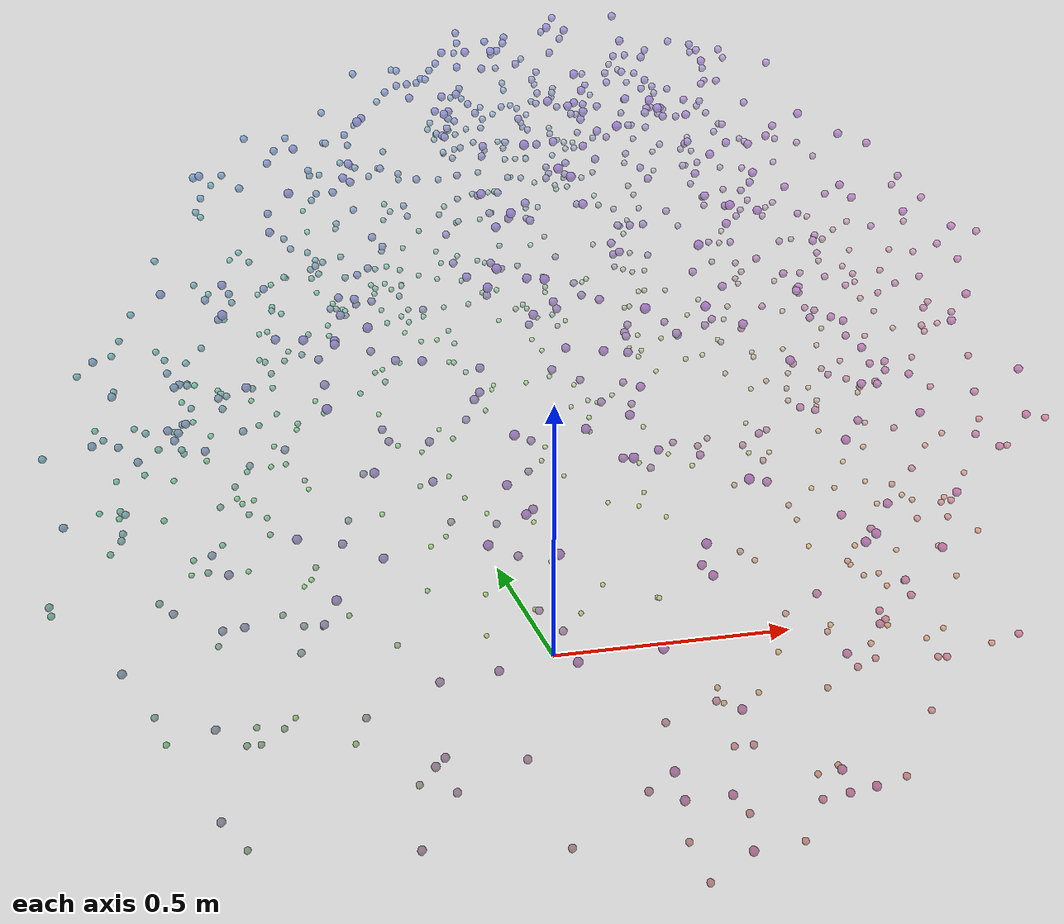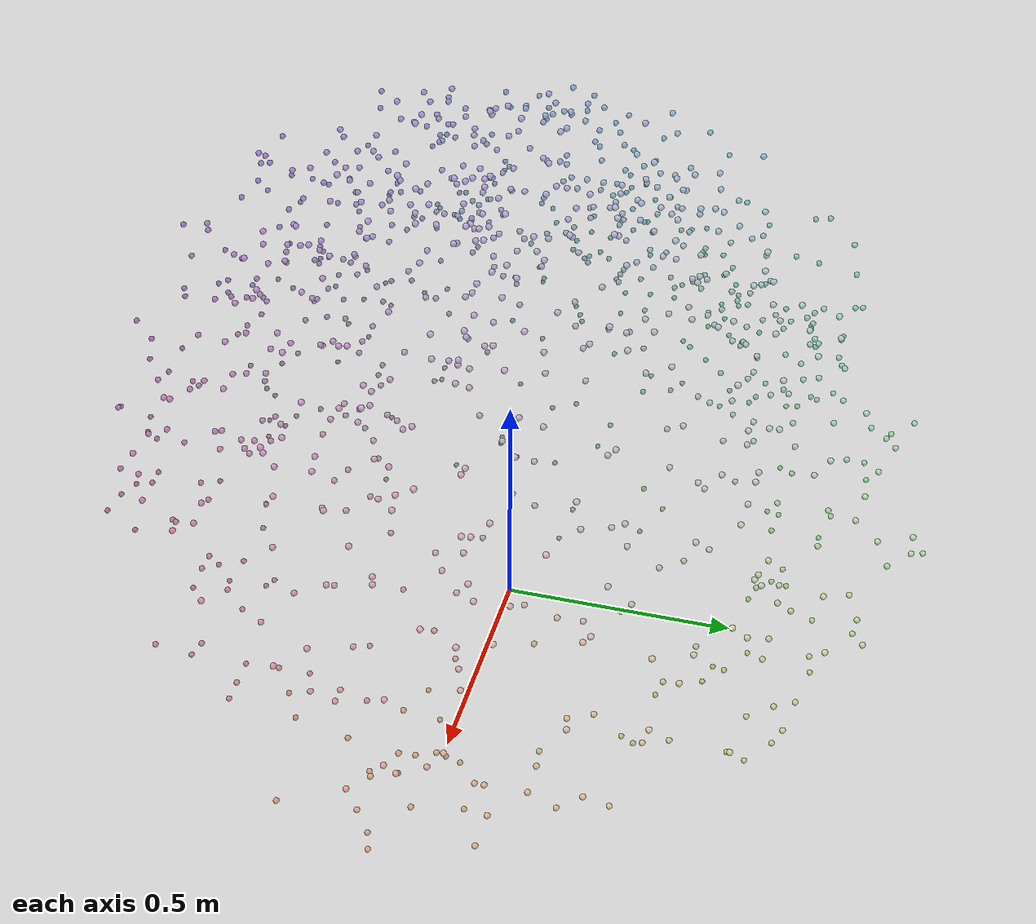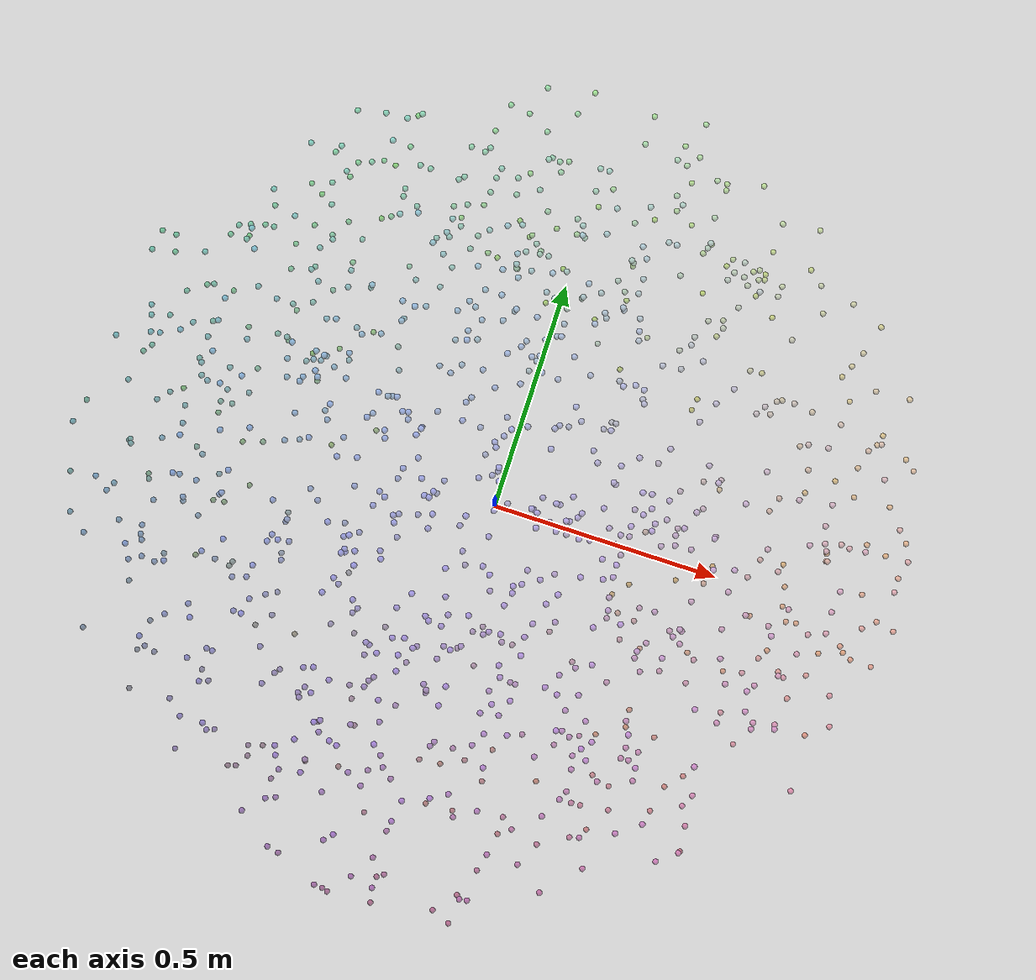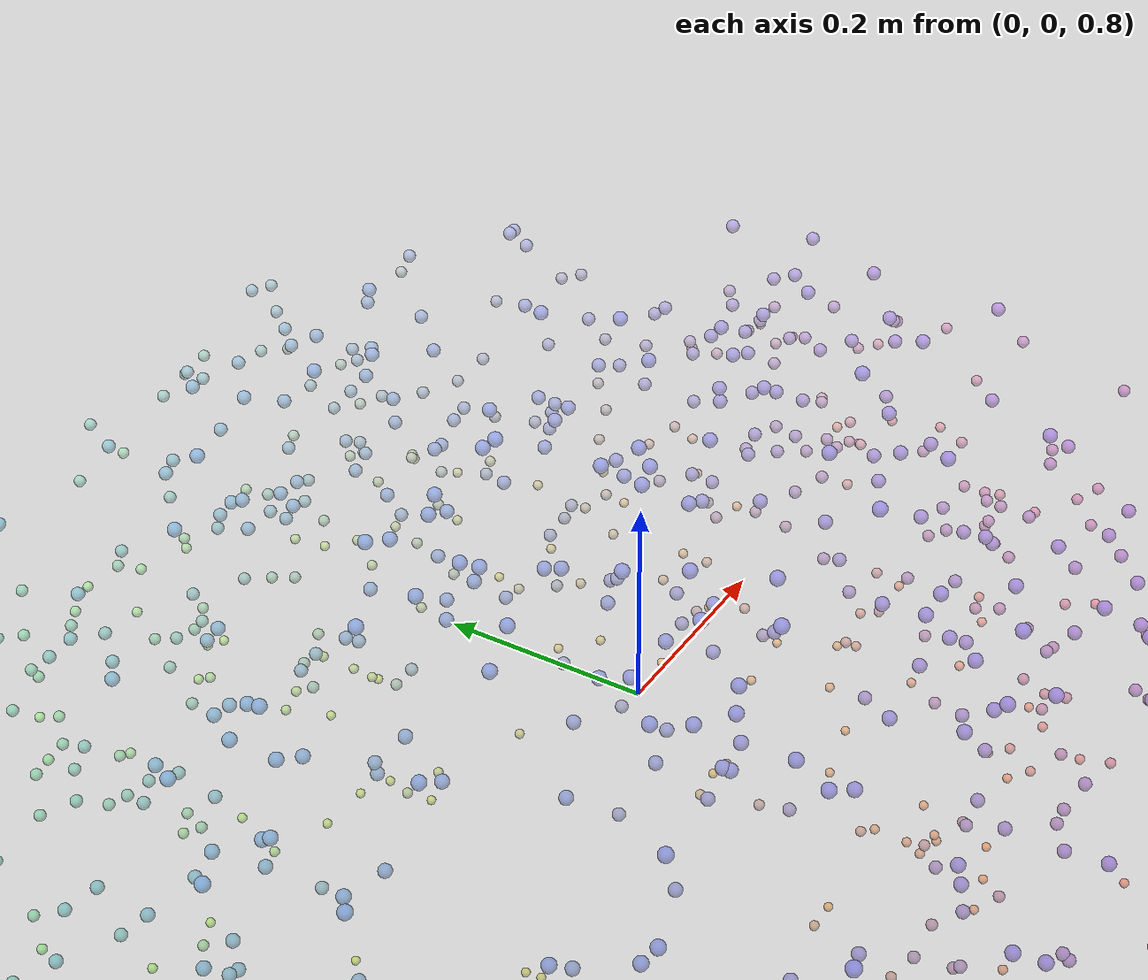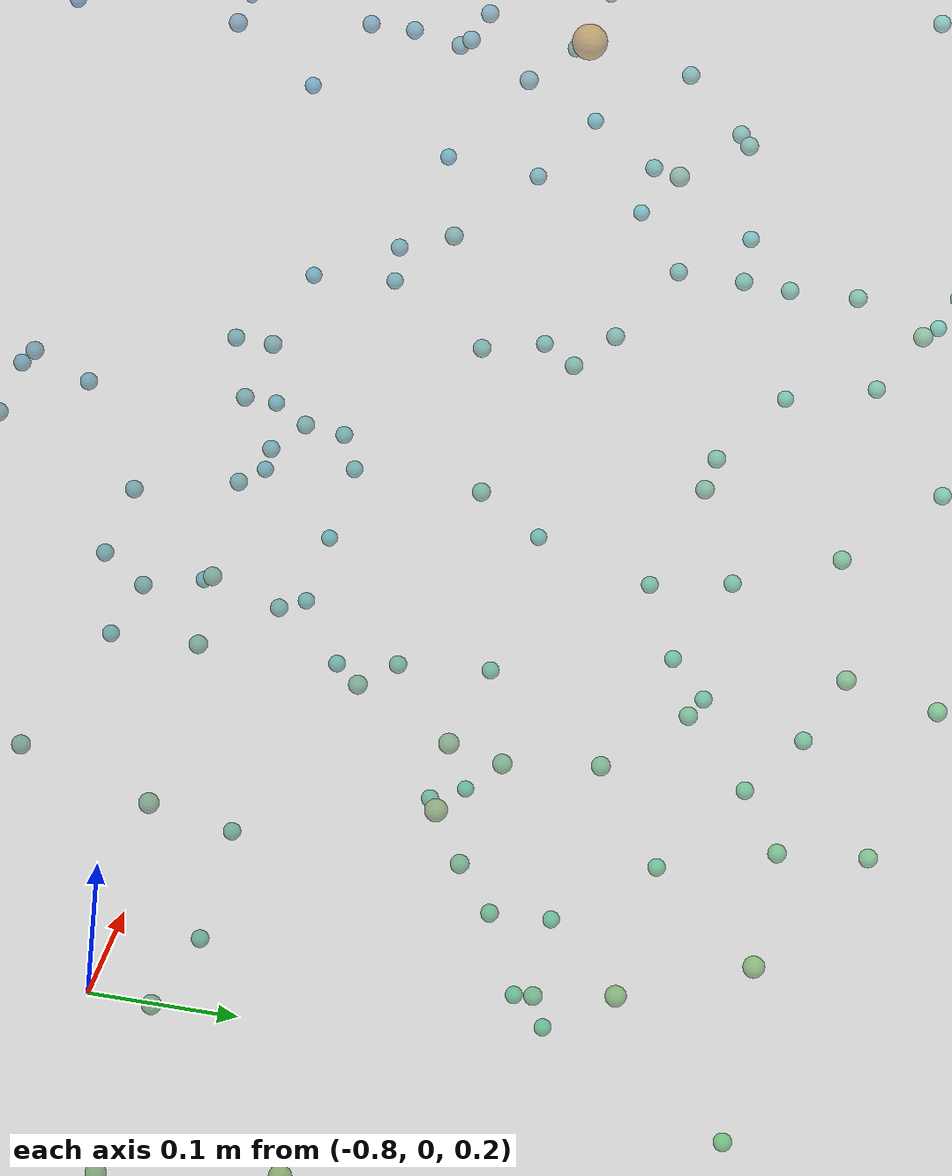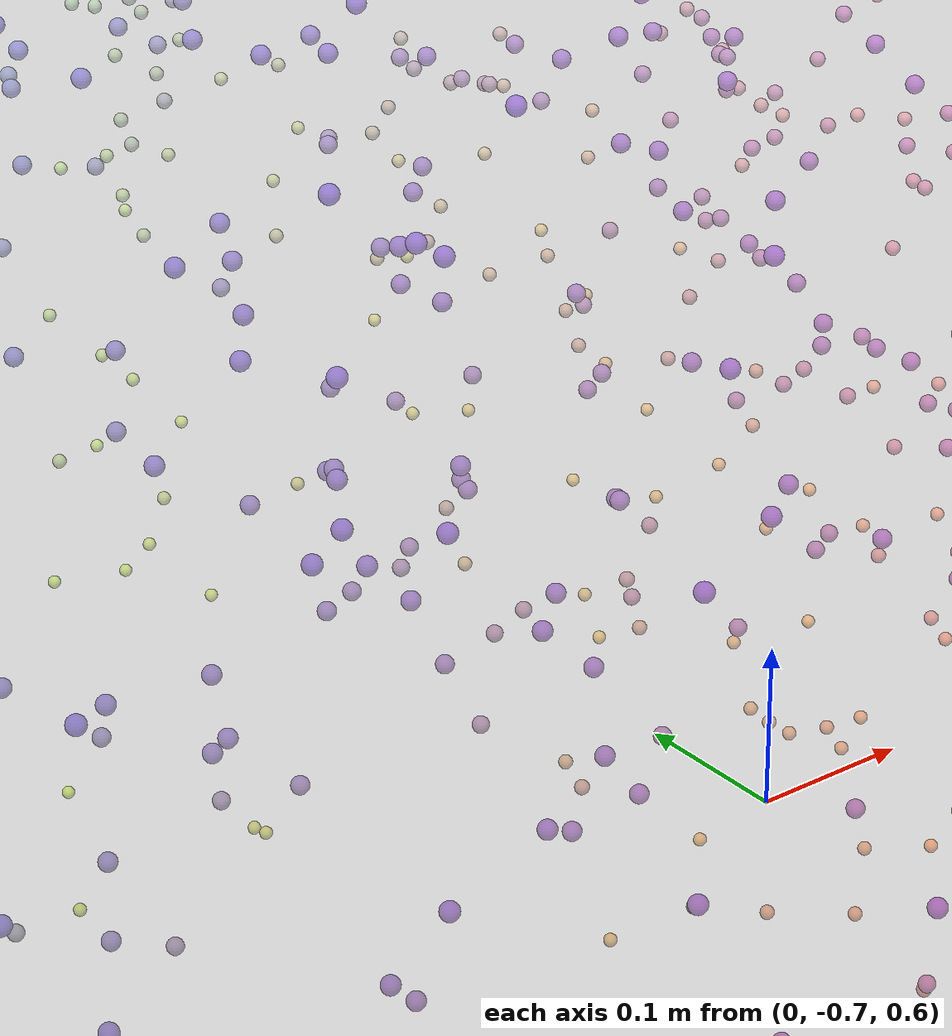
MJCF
<?xml version="1.0" encoding="utf-8"?>
    <mujoco>
        <worldbody>
            <body name="object_0" pos="0.1978690417680645 0.4178614118999207 0.3379582306827771">
                          <geom type="sphere" size="0.006" rgba="0.6081877171229002 0.7314918072975224 0.41219909092903123 0.5" />
                        </body>
<body name="object_1" pos="0.3746237778226631 -0.485757502511447 0.1520608607229263">
                          <geom type="sphere" size="0.006" rgba="0.7062880440093391 0.23126380116420983 0.2837521339899939 0.5" />
                        </body>
<body name="object_2" pos="0.3332759429604992 0.7981222432453949 0.3155770360295795">
                          <geom type="sphere" size="0.006" rgba="0.6833396568454906 0.9419977124317161 0.39673466372124244 0.5" />
                        </body>
<body name="object_3" pos="-0.7011590671538156 -0.0014272858184342 0.4627899479429965">
                          <geom type="sphere" size="0.006" rgba="0.10921974979165708 0.4993807415497299 0.49845235107473684 0.5" />
                        </body>
<body name="object_4" pos="-0.4953951307051785 0.3333291775753433 0.4918128162326142">
                          <geom type="sphere" size="0.006" rgba="0.22342042060602524 0.6846962053509621 0.518505884453122 0.5" />
                        </body>
<body name="object_5" pos="0.1708443736168611 -0.4550224971739339 0.9335109798021656">
                          <geom type="sphere" size="0.006" rgba="0.5931888048515387 0.24827817546877617 0.8237000085460197 0.5" />
                        </body>
<body name="object_6" pos="0.1668182611691006 0.3715111813322796 -0.0770249556280232">
                          <geom type="sphere" size="0.006" rgba="0.5909542794519768 0.705833110859352 0.12546384839171046 0.5" />
                        </body>
<body name="object_7" pos="0.3039003301604638 -0.6572648427557712 0.3046385380130278">
                          <geom type="sphere" size="0.006" rgba="0.6670359510297508 0.13632026525611876 0.3891766397211546 0.5" />
                        </body>
<body name="object_8" pos="-0.644979659703001 0.0480468216625543 0.5207642694681346">
                          <geom type="sphere" size="0.006" rgba="0.14039978127612587 0.5267687629221705 0.5385100731507274 0.5" />
                        </body>
<body name="object_9" pos="-0.0671917080045341 -0.5489868930602859 0.9975680898820852">
                          <geom type="sphere" size="0.006" rgba="0.46107682901959945 0.19626108988976299 0.8679606716304498 0.5" />
                        </body>
<body name="object_10" pos="0.3006060774119706 0.0442362234323088 1.0263981325192135">
                          <geom type="sphere" size="0.006" rgba="0.6652076137603387 0.524659280789282 0.887880970911508 0.5" />
                        </body>
<body name="object_11" pos="-0.3289912712440853 0.5025401598911468 0.617074472339666">
                          <geom type="sphere" size="0.006" rgba="0.3157759261651849 0.7783685167089334 0.6050562135490629 0.5" />
                        </body>
<body name="object_12" pos="0.2391559475625124 -0.0787340278861322 1.0726995962292396">
                          <geom type="sphere" size="0.006" rgba="0.631102288154897 0.45658504877654604 0.9198732584659827 0.5" />
                        </body>
<body name="object_13" pos="0.4784030246780561 0.3203343049119039 0.6238852602693851">
                          <geom type="sphere" size="0.006" rgba="0.7638863764093135 0.6775024656685397 0.6097621703042256 0.5" />
                        </body>
<body name="object_14" pos="-0.2507709033147361 -0.4523947042560248 0.7946080851913992">
                          <geom type="sphere" size="0.006" rgba="0.3591888713248348 0.2497328767713858 0.7277241799120261 0.5" />
                        </body>
<body name="object_15" pos="-0.1499025972977454 0.0996088928029196 0.964051423800016">
                          <geom type="sphere" size="0.006" rgba="0.41517160770645894 0.5553126453346483 0.8448021204045049 0.5" />
                        </body>
<body name="object_16" pos="0.6754242389583772 -0.1237183265820007 0.6414142752555054">
                          <geom type="sphere" size="0.006" rgba="0.873234764780035 0.4316825089059656 0.621873953454209 0.5" />
                        </body>
<body name="object_17" pos="-0.0004792826160648 0.0210901025039696 1.1844579980288903">
                          <geom type="sphere" size="0.006" rgba="0.4981027717698658 0.5118459833504541 0.9970934290721387 0.5" />
                        </body>
<body name="object_18" pos="0.6145366775482346 0.4741565995620239 0.2449270648585858">
                          <geom type="sphere" size="0.006" rgba="0.8394416692682517 0.7626558622215595 0.34791862180141986 0.5" />
                        </body>
<body name="object_19" pos="-0.0208431452417804 0.3217570614535009 1.0871356531883825">
                          <geom type="sphere" size="0.006" rgba="0.48680066114559284 0.6782900794033404 0.9298479428146693 0.5" />
                        </body>
<body name="object_20" pos="-0.5672627810862555 0.3877011655213913 0.2374688735416264">
                          <geom type="sphere" size="0.006" rgba="0.18353328574155303 0.7147956097414442 0.342765337604126 0.5" />
                        </body>
<body name="object_21" pos="0.1858897845144596 0.7946758220266282 0.4583298611380493">
                          <geom type="sphere" size="0.006" rgba="0.6015391311858741 0.9400898324758366 0.4953706260460118 0.5" />
                        </body>
<body name="object_22" pos="0.1047417717627655 0.3796818992245139 0.8845013613253223">
                          <geom type="sphere" size="0.006" rgba="0.5565013191599089 0.7103562808093443 0.7898365044230011 0.5" />
                        </body>
<body name="object_23" pos="0.8607788775276187 -0.0879485497242552 0.2115432732839686">
                          <geom type="sphere" size="0.006" rgba="0.9761081080320291 0.45148404677997017 0.32485188105208723 0.5" />
                        </body>
<body name="object_24" pos="-0.5460801476757517 0.3946453806505968 0.7581489516318233">
                          <geom type="sphere" size="0.006" rgba="0.19528982086061275 0.7186398086983751 0.7025325122764222 0.5" />
                        </body>
<body name="object_25" pos="-0.6672384884681956 0.1678453373290931 0.4094235456132452">
                          <geom type="sphere" size="0.006" rgba="0.12804594891657678 0.593087176219927 0.4615784997474084 0.5" />
                        </body>
<body name="object_26" pos="0.0098784756287367 -0.8884026625598427 0.1341793903324237">
                          <geom type="sphere" size="0.006" rgba="0.5038514124700044 0.008366313763293519 0.27139681956165307 0.5" />
                        </body>
<body name="object_27" pos="0.0136234069614049 -0.0518499436742813 1.021701962177348">
                          <geom type="sphere" size="0.006" rgba="0.505929880046616 0.47146761888163796 0.8846361224781478 0.5" />
                        </body>
<body name="object_28" pos="-0.5663669665297106 -0.033224172700422 -0.0589312468687229">
                          <geom type="sphere" size="0.006" rgba="0.1840304701609823 0.4817785277485896 0.13796581025580393 0.5" />
                        </body>
<body name="object_29" pos="0.2154727615200186 0.252013204791474 1.0881526465529014">
                          <geom type="sphere" size="0.006" rgba="0.617957925834878 0.639681070891362 0.9305506407760653 0.5" />
                        </body>
<body name="object_30" pos="0.8047956319489238 0.3172027143535856 0.4150685211470656">
                          <geom type="sphere" size="0.006" rgba="0.9450369479939902 0.6757688705920866 0.46547893109547506 0.5" />
                        </body>
<body name="object_31" pos="-0.0092039243642307 -0.2683270478422206 0.9500095669722438">
                          <geom type="sphere" size="0.006" rgba="0.4932605241075584 0.3516295893047756 0.8350998111158338 0.5" />
                        </body>
<body name="object_32" pos="-0.5096981665354402 0.2411396507341018 0.561725774473552">
                          <geom type="sphere" size="0.006" rgba="0.21548211851728402 0.6336616569780915 0.5668126826536233 0.5" />
                        </body>
<body name="object_33" pos="0.0119875211064763 0.0317812786576201 1.035245498161934">
                          <geom type="sphere" size="0.006" rgba="0.5050219499922393 0.5177644359694372 0.8939941138461275 0.5" />
                        </body>
<body name="object_34" pos="0.138689144463049 -0.0550667986649816 1.0646261524568192">
                          <geom type="sphere" size="0.006" rgba="0.5753423891825241 0.4696868228708924 0.9142948617150778 0.5" />
                        </body>
<body name="object_35" pos="0.3550374300827666 0.5534315034786486 0.6317234595481976">
                          <geom type="sphere" size="0.006" rgba="0.6954174605178632 0.806541095797547 0.615178023392748 0.5" />
                        </body>
<body name="object_36" pos="-0.7702972425982649 -0.3310170451286399 0.5559559414372433">
                          <geom type="sphere" size="0.006" rgba="0.07084749588306946 0.3169254769328957 0.5628259802289454 0.5" />
                        </body>
<body name="object_37" pos="-0.5004451229873752 0.5551954468613746 0.2678647315708792">
                          <geom type="sphere" size="0.006" rgba="0.22061763350840277 0.8075175847434958 0.3637675468782634 0.5" />
                        </body>
<body name="object_38" pos="-0.5950468016186639 -0.2089785427974347 0.5904205392562001">
                          <geom type="sphere" size="0.006" rgba="0.16811292667628386 0.38448390861136655 0.5866395108503246 0.5" />
                        </body>
<body name="object_39" pos="-0.1382092670078584 0.602600411776288 0.0323131953933021">
                          <geom type="sphere" size="0.006" rgba="0.4216615018356588 0.8337601641118726 0.2010117315008869 0.5" />
                        </body>
<body name="object_40" pos="-0.7473269496767223 -0.2363429533297704 0.6068212702347043">
                          <geom type="sphere" size="0.006" rgba="0.08359619667932153 0.36933543805448293 0.5979716990691233 0.5" />
                        </body>
<body name="object_41" pos="0.7056193527496205 0.1161472782585217 0.1243331442031739">
                          <geom type="sphere" size="0.006" rgba="0.8899933003611081 0.5644680132106176 0.26459349387260184 0.5" />
                        </body>
<body name="object_42" pos="0.1868123987334449 0.1941470541990135 0.8112921361713729">
                          <geom type="sphere" size="0.006" rgba="0.6020511896375613 0.6076473577056076 0.7392521298677259 0.5" />
                        </body>
<body name="object_43" pos="0.3571465267741021 0.2780974730542215 0.9822990237602006">
                          <geom type="sphere" size="0.006" rgba="0.6965880264640633 0.6541208765399857 0.857410414361718 0.5" />
                        </body>
<body name="object_44" pos="0.7884383859561765 -0.0653135763447187 0.1778506306311933">
                          <geom type="sphere" size="0.006" rgba="0.9359585424323156 0.46401438166113174 0.3015717377078426 0.5" />
                        </body>
<body name="object_45" pos="0.4177216075476818 0.4037249223241335 0.4953556022601721">
                          <geom type="sphere" size="0.006" rgba="0.7302076926620035 0.7236660879799638 0.5209537947405253 0.5" />
                        </body>
<body name="object_46" pos="0.3459400108123301 -0.1341997507681556 0.6898357333114847">
                          <geom type="sphere" size="0.006" rgba="0.6903683182760557 0.42588017139569645 0.6553310644353114 0.5" />
                        </body>
<body name="object_47" pos="0.2536249468232783 0.5884260894347342 0.7399617742343466">
                          <geom type="sphere" size="0.006" rgba="0.6391327013075174 0.8259135012209955 0.689965967668928 0.5" />
                        </body>
<body name="object_48" pos="-0.6591054062779461 -0.0203373473112002 0.508573146583203">
                          <geom type="sphere" size="0.006" rgba="0.1325598761768415 0.4889124543043853 0.5300865401196925 0.5" />
                        </body>
<body name="object_49" pos="0.0938067850776182 -0.0346274759160016 1.1187661778813982">
                          <geom type="sphere" size="0.006" rgba="0.5504323119454122 0.48100168304300134 0.951703252785329 0.5" />
                        </body>
<body name="object_50" pos="0.3733808432803466 -0.490164374798758 0.618612932310716">
                          <geom type="sphere" size="0.006" rgba="0.7055982051534115 0.22882423189180062 0.6061192221419041 0.5" />
                        </body>
<body name="object_51" pos="0.1972314467146834 0.2535785067243625 1.1122745192462675">
                          <geom type="sphere" size="0.006" rgba="0.6078338466436474 0.6405475953215146 0.9472178004233637 0.5" />
                        </body>
<body name="object_52" pos="-0.0529881913177586 0.2364839048883652 1.1106032579612033">
                          <geom type="sphere" size="0.006" rgba="0.46895989716821906 0.6310843155520398 0.9460630319273764 0.5" />
                        </body>
<body name="object_53" pos="0.757292700376643 0.0024363674554252 0.0805805950285789">
                          <geom type="sphere" size="0.006" rgba="0.9186724317194989 0.501519594049107 0.23436239484728444 0.5" />
                        </body>
<body name="object_54" pos="0.6750789121490678 0.4422191602358731 0.5001499054427246">
                          <geom type="sphere" size="0.006" rgba="0.8730431055711669 0.7449758409865779 0.5242664486773455 0.5" />
                        </body>
<body name="object_55" pos="-0.0569935024029047 0.172228854460109 1.0378217364096745">
                          <geom type="sphere" size="0.006" rgba="0.4667369166953601 0.5955138164764865 0.8957741818661522 0.5" />
                        </body>
<body name="object_56" pos="0.2499692297020129 0.662069902600384 0.6439593135818045">
                          <geom type="sphere" size="0.006" rgba="0.6371037483492797 0.8666814590806476 0.6236324636922879 0.5" />
                        </body>
<body name="object_57" pos="-0.1194783044020537 -0.0693666078082705 1.1218234946352894">
                          <geom type="sphere" size="0.006" rgba="0.4320573395684566 0.46177069262864967 0.9538157250248279 0.5" />
                        </body>
<body name="object_58" pos="0.3152533391525224 0.6393102058414729 0.0941084903408059">
                          <geom type="sphere" size="0.006" rgba="0.6733369640499711 0.8540820794657075 0.24370957919432878 0.5" />
                        </body>
<body name="object_59" pos="0.7179935499169553 0.2417902562855046 0.2170623915294484">
                          <geom type="sphere" size="0.006" rgba="0.896861081186499 0.6340218211054321 0.32866535051522006 0.5" />
                        </body>
<body name="object_60" pos="-0.3478396409047803 0.5830441330431986 0.6237636461932499">
                          <geom type="sphere" size="0.006" rgba="0.30531492655485787 0.8229341420332918 0.609678140293452 0.5" />
                        </body>
<body name="object_61" pos="-0.1476070657734087 -0.6390369134176692 0.0073467579890046">
                          <geom type="sphere" size="0.006" rgba="0.4164456465126723 0.14641093578472028 0.1837610145548452 0.5" />
                        </body>
<body name="object_62" pos="-0.620370438437066 -0.614612126865462 0.1087703869498633">
                          <geom type="sphere" size="0.006" rgba="0.15405810073333806 0.1599320806859438 0.2538403088694982 0.5" />
                        </body>
<body name="object_63" pos="0.3936714436244866 0.1528510515080183 0.5764914622149535">
                          <geom type="sphere" size="0.006" rgba="0.7168596546110789 0.5847865955436634 0.5770151274644599 0.5" />
                        </body>
<body name="object_64" pos="-0.7788626993016479 0.1329295429672896 0.5397533991024358">
                          <geom type="sphere" size="0.006" rgba="0.06609359722502191 0.5737583884780908 0.5516307316999779 0.5" />
                        </body>
<body name="object_65" pos="0.3627797253146719 -0.6207938730468427 0.3520158261197869">
                          <geom type="sphere" size="0.006" rgba="0.6997144978140328 0.1565099715230909 0.42191227490873995 0.5" />
                        </body>
<body name="object_66" pos="-0.5756835250591282 -0.5207308345303787 0.3388066451179173">
                          <geom type="sphere" size="0.006" rgba="0.1788597038347539 0.21190316155756234 0.4127853082189286 0.5" />
                        </body>
<body name="object_67" pos="0.3316696372148039 0.5772125266491915 0.7948799013937079">
                          <geom type="sphere" size="0.006" rgba="0.6824481439941259 0.8197058642798004 0.7279119930265463 0.5" />
                        </body>
<body name="object_68" pos="-0.0241581489290342 0.0703068073348578 1.0829982031097418">
                          <geom type="sphere" size="0.006" rgba="0.4849608069351297 0.5390915110096938 0.9269891456611467 0.5" />
                        </body>
<body name="object_69" pos="0.322286957286064 -0.5288285757141639 0.5734344883836935">
                          <geom type="sphere" size="0.006" rgba="0.6772406797494569 0.20742039026764622 0.5749028921695097 0.5" />
                        </body>
<body name="object_70" pos="-0.438325171693989 0.6018831349023903 0.3377513476003999">
                          <geom type="sphere" size="0.006" rgba="0.25509471550392254 0.8333630918784865 0.4120561437621118 0.5" />
                        </body>
<body name="object_71" pos="-0.6867391269201789 0.2397037511426917 0.4349893051728718">
                          <geom type="sphere" size="0.006" rgba="0.11722293478221772 0.6328667674752676 0.4792433221059946 0.5" />
                        </body>
<body name="object_72" pos="-0.2550096106957639 0.5861139691927597 0.6423846533046436">
                          <geom type="sphere" size="0.006" rgba="0.35683635399524916 0.8246335509232123 0.6225444422702646 0.5" />
                        </body>
<body name="object_73" pos="0.0341577582080185 0.3037113043623174 1.0519899634209262">
                          <geom type="sphere" size="0.006" rgba="0.5173266132525173 0.6683002563209306 0.9055638074278791 0.5" />
                        </body>
<body name="object_74" pos="-0.0118511233364241 0.5754850726101736 0.6385224077413476">
                          <geom type="sphere" size="0.006" rgba="0.49179130698612633 0.8187495752116506 0.6198757994074645 0.5" />
                        </body>
<body name="object_75" pos="0.4519881826645684 0.4302850600336775 0.2366316201192763">
                          <geom type="sphere" size="0.006" rgba="0.7492259226414646 0.738369326831185 0.342186832086211 0.5" />
                        </body>
<body name="object_76" pos="0.0262568659513277 -0.160520870307387 1.0320994472932183">
                          <geom type="sphere" size="0.006" rgba="0.5129415533080047 0.4113092489234912 0.8918203302119146 0.5" />
                        </body>
<body name="object_77" pos="-0.3917521506208041 0.1350715851129236 0.9726466341570208">
                          <geom type="sphere" size="0.006" rgba="0.28094312383147746 0.5749441864449938 0.8507410350585778 0.5" />
                        </body>
<body name="object_78" pos="-0.3601925605371306 0.2205842385413169 0.7615146885557498">
                          <geom type="sphere" size="0.006" rgba="0.29845895493573726 0.6222825316715531 0.7048580893721557 0.5" />
                        </body>
<body name="object_79" pos="0.4416920575266714 -0.1790445483521157 0.7450007141109403">
                          <geom type="sphere" size="0.006" rgba="0.7435114888206961 0.4010548569593676 0.6934476548680908 0.5" />
                        </body>
<body name="object_80" pos="0.219071519890222 -0.6236731171965723 0.3464026366584272">
                          <geom type="sphere" size="0.006" rgba="0.6199552662195408 0.15491607111084862 0.4180338063473523 0.5" />
                        </body>
<body name="object_81" pos="-0.1392081842608493 -0.3697254162974421 0.8648441403159255">
                          <geom type="sphere" size="0.006" rgba="0.4211070945748505 0.29549718341045256 0.7762542239362977 0.5" />
                        </body>
<body name="object_82" pos="-0.2514708602613179 -0.3023931550559019 1.0160429719763815">
                          <geom type="sphere" size="0.006" rgba="0.3588003894838453 0.33277117386387695 0.880726007607674 0.5" />
                        </body>
<body name="object_83" pos="0.1219315409187689 0.5244111036275418 0.6531741024643712">
                          <geom type="sphere" size="0.006" rgba="0.5660417818991107 0.7904758978217309 0.6299994800253161 0.5" />
                        </body>
<body name="object_84" pos="0.3736389443253424 0.5182540134658326 0.9089245184240956">
                          <geom type="sphere" size="0.006" rgba="0.7057414533483339 0.7870674378104869 0.8067118384250851 0.5" />
                        </body>
<body name="object_85" pos="-0.1457274661904172 0.5905596914681392 0.586623648325271">
                          <geom type="sphere" size="0.006" rgba="0.4174888396831801 0.8270946268858422 0.5840160251817937 0.5" />
                        </body>
<body name="object_86" pos="-0.8303833005741177 0.2684376690380941 0.4387490800745916">
                          <geom type="sphere" size="0.006" rgba="0.03749924134505296 0.6487733739306877 0.48184116222070933 0.5" />
                        </body>
<body name="object_87" pos="0.596127787205966 -0.581023729178435 0.2252218400911127">
                          <geom type="sphere" size="0.006" rgba="0.8292245842808637 0.1785260442874464 0.3343031728161635 0.5" />
                        </body>
<body name="object_88" pos="0.1840620826169797 -0.0588003118373156 1.1431021410016209">
                          <geom type="sphere" size="0.006" rgba="0.6005247416560887 0.4676200137102124 0.9685183395595441 0.5" />
                        </body>
<body name="object_89" pos="0.1563310519320494 -0.5719181110588746 0.089738233211279">
                          <geom type="sphere" size="0.006" rgba="0.585133792390383 0.1835667590444258 0.24068992254480168 0.5" />
                        </body>
<body name="object_90" pos="-0.5286377331673727 0.1813651805853705 0.4518932670437471">
                          <geom type="sphere" size="0.006" rgba="0.20497050384062748 0.6005715306612326 0.4909232208748496 0.5" />
                        </body>
<body name="object_91" pos="0.3172115439575604 0.6247607897703977 0.3716127404678174">
                          <geom type="sphere" size="0.006" rgba="0.6744237837628272 0.846027771089063 0.43545288612848515 0.5" />
                        </body>
<body name="object_92" pos="0.4849331731384178 -0.2459364490340727 0.5589128879522021">
                          <geom type="sphere" size="0.006" rgba="0.7675106623146177 0.36402464259472017 0.564869101020595 0.5" />
                        </body>
<body name="object_93" pos="0.4218659334407288 -0.1713851308281399 0.8169598446045161">
                          <geom type="sphere" size="0.006" rgba="0.7325078274923723 0.40529497975345147 0.7431682686555537 0.5" />
                        </body>
<body name="object_94" pos="-0.2549965780138162 0.1042239745307753 0.8619357037254072">
                          <geom type="sphere" size="0.006" rgba="0.3568435872405234 0.5578674757991826 0.7742446213820341 0.5" />
                        </body>
<body name="object_95" pos="0.1436257702154498 -0.423530784436449 0.8849859094927766">
                          <geom type="sphere" size="0.006" rgba="0.5780822569271539 0.2657114500728795 0.7901713060267749 0.5" />
                        </body>
<body name="object_96" pos="0.5227871844856765 -0.1838894767397054 0.8318222269174405">
                          <geom type="sphere" size="0.006" rgba="0.7885199487983585 0.398372787307515 0.7534375251887259 0.5" />
                        </body>
<body name="object_97" pos="-0.4726076081809143 0.2570061502831096 0.5596116359523914">
                          <geom type="sphere" size="0.006" rgba="0.23606768233411768 0.6424450802853443 0.5653519053459651 0.5" />
                        </body>
<body name="object_98" pos="-0.1122161479006107 0.3907385602749014 1.0601174121882668">
                          <geom type="sphere" size="0.006" rgba="0.4360878959348329 0.7164770596282893 0.9111795192696781 0.5" />
                        </body>
<body name="object_99" pos="0.577949022363044 -0.2791072887380891 0.4134662860206956">
                          <geom type="sphere" size="0.006" rgba="0.8191352208313237 0.3456618319648467 0.4643718566579641 0.5" />
                        </body>
<body name="object_100" pos="-0.5395239480796437 0.0420192339974667 0.5522165754057022">
                          <geom type="sphere" size="0.006" rgba="0.19892856535972633 0.5234319932824328 0.5602422417514382 0.5" />
                        </body>
<body name="object_101" pos="0.4167529189195773 -0.1589516477110716 0.6881946044328934">
                          <geom type="sphere" size="0.006" rgba="0.7296700625357087 0.41217794376599076 0.6541971161150885 0.5" />
                        </body>
<body name="object_102" pos="0.2722568933839563 0.0391038023938744 0.8982774384561">
                          <geom type="sphere" size="0.006" rgba="0.6494735843239056 0.5218180601134563 0.7993551715584641 0.5" />
                        </body>
<body name="object_103" pos="-0.3509992891321792 -0.4402005353754823 0.6798341828647584">
                          <geom type="sphere" size="0.006" rgba="0.30356129589763886 0.25648336050770754 0.6484204302513434 0.5" />
                        </body>
<body name="object_104" pos="-0.2198211453342173 -0.8228595375987958 0.5154494185040304">
                          <geom type="sphere" size="0.006" rgba="0.37636624061471463 0.044649868912610746 0.5348377434503603 0.5" />
                        </body>
<body name="object_105" pos="-0.3606404514458735 0.1607343578276781 0.658081551779862">
                          <geom type="sphere" size="0.006" rgba="0.29821037181124566 0.589150659353229 0.6333903129943006 0.5" />
                        </body>
<body name="object_106" pos="-0.4654732985089738 -0.6949936587082015 0.4341129994196462">
                          <geom type="sphere" size="0.006" rgba="0.24002728266250864 0.11543423678033249 0.4786378331344491 0.5" />
                        </body>
<body name="object_107" pos="0.2666483740188687 0.6484685815558999 0.3132474314669238">
                          <geom type="sphere" size="0.006" rgba="0.6463608101185565 0.8591519999266265 0.3951250087970817 0.5" />
                        </body>
<body name="object_108" pos="0.5756117832782881 -0.1888640518041244 0.0425232141421371">
                          <geom type="sphere" size="0.006" rgba="0.8178380339873146 0.3956189474684543 0.20806640816931748 0.5" />
                        </body>
<body name="object_109" pos="0.3833691849286902 0.1641545107618813 0.9245473673641672">
                          <geom type="sphere" size="0.006" rgba="0.7111418166154165 0.5910439976351771 0.8175065441570912 0.5" />
                        </body>
<body name="object_110" pos="0.1380987064087598 0.6931464736408102 0.0412831466046562">
                          <geom type="sphere" size="0.006" rgba="0.5750146912241845 0.8838849183277785 0.20720957570513196 0.5" />
                        </body>
<body name="object_111" pos="0.4034846069581129 -0.6690740155414915 0.4971042747629332">
                          <geom type="sphere" size="0.006" rgba="0.7223060406729575 0.12978290878596044 0.522162051004243 0.5" />
                        </body>
<body name="object_112" pos="0.7567118959831657 -0.3884569034879758 0.5199055514278976">
                          <geom type="sphere" size="0.006" rgba="0.9183500805218505 0.28512775185053874 0.537916736520086 0.5" />
                        </body>
<body name="object_113" pos="0.2607350810438725 -0.0182113277050713 0.93842459735554">
                          <geom type="sphere" size="0.006" rgba="0.643078884062311 0.4900893824669249 0.8270951034977637 0.5" />
                        </body>
<body name="object_114" pos="0.0262186840226334 0.1188243294382386 1.062836704671403">
                          <geom type="sphere" size="0.006" rgba="0.5129203620247064 0.5659499830461194 0.9130584315133613 0.5" />
                        </body>
<body name="object_115" pos="0.0146275349389405 0.6777922213019617 0.0783381411023555">
                          <geom type="sphere" size="0.006" rgba="0.5064871793022446 0.8753850663319478 0.23281295720348344 0.5" />
                        </body>
<body name="object_116" pos="0.3306640924588892 -0.2946008178627615 0.6159853502941341">
                          <geom type="sphere" size="0.006" rgba="0.6818900584148874 0.3370848787178554 0.6043036778218819 0.5" />
                        </body>
<body name="object_117" pos="0.2879641820060412 0.5881401838923971 -0.1014486335619425">
                          <geom type="sphere" size="0.006" rgba="0.6581912582189359 0.8257552287932001 0.10858815451530654 0.5" />
                        </body>
<body name="object_118" pos="-0.4427715916518188 -0.5429832329035414 0.7236582113739392">
                          <geom type="sphere" size="0.006" rgba="0.2526269159921587 0.19958461366932734 0.6787009183724483 0.5" />
                        </body>
<body name="object_119" pos="-0.1683285544198809 0.0335235601292834 1.156609574764669">
                          <geom type="sphere" size="0.006" rgba="0.404945050516395 0.5187289332511933 0.9778513858704941 0.5" />
                        </body>
<body name="object_120" pos="-0.0763105204007961 0.5846200201246918 0.5224786192328623">
                          <geom type="sphere" size="0.006" rgba="0.45601581341765773 0.8238065262210224 0.5396946139027348 0.5" />
                        </body>
<body name="object_121" pos="-0.3112107470459034 -0.6423640685890384 0.1209320421071883">
                          <geom type="sphere" size="0.006" rgba="0.3256442627936025 0.14456907947679395 0.26224348098881184 0.5" />
                        </body>
<body name="object_122" pos="0.1797314973441204 0.1611582613499859 1.0528764401748">
                          <geom type="sphere" size="0.006" rgba="0.5981212313436642 0.589385325107094 0.9061763241162912 0.5" />
                        </body>
<body name="object_123" pos="-0.0745419223870388 0.4980936686225285 0.6759326358038956">
                          <geom type="sphere" size="0.006" rgba="0.45699739980766374 0.7759070150447733 0.6457246317716205 0.5" />
                        </body>
<body name="object_124" pos="0.0359716399520845 0.6844243763948439 0.3986128512642941">
                          <geom type="sphere" size="0.006" rgba="0.5183333324839118 0.8790565141796729 0.4541087824952454 0.5" />
                        </body>
<body name="object_125" pos="0.3342568090931234 0.4544403288934027 0.6472539178128689">
                          <geom type="sphere" size="0.006" rgba="0.6838840455865796 0.7517412713385502 0.625908891206513 0.5" />
                        </body>
<body name="object_126" pos="-0.7500908370843553 0.1486389558561228 0.4660358725476441">
                          <geom type="sphere" size="0.006" rgba="0.08206221652004389 0.5824548512917593 0.5006951430949282 0.5" />
                        </body>
<body name="object_127" pos="-0.1676407605282893 0.0587011269138271 1.0101192853533">
                          <geom type="sphere" size="0.006" rgba="0.4053267817621976 0.5326668044389881 0.8766329990795836 0.5" />
                        </body>
<body name="object_128" pos="-0.0084924515664247 -0.4205725537162468 0.702536953406617">
                          <geom type="sphere" size="0.006" rgba="0.4936553973403413 0.2673490761022251 0.6641070523418915 0.5" />
                        </body>
<body name="object_129" pos="-0.2638970333231689 0.6588544736190594 0.5561532060384643">
                          <geom type="sphere" size="0.006" rgba="0.35190376161109344 0.8649014524843502 0.5629622814458163 0.5" />
                        </body>
<body name="object_130" pos="0.3022702424045032 0.4630295004447933 0.6105979148910982">
                          <geom type="sphere" size="0.006" rgba="0.6661312389678125 0.7564960900911964 0.6005811954469291 0.5" />
                        </body>
<body name="object_131" pos="-0.6099537869154987 0.4413938145267272 0.6711202390942504">
                          <geom type="sphere" size="0.006" rgba="0.1598394276846692 0.7445189436907462 0.6423994759984599 0.5" />
                        </body>
<body name="object_132" pos="0.2792687083640029 -0.1363868951926356 0.8051200373446455">
                          <geom type="sphere" size="0.006" rgba="0.6533651990945407 0.4246694055771258 0.734987479365186 0.5" />
                        </body>
<body name="object_133" pos="0.1478646933805007 -0.3016060923883719 1.0966826682525217">
                          <geom type="sphere" size="0.006" rgba="0.5804348940186406 0.33320687832136603 0.9364445129173269 0.5" />
                        </body>
<body name="object_134" pos="-0.3478002904518771 -0.1125627169223951 0.7742228224394694">
                          <geom type="sphere" size="0.006" rgba="0.3053367663786674 0.437858063985909 0.7136388544044431 0.5" />
                        </body>
<body name="object_135" pos="-0.1156406685829852 -0.380956694815753 1.0328421066475038">
                          <geom type="sphere" size="0.006" rgba="0.434187258894666 0.2892797393420066 0.8923334753635697 0.5" />
                        </body>
<body name="object_136" pos="-0.3476974070129861 0.2965201337868738 0.934191345012698">
                          <geom type="sphere" size="0.006" rgba="0.3053938675303066 0.6643193470445218 0.8241701111672614 0.5" />
                        </body>
<body name="object_137" pos="0.0322821459315853 -0.3176866014166015 0.8512581689893052">
                          <geom type="sphere" size="0.006" rgba="0.5162856330698223 0.3243049830195839 0.7668669116018506 0.5" />
                        </body>
<body name="object_138" pos="-0.1723965748323182 -0.1910912881400908 0.953497594231512">
                          <geom type="sphere" size="0.006" rgba="0.4026872658530323 0.3943859874520586 0.837509885487893 0.5" />
                        </body>
<body name="object_139" pos="0.5018088473283813 -0.2949926636676707 0.9212179715580158">
                          <geom type="sphere" size="0.006" rgba="0.7768767997738883 0.33686795956911325 0.815206077185245 0.5" />
                        </body>
<body name="object_140" pos="-0.4265766553248964 -0.0368133774410172 0.7720720280844418">
                          <geom type="sphere" size="0.006" rgba="0.2616152383592912 0.4797916052723577 0.7121527495178347 0.5" />
                        </body>
<body name="object_141" pos="-0.5624236196215768 0.5253385952540371 0.0377781755199838">
                          <geom type="sphere" size="0.006" rgba="0.18621906000784821 0.7909893413537639 0.20478779389034502 0.5" />
                        </body>
<body name="object_142" pos="-0.4238590915834038 0.2195261620878515 0.0169908379148822">
                          <geom type="sphere" size="0.006" rgba="0.26312350850427224 0.6216967986084085 0.1904246522341915 0.5" />
                        </body>
<body name="object_143" pos="0.6022300312604574 -0.2672036890522919 0.8063208011507724">
                          <geom type="sphere" size="0.006" rgba="0.8326113797345455 0.3522514615550089 0.7358171546689993 0.5" />
                        </body>
<body name="object_144" pos="0.3674097095714538 0.6194617758342995 0.3202188897476234">
                          <geom type="sphere" size="0.006" rgba="0.7022841770158906 0.8430943274288517 0.3999419817417592 0.5" />
                        </body>
<body name="object_145" pos="-0.0396599926225087 -0.2919718505427259 1.0515435141374887">
                          <geom type="sphere" size="0.006" rgba="0.4763571566589494 0.3385402301494351 0.9052553304876324 0.5" />
                        </body>
<body name="object_146" pos="-0.0002029458798913 -0.7215483461984666 0.4454775486786369">
                          <geom type="sphere" size="0.006" rgba="0.49825614092282006 0.10073401507746832 0.48649023992006646 0.5" />
                        </body>
<body name="object_147" pos="0.346707441904051 0.3592398202056514 -0.0525816098872062">
                          <geom type="sphere" size="0.006" rgba="0.6907942488204989 0.6990398948132782 0.14235313186298718 0.5" />
                        </body>
<body name="object_148" pos="-0.2377093023637979 -0.2095689710405832 0.9851201501317908">
                          <geom type="sphere" size="0.006" rgba="0.3664381668828982 0.3841570576146414 0.8593596893710929 0.5" />
                        </body>
<body name="object_149" pos="0.3732296550106813 -0.1352298352018686 0.8044170558373118">
                          <geom type="sphere" size="0.006" rgba="0.7055142944248696 0.4253099342368596 0.7345017498714286 0.5" />
                        </body>
<body name="object_150" pos="-0.5046391535507843 -0.5990815054295328 0.4837017432678864">
                          <geom type="sphere" size="0.006" rgba="0.21828991217868943 0.16852956760327653 0.5129014875751307 0.5" />
                        </body>
<body name="object_151" pos="0.2748787754015971 0.3337560840406061 0.8368988400976181">
                          <geom type="sphere" size="0.006" rgba="0.6509287503281068 0.6849325334827864 0.7569452429939388 0.5" />
                        </body>
<body name="object_152" pos="-0.7621622230295031 -0.1176919200360956 0.3427466639157486">
                          <geom type="sphere" size="0.006" rgba="0.07536249840428394 0.4350186246982856 0.4155076889872705 0.5" />
                        </body>
<body name="object_153" pos="0.271291908566123 -0.0036475189901781 1.1031381616656404">
                          <geom type="sphere" size="0.006" rgba="0.6489380098426614 0.4981516583655029 0.940904976691689 0.5" />
                        </body>
<body name="object_154" pos="0.1340520785375032 0.5117320875211514 0.0006366703205923">
                          <geom type="sphere" size="0.006" rgba="0.5727687795964732 0.7834570109375809 0.1791246372785671 0.5" />
                        </body>
<body name="object_155" pos="0.4284281342744508 -0.438718144924671 0.8731871233676913">
                          <geom type="sphere" size="0.006" rgba="0.7361499027275374 0.25730398655669134 0.7820188605474814 0.5" />
                        </body>
<body name="object_156" pos="0.6957005024667597 0.318810606518911 0.5288875001695202">
                          <geom type="sphere" size="0.006" rgba="0.8844882571763772 0.6766589722478958 0.5441228704933262 0.5" />
                        </body>
<body name="object_157" pos="0.0207043168946997 -0.8155750721416699 0.2855282993093883">
                          <geom type="sphere" size="0.006" rgba="0.5098598430824867 0.048682424642963934 0.37597230009875304 0.5" />
                        </body>
<body name="object_158" pos="-0.3769069427356812 -0.1883457358354761 0.726046133774338">
                          <geom type="sphere" size="0.006" rgba="0.28918233585337116 0.3959058783409814 0.6803508683733764 0.5" />
                        </body>
<body name="object_159" pos="0.3428239168692252 -0.5509443160202181 0.4098005521837356">
                          <geom type="sphere" size="0.006" rgba="0.6886388606035154 0.19517749395259262 0.46183899480839813 0.5" />
                        </body>
<body name="object_160" pos="0.3622485381107375 -0.2213861425584246 0.8581232616657299">
                          <geom type="sphere" size="0.006" rgba="0.6994196845631575 0.3776152731829202 0.7716103905632888 0.5" />
                        </body>
<body name="object_161" pos="-0.4154401537403882 0.1448222710149813 0.8715835412057634">
                          <geom type="sphere" size="0.006" rgba="0.2677960879942008 0.5803419997149781 0.7809108553672798 0.5" />
                        </body>
<body name="object_162" pos="0.3507971841444358 -0.1548551480319721 0.4108792760891427">
                          <geom type="sphere" size="0.006" rgba="0.693064089276367 0.4144456960605923 0.4625843458752629 0.5" />
                        </body>
<body name="object_163" pos="-0.2207278898371689 0.4003954055468516 0.6808276765695337">
                          <geom type="sphere" size="0.006" rgba="0.37586298998546663 0.7218229243273172 0.649106890975043 0.5" />
                        </body>
<body name="object_164" pos="-0.5801401023938552 -0.4934193600761947 0.759807239820282">
                          <geom type="sphere" size="0.006" rgba="0.17638626689557985 0.22702232760520644 0.703678316929718 0.5" />
                        </body>
<body name="object_165" pos="0.1498334859232407 0.4452841221983924 0.8786855972732024">
                          <geom type="sphere" size="0.006" rgba="0.5815275900126801 0.7466725516097548 0.7858180656740743 0.5" />
                        </body>
<body name="object_166" pos="0.3497685320829794 0.4996736318942919 0.6865586000366828">
                          <geom type="sphere" size="0.006" rgba="0.6924931789532053 0.7767816557418563 0.6530667085881959 0.5" />
                        </body>
<body name="object_167" pos="-0.247077217941916 -0.5132441416404145 0.6438874378584483">
                          <geom type="sphere" size="0.006" rgba="0.36123889697380746 0.2160476669426879 0.6235828007091865 0.5" />
                        </body>
<body name="object_168" pos="0.2788979331878358 -0.3384397561523729 0.9075801876756496">
                          <geom type="sphere" size="0.006" rgba="0.6531594158335358 0.31281639081673746 0.8057829646395401 0.5" />
                        </body>
<body name="object_169" pos="0.2660349783240348 -0.3741380444528352 0.7765075837310386">
                          <geom type="sphere" size="0.006" rgba="0.6460203704815933 0.2930544277877265 0.7152175245884136 0.5" />
                        </body>
<body name="object_170" pos="0.0525754474260411 -0.1972659840834737 0.8424831442838295">
                          <geom type="sphere" size="0.006" rgba="0.5275485816880491 0.39096778118061287 0.7608037530927946 0.5" />
                        </body>
<body name="object_171" pos="0.0080334360906359 0.2820972042283226 1.1315019780472344">
                          <geom type="sphere" size="0.006" rgba="0.5028274004076053 0.6563350594420704 0.9605031340092466 0.5" />
                        </body>
<body name="object_172" pos="0.8262016000337566 0.0563520776313253 0.6123566483494391">
                          <geom type="sphere" size="0.006" rgba="0.9569174356873673 0.5313664108547521 0.6017964033911811 0.5" />
                        </body>
<body name="object_173" pos="-0.2645496070893011 0.5410861409703394 0.47206994768076">
                          <geom type="sphere" size="0.006" rgba="0.351541577823524 0.7997069138497871 0.5048644252582942 0.5" />
                        </body>
<body name="object_174" pos="0.2312305637903738 -0.3125575130178842 0.9141910461818046">
                          <geom type="sphere" size="0.006" rgba="0.6267036352186209 0.3271443588029508 0.810350778902074 0.5" />
                        </body>
<body name="object_175" pos="0.1757419295602981 0.5566187868585153 0.8985106102846145">
                          <geom type="sphere" size="0.006" rgba="0.5959069885320449 0.808305521469326 0.7995162830998649 0.5" />
                        </body>
<body name="object_176" pos="-0.4056511157517635 -0.4035812831259002 0.1241663587157599">
                          <geom type="sphere" size="0.006" rgba="0.2732290842919136 0.2767551534579845 0.26447825239110834 0.5" />
                        </body>
<body name="object_177" pos="-0.033013747189705 -0.0026958333625563 1.0570619239605743">
                          <geom type="sphere" size="0.006" rgba="0.48004587733528903 0.49867849528356484 0.9090683104618564 0.5" />
                        </body>
<body name="object_178" pos="-0.2566438883977697 0.5588893644634045 0.1362925947325293">
                          <geom type="sphere" size="0.006" rgba="0.35592931647892223 0.8095624744723567 0.2728569514324933 0.5" />
                        </body>
<body name="object_179" pos="0.0434430834804381 -0.2815507467559189 0.6909449675465055">
                          <geom type="sphere" size="0.006" rgba="0.5224800448651781 0.3443091753163018 0.6560974968063115 0.5" />
                        </body>
<body name="object_180" pos="0.172751870555798 0.3580286225413256 1.067215898142819">
                          <geom type="sphere" size="0.006" rgba="0.5942474812831948 0.698369396461599 0.9160842627845199 0.5" />
                        </body>
<body name="object_181" pos="0.6977984069976589 0.1167409029699194 0.5821899729037563">
                          <geom type="sphere" size="0.006" rgba="0.8856526113818237 0.5647966337176012 0.5809525492645606 0.5" />
                        </body>
<body name="object_182" pos="-0.5015982344090703 0.1739731674290704 0.551742368222262">
                          <geom type="sphere" size="0.006" rgba="0.219977647220455 0.5964794383604689 0.5599145853156065 0.5" />
                        </body>
<body name="object_183" pos="-0.4686450969420162 0.3844075373131362 0.6338487381344438">
                          <geom type="sphere" size="0.006" rgba="0.23826690854159546 0.7129723133879884 0.6166464979984402 0.5" />
                        </body>
<body name="object_184" pos="0.0235914433461229 0.3977533267162142 0.6240643260227451">
                          <geom type="sphere" size="0.006" rgba="0.511462221920922 0.7203603145872834 0.6098858969127089 0.5" />
                        </body>
<body name="object_185" pos="0.4766748432202932 -0.3696496901606769 0.1037310412044048">
                          <geom type="sphere" size="0.006" rgba="0.7629272215390686 0.2955391041071114 0.25035834123269074 0.5" />
                        </body>
<body name="object_186" pos="-0.2636827117588093 0.0920044994501414 1.0960191475586485">
                          <geom type="sphere" size="0.006" rgba="0.35202271183552186 0.5511029829824702 0.9359860491208112 0.5" />
                        </body>
<body name="object_187" pos="-0.1465855158683632 -0.3918003804056237 0.7150437595391157">
                          <geom type="sphere" size="0.006" rgba="0.4170126150808289 0.28327686010248665 0.6727487086982611 0.5" />
                        </body>
<body name="object_188" pos="-0.2405906576334611 -0.2406823933902921 0.3709536248920802">
                          <geom type="sphere" size="0.006" rgba="0.3648389910976303 0.366933198111748 0.4349974660760506 0.5" />
                        </body>
<body name="object_189" pos="0.621726665721092 0.3459806770583598 0.6044583792989776">
                          <geom type="sphere" size="0.006" rgba="0.8434321716208961 0.6916998595021244 0.5963390447161409 0.5" />
                        </body>
<body name="object_190" pos="0.120459207913243 0.1654011316714458 0.9814695393812752">
                          <geom type="sphere" size="0.006" rgba="0.5652246250163487 0.5917341056907415 0.8568372769132192 0.5" />
                        </body>
<body name="object_191" pos="0.0698916979533426 0.2723946553105946 1.076516132632582">
                          <geom type="sphere" size="0.006" rgba="0.5371592426247439 0.6509638939849067 0.9225103182972342 0.5" />
                        </body>
<body name="object_192" pos="0.5748342618957513 -0.5770899084890534 0.5786229358357919">
                          <geom type="sphere" size="0.006" rgba="0.8174065032487862 0.18070374027029024 0.5784878825682662 0.5" />
                        </body>
<body name="object_193" pos="0.1637821091009653 -0.1923308043129071 1.0426180718244191">
                          <geom type="sphere" size="0.006" rgba="0.58926919017511 0.3936998124574794 0.8990882399865868 0.5" />
                        </body>
<body name="object_194" pos="-0.0620335331812899 -0.7112091497285259 0.1245334722679443">
                          <geom type="sphere" size="0.006" rgba="0.46393965831398026 0.10645761775188571 0.2647319118088793 0.5" />
                        </body>
<body name="object_195" pos="-0.4092156240704571 0.3299096873278669 0.7094663349642231">
                          <geom type="sphere" size="0.006" rgba="0.271250752966493 0.6828032339210738 0.6688949521101142 0.5" />
                        </body>
<body name="object_196" pos="-0.0092535144951286 0.2460761120223216 0.7327864046847582">
                          <geom type="sphere" size="0.006" rgba="0.4932330011785551 0.6363943976812552 0.6850081009505515 0.5" />
                        </body>
<body name="object_197" pos="-0.1911548771664694 -0.5445598895601315 0.9735763086578824">
                          <geom type="sphere" size="0.006" rgba="0.39227625434697305 0.19871180345796008 0.8513833995019547 0.5" />
                        </body>
<body name="object_198" pos="-0.54279504696308 0.4385187474680915 0.228294443960408">
                          <geom type="sphere" size="0.006" rgba="0.19711307867514977 0.7429273556448301 0.33642620778419635 0.5" />
                        </body>
<body name="object_199" pos="-0.5922277044326715 -0.5140992211978564 0.413014035277529">
                          <geom type="sphere" size="0.006" rgba="0.1696775487149548 0.21557430949600015 0.46405937116263024 0.5" />
                        </body>
<body name="object_200" pos="0.0557000244387806 -0.659135926305679 -0.0698497072269637">
                          <geom type="sphere" size="0.006" rgba="0.529282747533749 0.13528446534251373 0.13042163140174892 0.5" />
                        </body>
<body name="object_201" pos="0.1785793416164873 0.3541209125515043 0.911206381618722">
                          <geom type="sphere" size="0.006" rgba="0.597481775473752 0.696206154916319 0.8082885061507461 0.5" />
                        </body>
<body name="object_202" pos="0.1404742111593165 -0.8585185162715618 0.2088816541134348">
                          <geom type="sphere" size="0.006" rgba="0.5763331158262722 0.024909667022472378 0.32301281854647185 0.5" />
                        </body>
<body name="object_203" pos="0.4242783956283522 -0.5438184555548026 0.2927331892043646">
                          <geom type="sphere" size="0.006" rgba="0.7338467637748712 0.19912224866694145 0.38095056408543776 0.5" />
                        </body>
<body name="object_204" pos="0.309136860074155 0.3510155082579166 0.9530366275823904">
                          <geom type="sphere" size="0.006" rgba="0.6699422680413925 0.6944870561090178 0.8371913776825224 0.5" />
                        </body>
<body name="object_205" pos="-0.6910587210538719 0.1084679891524747 0.7729849026021034">
                          <geom type="sphere" size="0.006" rgba="0.11482552464209492 0.5602168898479094 0.7127835059071596 0.5" />
                        </body>
<body name="object_206" pos="0.4505539698920328 -0.0288805847036143 0.9734082444960122">
                          <geom type="sphere" size="0.006" rgba="0.7484299228003797 0.48418306391804666 0.8512672745123036 0.5" />
                        </body>
<body name="object_207" pos="-0.1644203244376552 0.2517250705483726 0.8357326773376033">
                          <geom type="sphere" size="0.006" rgba="0.40711415018162433 0.6395215646928677 0.7561394755005532 0.5" />
                        </body>
<body name="object_208" pos="0.4144871086817728 -0.0054334951558122 0.1602422278202843">
                          <geom type="sphere" size="0.006" rgba="0.7284125192870651 0.49716297244703833 0.2894051010410273 0.5" />
                        </body>
<body name="object_209" pos="0.4857412580315368 0.6745008979094028 0.199000049335867">
                          <geom type="sphere" size="0.006" rgba="0.767959156051965 0.873563045885118 0.316185061576984 0.5" />
                        </body>
<body name="object_210" pos="0.2095958812173521 -0.1259022597865322 1.1249424788052869">
                          <geom type="sphere" size="0.006" rgba="0.6146962091101505 0.43047352076394246 0.9559708067533309 0.5" />
                        </body>
<body name="object_211" pos="0.2021311369395419 -0.7467936052723576 0.3097766458569038">
                          <geom type="sphere" size="0.006" rgba="0.6105532148678313 0.0867586705938065 0.3927268476510087 0.5" />
                        </body>
<body name="object_212" pos="0.2694870579503595 -0.5399614848786553 -0.1113410575337775">
                          <geom type="sphere" size="0.006" rgba="0.6479363029614783 0.20125740179429785 0.10175292195549454 0.5" />
                        </body>
<body name="object_213" pos="0.438007787550692 -0.0919069944372021 0.7420551047058335">
                          <geom type="sphere" size="0.006" rgba="0.7414666887941225 0.4492927193580156 0.691412367523796 0.5" />
                        </body>
<body name="object_214" pos="0.1035880641923649 0.3520971026053274 0.5910759190856719">
                          <geom type="sphere" size="0.006" rgba="0.5558610020045445 0.6950858082767974 0.5870923496653819 0.5" />
                        </body>
<body name="object_215" pos="0.4993397288043267 0.6068453336107523 0.5637942434768722">
                          <geom type="sphere" size="0.006" rgba="0.7755064187604127 0.8361100803780998 0.5682419043207001 0.5" />
                        </body>
<body name="object_216" pos="0.7955336967288502 0.2444626942338927 0.225999121953048">
                          <geom type="sphere" size="0.006" rgba="0.9398964980520458 0.635501237134819 0.3348402406072305 0.5" />
                        </body>
<body name="object_217" pos="0.014913651238657 -0.6405399920683589 0.8489601109278533">
                          <geom type="sphere" size="0.006" rgba="0.5066459761931017 0.14557885710143395 0.7652790539311021 0.5" />
                        </body>
<body name="object_218" pos="0.1023181140443555 0.1806880285278854 1.0993657693603054">
                          <geom type="sphere" size="0.006" rgba="0.5551561692660841 0.6001966708412769 0.9382984185025915 0.5" />
                        </body>
<body name="object_219" pos="-0.2641192864976359 -0.6970790262461444 0.3179256476954733">
                          <geom type="sphere" size="0.006" rgba="0.35178040927806153 0.11427981290880494 0.39835745172292725 0.5" />
                        </body>
<body name="object_220" pos="0.8229273690604385 -0.083595181291793 0.1170965111440202">
                          <geom type="sphere" size="0.006" rgba="0.9551002106672412 0.45389399723165236 0.25959329674698634 0.5" />
                        </body>
<body name="object_221" pos="0.4408291681496962 -0.4667820436538559 0.6260154905642392">
                          <geom type="sphere" size="0.006" rgba="0.7430325781457259 0.24176829127438065 0.6112340663241234 0.5" />
                        </body>
<body name="object_222" pos="0.3775390630983107 0.5879138883185943 0.4853696803187654">
                          <geom type="sphere" size="0.006" rgba="0.70790605122596 0.8256299554264358 0.5140539591706005 0.5" />
                        </body>
<body name="object_223" pos="0.1677096405766196 0.397222544763861 0.8989748289213375">
                          <geom type="sphere" size="0.006" rgba="0.5914490023273539 0.7200664827589731 0.7998370378865213 0.5" />
                        </body>
<body name="object_224" pos="-0.4430571681571282 0.6563553363294825 0.6749969961799338">
                          <geom type="sphere" size="0.006" rgba="0.2524684186916208 0.8635179727414182 0.645078145688921 0.5" />
                        </body>
<body name="object_225" pos="0.5640370962488036 0.3614094185163092 0.5008365308742652">
                          <geom type="sphere" size="0.006" rgba="0.8114139878398332 0.7002409474027512 0.5247408768376652 0.5" />
                        </body>
<body name="object_226" pos="0.4429367875217431 0.5662090095304928 0.0696833814655982">
                          <geom type="sphere" size="0.006" rgba="0.7442023241676153 0.8136145050342648 0.22683289660004202 0.5" />
                        </body>
<body name="object_227" pos="-0.0187046429795745 0.0604003803705854 1.095739440573738">
                          <geom type="sphere" size="0.006" rgba="0.48798754742458333 0.5336074821461861 0.9357927838204246 0.5" />
                        </body>
<body name="object_228" pos="-0.0326338704883022 0.2602655033505702 1.0711554186318573">
                          <geom type="sphere" size="0.006" rgba="0.48025671201738 0.644249402505937 0.9188062992432674 0.5" />
                        </body>
<body name="object_229" pos="-0.0487252739059032 -0.2847921255260575 1.0340446126439349">
                          <geom type="sphere" size="0.006" rgba="0.47132585126329757 0.34251480335988305 0.8931643544447307 0.5" />
                        </body>
<body name="object_230" pos="0.6893315030663472 -0.0769911288141529 0.5717818483871361">
                          <geom type="sphere" size="0.006" rgba="0.8809534103198436 0.45754988795129453 0.5737609901699312 0.5" />
                        </body>
<body name="object_231" pos="-0.4001845393776204 -0.2932681935725845 0.9255379014971726">
                          <geom type="sphere" size="0.006" rgba="0.27626307897416913 0.3378225967768386 0.8181909599460627 0.5" />
                        </body>
<body name="object_232" pos="-0.1019890952899234 0.6613456986536331 0.7259536629481578">
                          <geom type="sphere" size="0.006" rgba="0.4417639939370009 0.8662805521379757 0.6802869750744499 0.5" />
                        </body>
<body name="object_233" pos="0.4412296126234882 0.1661802323011488 0.2656999520117903">
                          <geom type="sphere" size="0.006" rgba="0.7432548281100309 0.5921654025000024 0.3622717788269518 0.5" />
                        </body>
<body name="object_234" pos="0.2724914261878963 -0.4147025338077781 0.7602377136889281">
                          <geom type="sphere" size="0.006" rgba="0.6496037519519174 0.27059861892159925 0.7039757555566406 0.5" />
                        </body>
<body name="object_235" pos="0.111412177000436 -0.3840744359726363 0.7842753101936454">
                          <geom type="sphere" size="0.006" rgba="0.5602034487259214 0.28755381105777694 0.7205846840413536 0.5" />
                        </body>
<body name="object_236" pos="-0.1925693090005248 0.6017243351278603 0.6594630775382161">
                          <geom type="sphere" size="0.006" rgba="0.3914912330888351 0.833275183034038 0.6343448869058723 0.5" />
                        </body>
<body name="object_237" pos="-0.022244816828424 0.3929674763575013 0.8726392122940224">
                          <geom type="sphere" size="0.006" rgba="0.4860227219293294 0.7177109495237478 0.7816402779451499 0.5" />
                        </body>
<body name="object_238" pos="-0.4380721971525386 0.3834872147675411 0.2801259785333749">
                          <geom type="sphere" size="0.006" rgba="0.2552351184473694 0.7124628385367648 0.37223953258172293 0.5" />
                        </body>
<body name="object_239" pos="0.485554249064502 -0.1966229039738001 0.5633868442213043">
                          <geom type="sphere" size="0.006" rgba="0.7678553645428586 0.3913237793518725 0.5679604092428071 0.5" />
                        </body>
<body name="object_240" pos="-0.2328561809342398 0.6524424737239284 0.595732201610959">
                          <geom type="sphere" size="0.006" rgba="0.36913168904409316 0.8613518787960242 0.5903096373610105 0.5" />
                        </body>
<body name="object_241" pos="-0.3647682674137537 0.5329809933214836 0.5833349631615429">
                          <geom type="sphere" size="0.006" rgba="0.2959194001246312 0.7952200424672371 0.5817436874843713 0.5" />
                        </body>
<body name="object_242" pos="0.5636734520934714 0.2905504537943302 0.4593945192010271">
                          <geom type="sphere" size="0.006" rgba="0.8112121623538251 0.6610146341038136 0.4961062582305857 0.5" />
                        </body>
<body name="object_243" pos="0.0201719541635065 0.2243607447485469 1.0810651055175875">
                          <geom type="sphere" size="0.006" rgba="0.5095643774043502 0.6243731410424552 0.925653459722007 0.5" />
                        </body>
<body name="object_244" pos="0.8356626195916113 0.1238179117316413 0.594266254663443">
                          <geom type="sphere" size="0.006" rgba="0.9621683790681309 0.5687143449626898 0.5892967320978367 0.5" />
                        </body>
<body name="object_245" pos="0.1206000050629207 -0.6499963526261348 0.5278501092476546">
                          <geom type="sphere" size="0.006" rgba="0.5653027685881498 0.1403439773178746 0.5434060787113951 0.5" />
                        </body>
<body name="object_246" pos="-0.3730870142259702 -0.3375357799953965 0.676200517793942">
                          <geom type="sphere" size="0.006" rgba="0.29130242747778856 0.31331681658625654 0.6459097265174346 0.5" />
                        </body>
<body name="object_247" pos="-0.5549203760093939 -0.4373072931846157 0.6513937431557785">
                          <geom type="sphere" size="0.006" rgba="0.19038342169621825 0.2580850099965751 0.628769329563821 0.5" />
                        </body>
<body name="object_248" pos="0.2835313195259413 -0.1635656803294325 0.8945772486410597">
                          <geom type="sphere" size="0.006" rgba="0.6557309832184058 0.4096236940705644 0.7967985021341394 0.5" />
                        </body>
<body name="object_249" pos="0.0801056000727993 0.4282911547228844 0.8366476641287361">
                          <geom type="sphere" size="0.006" rgba="0.5428280419965202 0.7372655348873361 0.7567716913785176 0.5" />
                        </body>
<body name="object_250" pos="0.1237130942760639 0.4684758064044303 0.5978344984630608">
                          <geom type="sphere" size="0.006" rgba="0.5670305586109397 0.759511072101346 0.5917622325929566 0.5" />
                        </body>
<body name="object_251" pos="-0.7520382406161964 -0.1250084072669625 0.3888271196986063">
                          <geom type="sphere" size="0.006" rgba="0.08098139160232058 0.43096834226060504 0.4473472697244819 0.5" />
                        </body>
<body name="object_252" pos="0.1237081757798529 0.5623721255488873 0.2363599470555361">
                          <geom type="sphere" size="0.006" rgba="0.5670278288052392 0.8114904715581244 0.3419991178741849 0.5" />
                        </body>
<body name="object_253" pos="-0.2104747622041469 -0.1135586337629852 1.0124262591594906">
                          <geom type="sphere" size="0.006" rgba="0.38155355983869615 0.4373067414233799 0.8782270171402329 0.5" />
                        </body>
<body name="object_254" pos="-0.6210347945348431 0.0360056470172572 0.6286113286168175">
                          <geom type="sphere" size="0.006" rgba="0.1536893776551581 0.5201029741828503 0.6130276769525699 0.5" />
                        </body>
<body name="object_255" pos="-0.0521808703395359 -0.3440703936873002 0.749409508578983">
                          <geom type="sphere" size="0.006" rgba="0.4694079669265392 0.3096993659930695 0.6964939391340383 0.5" />
                        </body>
<body name="object_256" pos="-0.0230253501352064 -0.613736010054992 0.5731476508184313">
                          <geom type="sphere" size="0.006" rgba="0.4855895195481641 0.1604170839967994 0.5747046999497829 0.5" />
                        </body>
<body name="object_257" pos="0.6003200117934231 -0.1129597663097162 0.899065029877193">
                          <geom type="sphere" size="0.006" rgba="0.8315513032791251 0.43763826422276936 0.7998993628042711 0.5" />
                        </body>
<body name="object_258" pos="-0.0149262738134486 -0.4105794136818976 0.8199456102532701">
                          <geom type="sphere" size="0.006" rgba="0.4900845732727626 0.27288110784112446 0.7452313022089515 0.5" />
                        </body>
<body name="object_259" pos="0.8745322807908115 -0.0067893818590449 0.3089362977446676">
                          <geom type="sphere" size="0.006" rgba="0.983741359542209 0.4964123767132797 0.3921462038376534 0.5" />
                        </body>
<body name="object_260" pos="-0.5081335662269114 0.6591100811381652 0.5497603863938262">
                          <geom type="sphere" size="0.006" rgba="0.2163504845092758 0.8650429524436758 0.5585451225059603 0.5" />
                        </body>
<body name="object_261" pos="0.0030462290423063 0.6664729363883464 0.7970124153002903">
                          <geom type="sphere" size="0.006" rgba="0.5000594596292584 0.869118903425341 0.7293854669223301 0.5" />
                        </body>
<body name="object_262" pos="0.7147475748504293 0.3368495266464769 0.5634845281214863">
                          <geom type="sphere" size="0.006" rgba="0.8950595384261789 0.6866450105039547 0.5680279045480018 0.5" />
                        </body>
<body name="object_263" pos="0.0280002018177483 -0.4402028066544331 1.0232809816084665">
                          <geom type="sphere" size="0.006" rgba="0.513909118999234 0.25648210316645137 0.885727155885014 0.5" />
                        </body>
<body name="object_264" pos="0.2597545664342904 0.7573533011520465 0.3738081913284506">
                          <geom type="sphere" size="0.006" rgba="0.6425346904193907 0.9194287220196408 0.4369698467085 0.5" />
                        </body>
<body name="object_265" pos="0.3012363088047317 0.1690139054980965 0.9598483552057276">
                          <geom type="sphere" size="0.006" rgba="0.6655573973476075 0.5937340756106865 0.8418979837249005 0.5" />
                        </body>
<body name="object_266" pos="0.236388670693669 -0.4799625791579962 0.7634807336874501">
                          <geom type="sphere" size="0.006" rgba="0.6295664268168735 0.23447177181263343 0.7062165406209615 0.5" />
                        </body>
<body name="object_267" pos="-0.207343148473909 -0.0835521602858414 0.997007273922939">
                          <geom type="sphere" size="0.006" rgba="0.3832916311202685 0.4539178129261733 0.8675731723163351 0.5" />
                        </body>
<body name="object_268" pos="0.6074584802220981 -0.2118658316977054 0.7443962624186311">
                          <geom type="sphere" size="0.006" rgba="0.8355132117515816 0.38288555476254954 0.6930300051697085 0.5" />
                        </body>
<body name="object_269" pos="0.2194565592412121 0.5269769121870332 0.6679200895545646">
                          <geom type="sphere" size="0.006" rgba="0.6201689662144569 0.7918962856416011 0.6401883125472971 0.5" />
                        </body>
<body name="object_270" pos="-0.3641529991801991 -0.2323506936029346 1.010301517125357">
                          <geom type="sphere" size="0.006" rgba="0.29626087903592835 0.37154548489089995 0.8767589132685975 0.5" />
                        </body>
<body name="object_271" pos="0.1654529191052916 0.7584404990286644 0.5479906349642687">
                          <geom type="sphere" size="0.006" rgba="0.5901965034185804 0.9200305762055363 0.5573223016252009 0.5" />
                        </body>
<body name="object_272" pos="-0.4426389815072418 -0.5414110255307995 0.4525915644276306">
                          <geom type="sphere" size="0.006" rgba="0.25270051570904234 0.20045496083310613 0.4914057138440492 0.5" />
                        </body>
<body name="object_273" pos="0.2056502230828201 -0.0496089938455958 1.0182644605553943">
                          <geom type="sphere" size="0.006" rgba="0.6125063365136949 0.472708170453512 0.8822609591129624 0.5" />
                        </body>
<body name="object_274" pos="-0.2387164075609464 -0.2693394997246066 1.020178234200828">
                          <geom type="sphere" size="0.006" rgba="0.36587921524598827 0.3510691132253636 0.8835832930495814 0.5" />
                        </body>
<body name="object_275" pos="-0.0964545191781569 -0.1233646840132755 1.0125299118365023">
                          <geom type="sphere" size="0.006" rgba="0.4448357290308456 0.4318782793952902 0.8782986366093174 0.5" />
                        </body>
<body name="object_276" pos="-0.3992909969677513 -0.6316411698138455 0.4598604223221845">
                          <geom type="sphere" size="0.006" rgba="0.27675900233357476 0.15050509319755384 0.4964281769223563 0.5" />
                        </body>
<body name="object_277" pos="0.3179676823805318 -0.1446443368102168 0.2357721388832135">
                          <geom type="sphere" size="0.006" rgba="0.6748434467835792 0.420098226853166 0.3415929681206136 0.5" />
                        </body>
<body name="object_278" pos="-0.3537243618091634 0.0234080084827649 0.8607815692406081">
                          <geom type="sphere" size="0.006" rgba="0.3020488582319298 0.5131291365333781 0.7734471649010582 0.5" />
                        </body>
<body name="object_279" pos="0.2922583828064662 0.0700958594326088 1.0396991912759028">
                          <geom type="sphere" size="0.006" rgba="0.6605745748510151 0.538974733851915 0.8970714211138593 0.5" />
                        </body>
<body name="object_280" pos="0.2190767601080072 0.1022038784652749 1.0629456036989129">
                          <geom type="sphere" size="0.006" rgba="0.6199581745833512 0.5567491851006072 0.9131336759813183 0.5" />
                        </body>
<body name="object_281" pos="-0.4798198914700293 -0.5060443511345826 0.7248611873771347">
                          <geom type="sphere" size="0.006" rgba="0.23206480600925797 0.22003334806541647 0.6795321222077394 0.5" />
                        </body>
<body name="object_282" pos="0.1459794568516828 -0.5295669472041027 0.88437773260445">
                          <geom type="sphere" size="0.006" rgba="0.5793885722970084 0.20701164041490724 0.7897510823807754 0.5" />
                        </body>
<body name="object_283" pos="0.4069298881997052 -0.4076012568606315 0.6334413954019456">
                          <geom type="sphere" size="0.006" rgba="0.7242181999936079 0.2745297646198781 0.6163650419755178 0.5" />
                        </body>
<body name="object_284" pos="0.0449488310553957 -0.1757527408630667 1.170563433191081">
                          <geom type="sphere" size="0.006" rgba="0.5233157471077826 0.40287714539375075 0.9874928921102967 0.5" />
                        </body>
<body name="object_285" pos="0.794740988566595 0.0501791372647321 0.2401124664626793">
                          <geom type="sphere" size="0.006" rgba="0.939456538526329 0.5279491764406493 0.34459194475929 0.5" />
                        </body>
<body name="object_286" pos="-0.1974996730790539 0.0724142676201441 1.1081820271122114">
                          <geom type="sphere" size="0.006" rgba="0.38875484062451404 0.5402581650490247 0.9443900672444059 0.5" />
                        </body>
<body name="object_287" pos="-0.1973097227116886 0.5784777729444469 0.590284046562686">
                          <geom type="sphere" size="0.006" rgba="0.3888602646349065 0.8204062830309455 0.5865452003652969 0.5" />
                        </body>
<body name="object_288" pos="-0.1096762705165834 -0.0706797769249871 1.1337689327145248">
                          <geom type="sphere" size="0.006" rgba="0.4374975486954107 0.46104374462159203 0.9620695005941804 0.5" />
                        </body>
<body name="object_289" pos="-0.3468537717108334 0.1539349049304253 0.968360884954138">
                          <geom type="sphere" size="0.006" rgba="0.30586209203597736 0.5853865982967981 0.8477797696924615 0.5" />
                        </body>
<body name="object_290" pos="-0.3875157865264983 -0.3887815594940047 1.00356458475671">
                          <geom type="sphere" size="0.006" rgba="0.28329434061773084 0.28494802782751866 0.8721039874778578 0.5" />
                        </body>
<body name="object_291" pos="0.2794361299643045 -0.0123831460868892 0.8615867388161488">
                          <geom type="sphere" size="0.006" rgba="0.653458119454606 0.49331576432298113 0.7740035018832352 0.5" />
                        </body>
<body name="object_292" pos="-0.5905062186015664 0.2962422399658447 0.8941102603946762">
                          <geom type="sphere" size="0.006" rgba="0.17063298745753888 0.6641655097688813 0.796475833668269 0.5" />
                        </body>
<body name="object_293" pos="-0.8046828790119892 0.3215662378595025 0.3221354325398264">
                          <geom type="sphere" size="0.006" rgba="0.05176318590824303 0.678184442719085 0.4012662290377542 0.5" />
                        </body>
<body name="object_294" pos="-0.4368195125060607 -0.4776134839292427 0.7171662021730427">
                          <geom type="sphere" size="0.006" rgba="0.25593036869100155 0.23577219083193 0.6742152237848623 0.5" />
                        </body>
<body name="object_295" pos="0.2545778766982507 -0.2749311049220002 0.4762242202179486">
                          <geom type="sphere" size="0.006" rgba="0.6396615851966924 0.34797369603746753 0.5077348459953522 0.5" />
                        </body>
<body name="object_296" pos="-0.1624818948069431 0.5189448903525348 -0.0457570446271146">
                          <geom type="sphere" size="0.006" rgba="0.4081899945106865 0.7874498954616126 0.1470686081512206 0.5" />
                        </body>
<body name="object_297" pos="0.2587485127076364 0.7786118904905289 0.3123570045885683">
                          <geom type="sphere" size="0.006" rgba="0.6419763223572214 0.9311971141907179 0.39450976274531563 0.5" />
                        </body>
<body name="object_298" pos="-0.5172369875807935 -0.1776932889529958 0.7532544705001518">
                          <geom type="sphere" size="0.006" rgba="0.2112980110619733 0.401802891096558 0.6991506397556086 0.5" />
                        </body>
<body name="object_299" pos="0.5157637576272035 0.352315338522044 0.6684584741616447">
                          <geom type="sphere" size="0.006" rgba="0.7846218893400457 0.6952066199549781 0.6405603127776243 0.5" />
                        </body>
<body name="object_300" pos="0.3096333549514534 -0.3821015601702235 0.8268555690265578">
                          <geom type="sphere" size="0.006" rgba="0.6702178267667065 0.2886459614247626 0.7500057816821937 0.5" />
                        </body>
<body name="object_301" pos="0.2522219106716662 -0.0422519384116071 1.0450690833061806">
                          <geom type="sphere" size="0.006" rgba="0.6383540047465147 0.47678091075593665 0.900781781785069 0.5" />
                        </body>
<body name="object_302" pos="0.0136815834021286 0.5424914602798421 0.6473913746635175">
                          <geom type="sphere" size="0.006" rgba="0.5059621684479312 0.8004848746305562 0.6260038678819767 0.5" />
                        </body>
<body name="object_303" pos="0.1754412482445524 -0.0074460409668156 1.0705127302207165">
                          <geom type="sphere" size="0.006" rgba="0.5957401079379419 0.4960488614404687 0.918362229643526 0.5" />
                        </body>
<body name="object_304" pos="0.008894580531448 -0.0321239978509267 0.9201112113656444">
                          <geom type="sphere" size="0.006" rgba="0.5033053426287065 0.4823875657651516 0.8144413542695734 0.5" />
                        </body>
<body name="object_305" pos="-0.1310665479775344 -0.3249265872037008 0.4716960855821177">
                          <geom type="sphere" size="0.006" rgba="0.42562576942686114 0.32029705047528406 0.5046061028899045 0.5" />
                        </body>
<body name="object_306" pos="0.0983623082792153 -0.2737321621658252 1.0146841932716586">
                          <geom type="sphere" size="0.006" rgba="0.5529606646514884 0.34863741028118733 0.879787150915872 0.5" />
                        </body>
<body name="object_307" pos="0.1231015224856688 -0.3524359972270302 0.9295450219823916">
                          <geom type="sphere" size="0.006" rgba="0.5666911312558857 0.3050683106753454 0.8209597050473281 0.5" />
                        </body>
<body name="object_308" pos="-0.6032087422076521 -0.1700513930980705 0.9256373395799322">
                          <geom type="sphere" size="0.006" rgba="0.1635829827682456 0.40603331419375255 0.818259667314742 0.5" />
                        </body>
<body name="object_309" pos="-0.0326832557853341 -0.0818523756725865 1.1190453840277623">
                          <geom type="sphere" size="0.006" rgba="0.4802293027728508 0.45485878467254104 0.951896172028172 0.5" />
                        </body>
<body name="object_310" pos="-0.1337860237714693 -0.0407715268498049 1.1379841276804228">
                          <geom type="sphere" size="0.006" rgba="0.42411643807710675 0.47760044132574486 0.9649820160665148 0.5" />
                        </body>
<body name="object_311" pos="-0.6454090787719927 -0.0592910957439865 0.5834682350036068">
                          <geom type="sphere" size="0.006" rgba="0.1401614501740594 0.4673483241172204 0.5818357725018327 0.5" />
                        </body>
<body name="object_312" pos="-0.4961151478418631 0.4559862918230261 0.5867083334378423">
                          <geom type="sphere" size="0.006" rgba="0.22302080519515002 0.7525970900266142 0.5840745388929354 0.5" />
                        </body>
<body name="object_313" pos="-0.074782312617185 -0.3723473207908348 1.0708762776742065">
                          <geom type="sphere" size="0.006" rgba="0.45686398126010996 0.2940457418391392 0.9186134250429759 0.5" />
                        </body>
<body name="object_314" pos="0.6423706340981683 0.173381355897263 0.7966872184918669">
                          <geom type="sphere" size="0.006" rgba="0.8548897432324367 0.5961518215987552 0.7291607701422879 0.5" />
                        </body>
<body name="object_315" pos="0.1006063619907137 0.1562342694916626 0.8570881637174266">
                          <geom type="sphere" size="0.006" rgba="0.5542061328497534 0.5866594872674662 0.7708951831258617 0.5" />
                        </body>
<body name="object_316" pos="0.2591573706590462 -0.2883937053443994 0.7913715996297791">
                          <geom type="sphere" size="0.006" rgba="0.6422032418705466 0.34052103025185465 0.7254879098579795 0.5" />
                        </body>
<body name="object_317" pos="-0.1502951606289594 0.6129949011895887 0.677027505041446">
                          <geom type="sphere" size="0.006" rgba="0.414953731840865 0.8395143760158769 0.6464811385572726 0.5" />
                        </body>
<body name="object_318" pos="0.532115677837537 -0.4635791753576646 0.0446298644792591">
                          <geom type="sphere" size="0.006" rgba="0.7936973390488399 0.24354134448980064 0.20952201146911864 0.5" />
                        </body>
<body name="object_319" pos="0.1793577580773331 -0.8160940243697867 0.1463439737685557">
                          <geom type="sphere" size="0.006" rgba="0.5979138029880765 0.04839514154805614 0.2798020149936252 0.5" />
                        </body>
<body name="object_320" pos="-0.1236462168049552 0.2671931652330058 0.8205610002839334">
                          <geom type="sphere" size="0.006" rgba="0.42974411403184415 0.6480844378680222 0.7456565098210142 0.5" />
                        </body>
<body name="object_321" pos="0.0456651132079551 0.4258280970069852 0.628765589497441">
                          <geom type="sphere" size="0.006" rgba="0.5237132895718628 0.7359020281805092 0.6131342644782304 0.5" />
                        </body>
<body name="object_322" pos="0.7767726868505013 -0.1786402531515618 0.468374058477677">
                          <geom type="sphere" size="0.006" rgba="0.9294839838367706 0.40127866788102595 0.5023107273688492 0.5" />
                        </body>
<body name="object_323" pos="0.0074083443826428 0.0216973105514225 0.7712976143138026">
                          <geom type="sphere" size="0.006" rgba="0.5024804693874986 0.5121821233604088 0.7116176634524872 0.5" />
                        </body>
<body name="object_324" pos="-0.6555494427245043 -0.2813960824774609 0.6254269025106001">
                          <geom type="sphere" size="0.006" rgba="0.13453346508752928 0.3443947948207181 0.6108273777066515 0.5" />
                        </body>
<body name="object_325" pos="-0.2183024479337755 0.782056739997439 0.4315933225596877">
                          <geom type="sphere" size="0.006" rgba="0.37720913011657725 0.933104124073743 0.4768968465610442 0.5" />
                        </body>
<body name="object_326" pos="-0.7798670449699641 0.0860043055324571 0.3314870985926972">
                          <geom type="sphere" size="0.006" rgba="0.06553617714922624 0.5477813780536803 0.40772782151246645 0.5" />
                        </body>
<body name="object_327" pos="0.3609992615705091 -0.4023797086360685 -0.0829008522660797">
                          <geom type="sphere" size="0.006" rgba="0.6987263258464207 0.2774203245845326 0.1214038606543386 0.5" />
                        </body>
<body name="object_328" pos="0.0885555643894315 -0.2191881984389637 1.0211702215594762">
                          <geom type="sphere" size="0.006" rgba="0.5475178414335452 0.3788320175282802 0.8842687129539505 0.5" />
                        </body>
<body name="object_329" pos="-0.2304547983392222 0.4864638539868788 0.663290179550793">
                          <geom type="sphere" size="0.006" rgba="0.3704644760619067 0.7694689481848286 0.6369892471112745 0.5" />
                        </body>
<body name="object_330" pos="0.1102933933629592 -0.1385804914662819 0.9330229878565104">
                          <geom type="sphere" size="0.006" rgba="0.5595825146395059 0.4234550681249905 0.8233628274420389 0.5" />
                        </body>
<body name="object_331" pos="-0.1496258846653804 0.1794250202076862 0.944397508913674">
                          <geom type="sphere" size="0.006" rgba="0.4153251854848797 0.5994974909949203 0.8312221243043195 0.5" />
                        </body>
<body name="object_332" pos="0.0014665922026269 0.45563670585678 0.7541800651862125">
                          <geom type="sphere" size="0.006" rgba="0.4991827482392645 0.7524035652031755 0.6997901852252896 0.5" />
                        </body>
<body name="object_333" pos="-0.2088846537601145 0.0709811011709769 1.0964040346850856">
                          <geom type="sphere" size="0.006" rgba="0.382436083054913 0.5394647885670913 0.9362519893014954 0.5" />
                        </body>
<body name="object_334" pos="-0.4034776571398106 0.5903757422754222 0.8263640731781614">
                          <geom type="sphere" size="0.006" rgba="0.2744353716314555 0.8269927957527893 0.7496661795345768 0.5" />
                        </body>
<body name="object_335" pos="-0.8415778676039513 0.326575925078209 0.2574738503178501">
                          <geom type="sphere" size="0.006" rgba="0.03128616491218386 0.6809577200473904 0.35658790212506036 0.5" />
                        </body>
<body name="object_336" pos="-0.0381936109341393 -0.1891518209148449 1.1464266136657255">
                          <geom type="sphere" size="0.006" rgba="0.4771710105119228 0.39545964340101325 0.9708154048554299 0.5" />
                        </body>
<body name="object_337" pos="0.3849656784156987 -0.2550964135712778 0.6978743889141964">
                          <geom type="sphere" size="0.006" rgba="0.7120278835828058 0.3589538425886326 0.6608854240815627 0.5" />
                        </body>
<body name="object_338" pos="0.0845965595076261 -0.0285847618935757 1.0754133296615689">
                          <geom type="sphere" size="0.006" rgba="0.545320561282986 0.48434682637595267 0.9217483296485482 0.5" />
                        </body>
<body name="object_339" pos="-0.0958491244322075 0.1456735903042222 0.9583643280809307">
                          <geom type="sphere" size="0.006" rgba="0.4451717280756159 0.580813275541378 0.8408725858495227 0.5" />
                        </body>
<body name="object_340" pos="-0.0177959320200102 0.1278764377888071 0.9959333726090216">
                          <geom type="sphere" size="0.006" rgba="0.488491889453365 0.5709610757084032 0.8668311534493907 0.5" />
                        </body>
<body name="object_341" pos="0.0812493415582399 -0.02925387345942 1.090628100716979">
                          <geom type="sphere" size="0.006" rgba="0.543462827893067 0.4839764176349171 0.9322610713996211 0.5" />
                        </body>
<body name="object_342" pos="0.1882232695456493 0.7712174121793361 0.2127045050956571">
                          <geom type="sphere" size="0.006" rgba="0.602834234499392 0.9271036572222859 0.32565424147571453 0.5" />
                        </body>
<body name="object_343" pos="-0.4870024798214989 0.3592058966213369 0.6517952983246413">
                          <geom type="sphere" size="0.006" rgba="0.2280784106181198 0.6990211152960815 0.6290467866332499 0.5" />
                        </body>
<body name="object_344" pos="0.434011225226289 -0.4088707446240241 0.621487338120216">
                          <geom type="sphere" size="0.006" rgba="0.7392485639551657 0.2738269978643745 0.6081053109139932 0.5" />
                        </body>
<body name="object_345" pos="0.2212237306822578 0.0706309899185321 0.9697547939573924">
                          <geom type="sphere" size="0.006" rgba="0.6211497608449182 0.5392709729541797 0.8487428998849792 0.5" />
                        </body>
<body name="object_346" pos="0.4304622989095891 -0.1532296212044462 0.8123130510781232">
                          <geom type="sphere" size="0.006" rgba="0.7372788807685347 0.4153455599643699 0.7399575374433904 0.5" />
                        </body>
<body name="object_347" pos="-0.622807202170772 0.4388642256338676 0.3747447383244291">
                          <geom type="sphere" size="0.006" rgba="0.1527056768936298 0.7431186064600495 0.4376169597456011 0.5" />
                        </body>
<body name="object_348" pos="-0.5301874124208283 0.0475570723963907 0.9799682943220508">
                          <geom type="sphere" size="0.006" rgba="0.20411041915646846 0.5264976460885019 0.8557999821977599 0.5" />
                        </body>
<body name="object_349" pos="-0.6529992174683402 -0.3095234653859091 0.5633370450695145">
                          <geom type="sphere" size="0.006" rgba="0.1359488610019362 0.3288239557804499 0.567926000205676 0.5" />
                        </body>
<body name="object_350" pos="-0.0881732813380606 0.4707732036681782 0.7329263779341748">
                          <geom type="sphere" size="0.006" rgba="0.4494318838908028 0.7607828720097061 0.6851048163475704 0.5" />
                        </body>
<body name="object_351" pos="-0.4857710103861209 -0.4267763655828325 0.91007863341059">
                          <geom type="sphere" size="0.006" rgba="0.22876188624574836 0.2639147517527067 0.8075092814335847 0.5" />
                        </body>
<body name="object_352" pos="0.1749121233495938 0.6800083864323038 0.4142523883650701">
                          <geom type="sphere" size="0.006" rgba="0.5954464392854473 0.8766118975178967 0.4649150190168472 0.5" />
                        </body>
<body name="object_353" pos="0.6938512166131274 0.087933306734266 0.3524078779714968">
                          <geom type="sphere" size="0.006" rgba="0.8834618883740627 0.5488492401907166 0.42218316560141267 0.5" />
                        </body>
<body name="object_354" pos="0.1571513873966782 -0.5017044271850377 0.0502385795466222">
                          <geom type="sphere" size="0.006" rgba="0.5855890852953028 0.2224358558808546 0.2133973884198335 0.5" />
                        </body>
<body name="object_355" pos="-0.081286109385558 0.3912975921426092 0.9983660611974744">
                          <geom type="sphere" size="0.006" rgba="0.45325432075979233 0.7167865301275104 0.868512034929503 0.5" />
                        </body>
<body name="object_356" pos="0.418798091869982 -0.3672550959668764 -0.0936430315260661">
                          <geom type="sphere" size="0.006" rgba="0.7308051502818839 0.2968647105767852 0.1139814843338081 0.5" />
                        </body>
<body name="object_357" pos="-0.2482528329630335 0.2681408197872209 1.106310162311394">
                          <geom type="sphere" size="0.006" rgba="0.36058642100377963 0.648609043252657 0.9430966904875522 0.5" />
                        </body>
<body name="object_358" pos="0.5454821362166862 0.1447055798934171 0.4476864853347045">
                          <geom type="sphere" size="0.006" rgba="0.8011158329776447 0.5802774015020118 0.48801651859525297 0.5" />
                        </body>
<body name="object_359" pos="-0.3137661076032526 0.3962758755483622 0.4574923906906702">
                          <geom type="sphere" size="0.006" rgba="0.3242260167449578 0.7195424228410318 0.49479197057328805 0.5" />
                        </body>
<body name="object_360" pos="-0.563345718067999 0.5464950748800793 0.7285607617623329">
                          <geom type="sphere" size="0.006" rgba="0.18570728781415968 0.8027012073310591 0.6820883663969441 0.5" />
                        </body>
<body name="object_361" pos="-0.0880527563999385 -0.4670879817917889 0.8928594400692884">
                          <geom type="sphere" size="0.006" rgba="0.4494987762190745 0.2415989291436222 0.7956115714976516 0.5" />
                        </body>
<body name="object_362" pos="-0.42313494199416 0.1350802925045133 0.7480674955797739">
                          <geom type="sphere" size="0.006" rgba="0.26352541746018027 0.5749490067083416 0.6955666668119057 0.5" />
                        </body>
<body name="object_363" pos="0.7961394891620518 0.3489840711102552 0.2435925444116377">
                          <geom type="sphere" size="0.006" rgba="0.9402327178164999 0.6933624871809518 0.3469965265053948 0.5" />
                        </body>
<body name="object_364" pos="-0.488167567707244 0.2039582048156485 -0.1682119937278016">
                          <geom type="sphere" size="0.006" rgba="0.22743177729448585 0.6130786432094418 0.06245759091356409 0.5" />
                        </body>
<body name="object_365" pos="0.2020401645116764 -0.4468010523963013 0.54135601934099">
                          <geom type="sphere" size="0.006" rgba="0.6105027244249133 0.25282942695661087 0.5527380722331745 0.5" />
                        </body>
<body name="object_366" pos="0.5945450130547345 0.0268405992374171 0.5506865900261532">
                          <geom type="sphere" size="0.006" rgba="0.8283461316572505 0.5150293601804117 0.5591850887308939 0.5" />
                        </body>
<body name="object_367" pos="-0.6189041890004409 0.1896208127220627 0.8508160872485907">
                          <geom type="sphere" size="0.006" rgba="0.15487188118550965 0.6051417076874603 0.766561452442717 0.5" />
                        </body>
<body name="object_368" pos="-0.7365149128580398 0.0950538645623899 0.6824208440854318">
                          <geom type="sphere" size="0.006" rgba="0.08959696571044572 0.5527910594555774 0.6502077000900695 0.5" />
                        </body>
<body name="object_369" pos="-0.6058611796880868 0.0172925724042283 0.3465878922012954">
                          <geom type="sphere" size="0.006" rgba="0.16211085823181384 0.5097437355115382 0.4181618098298257 0.5" />
                        </body>
<body name="object_370" pos="-0.247823711880884 0.1079770705381821 0.8428253403238808">
                          <geom type="sphere" size="0.006" rgba="0.36082458672070683 0.5599451256830775 0.7610401955988432 0.5" />
                        </body>
<body name="object_371" pos="0.1037673429142249 0.4770891335353887 0.6828030406728405">
                          <geom type="sphere" size="0.006" rgba="0.5559605031642351 0.7642792629705024 0.6504717812258903 0.5" />
                        </body>
<body name="object_372" pos="0.5656967253429709 -0.4584454978114348 0.5896639550095955">
                          <geom type="sphere" size="0.006" rgba="0.8123350955865459 0.24638326074689307 0.5861167442067441 0.5" />
                        </body>
<body name="object_373" pos="-0.5789975339213329 -0.3369111039309341 0.7800595287364013">
                          <geom type="sphere" size="0.006" rgba="0.17702040176034495 0.31366262659224653 0.7176717633291348 0.5" />
                        </body>
<body name="object_374" pos="0.1915887900352818 -0.2304042329651284 0.4676752190510135">
                          <geom type="sphere" size="0.006" rgba="0.6047021259491238 0.37262301227366956 0.5018278598717817 0.5" />
                        </body>
<body name="object_375" pos="-0.0625686778493238 0.4855960914020463 0.6259114382180153">
                          <geom type="sphere" size="0.006" rgba="0.46364264863810123 0.7689885696306782 0.611162170701083 0.5" />
                        </body>
<body name="object_376" pos="0.5502105845298519 0.0533797242836211 0.747006269304453">
                          <geom type="sphere" size="0.006" rgba="0.8037401605376366 0.5297209667798964 0.6948334058425968 0.5" />
                        </body>
<body name="object_377" pos="-0.0977643370306082 0.6746566899957008 0.6608660564289068">
                          <geom type="sphere" size="0.006" rgba="0.4441087693897332 0.8736492897247026 0.6353142839941573 0.5" />
                        </body>
<body name="object_378" pos="-0.1042005925891636 0.4728434053934366 0.3271388236668398">
                          <geom type="sphere" size="0.006" rgba="0.4405365948143153 0.7619289003462139 0.40472335360481754 0.5" />
                        </body>
<body name="object_379" pos="-0.3398388326504845 0.1082771615730693 0.9297023284562002">
                          <geom type="sphere" size="0.006" rgba="0.30975544069677985 0.5601112509574006 0.8210683969447545 0.5" />
                        </body>
<body name="object_380" pos="-0.1917314407579639 -0.6497264642544467 0.8123288535699581">
                          <geom type="sphere" size="0.006" rgba="0.39195625682917556 0.14049338291341376 0.7399684562745105 0.5" />
                        </body>
<body name="object_381" pos="-0.0551571266303542 0.5979918795451363 0.1478807094623497">
                          <geom type="sphere" size="0.006" rgba="0.4677561202968856 0.831208959336913 0.2808638321862518 0.5" />
                        </body>
<body name="object_382" pos="0.2834232724224781 0.4115019783402657 0.7358956273761441">
                          <geom type="sphere" size="0.006" rgba="0.6556710161906165 0.727971333435202 0.6871564379240148 0.5" />
                        </body>
<body name="object_383" pos="0.0047985570073216 0.5455862018398202 0.8189047494674426">
                          <geom type="sphere" size="0.006" rgba="0.5010320160088912 0.802198070730545 0.7445121129026931 0.5" />
                        </body>
<body name="object_384" pos="-0.4362289825344674 0.6437539106144374 -0.0552847969883527">
                          <geom type="sphere" size="0.006" rgba="0.25625811766419826 0.8565420385734395 0.14048534773428156 0.5" />
                        </body>
<body name="object_385" pos="0.1234838007921406 -0.0069960219300411 1.1226008552470348">
                          <geom type="sphere" size="0.006" rgba="0.5669032988484694 0.49629798429734734 0.9543528472285716 0.5" />
                        </body>
<body name="object_386" pos="0.3010091414012786 -0.1022252690924801 -0.0558238742780797">
                          <geom type="sphere" size="0.006" rgba="0.66543131757722 0.4435806986430576 0.14011286889052316 0.5" />
                        </body>
<body name="object_387" pos="-0.1841565952448721 -0.5646028730933293 0.7557190492016965">
                          <geom type="sphere" size="0.006" rgba="0.3961603581592753 0.18761634991014944 0.7008535559099284 0.5" />
                        </body>
<body name="object_388" pos="-0.1985536716835146 0.0657035026152099 0.9887084282179122">
                          <geom type="sphere" size="0.006" rgba="0.38816986276228865 0.5365432000958683 0.8618390326824741 0.5" />
                        </body>
<body name="object_389" pos="0.6221686277222803 -0.147214438474719 0.3436428027099439">
                          <geom type="sphere" size="0.006" rgba="0.843677464153112 0.4186754624436458 0.41612688172321005 0.5" />
                        </body>
<body name="object_390" pos="0.6252344983957696 -0.296481426286463 0.7825040090076127">
                          <geom type="sphere" size="0.006" rgba="0.8453790474994723 0.33604380599670886 0.7193607923466108 0.5" />
                        </body>
<body name="object_391" pos="-0.0645822090878035 0.3282549561398807 1.0400668954587986">
                          <geom type="sphere" size="0.006" rgba="0.46252512230132514 0.6818872029818673 0.897325488631635 0.5" />
                        </body>
<body name="object_392" pos="0.0166014341547213 -0.3320632586668894 1.038625825673084">
                          <geom type="sphere" size="0.006" rgba="0.5075827095416673 0.3163463109771131 0.8963297723998678 0.5" />
                        </body>
<body name="object_393" pos="0.5559345105035148 -0.4848662491069543 0.5269988837837285">
                          <geom type="sphere" size="0.006" rgba="0.8069169863564177 0.23175718383513294 0.5428179191234788 0.5" />
                        </body>
<body name="object_394" pos="0.6903121345807411 -0.0443702996452249 0.0939411711513029">
                          <geom type="sphere" size="0.006" rgba="0.8814976688458923 0.4756082221376899 0.24359396894802024 0.5" />
                        </body>
<body name="object_395" pos="-0.5704691864755922 0.0240643696747377 0.9205658574775254">
                          <geom type="sphere" size="0.006" rgba="0.18175370447631775 0.5134924868850888 0.8147554948599856 0.5" />
                        </body>
<body name="object_396" pos="0.2872072660951164 0.0253984603501683 1.083104062641531">
                          <geom type="sphere" size="0.006" rgba="0.6577711636859989 0.5142310167099171 0.9270622899704191 0.5" />
                        </body>
<body name="object_397" pos="-0.8658185354758771 -0.2160061944787825 0.2769078697772138">
                          <geom type="sphere" size="0.006" rgba="0.01783239560867302 0.38059352060344165 0.3700159600969856 0.5" />
                        </body>
<body name="object_398" pos="-0.1021439417519476 0.4559509812924039 0.5028625206139334">
                          <geom type="sphere" size="0.006" rgba="0.4416780528817236 0.7525775427196169 0.5261407471903566 0.5" />
                        </body>
<body name="object_399" pos="-0.3073644657450202 -0.4733168706353452 0.5101027830809417">
                          <geom type="sphere" size="0.006" rgba="0.3277789804330625 0.2381507226077199 0.5311434520781557 0.5" />
                        </body>
<body name="object_400" pos="-0.1457819840450524 -0.6798024367492034 0.6256112754558663">
                          <geom type="sphere" size="0.006" rgba="0.4174585818271236 0.12384383794082657 0.610954771352761 0.5" />
                        </body>
<body name="object_401" pos="-0.3251587768859368 -0.1307120036765776 0.8106002343729104">
                          <geom type="sphere" size="0.006" rgba="0.31790299193845317 0.4278109286493268 0.7387740559684969 0.5" />
                        </body>
<body name="object_402" pos="0.0151131129640726 -0.5678877620022587 0.1433818970874835">
                          <geom type="sphere" size="0.006" rgba="0.5067566790851507 0.18579789148361955 0.2777553494814344 0.5" />
                        </body>
<body name="object_403" pos="-0.5187714583410301 0.1891238484324023 0.2311369191013652">
                          <geom type="sphere" size="0.006" rgba="0.21044636721617335 0.6048665967399453 0.33839023386003414 0.5" />
                        </body>
<body name="object_404" pos="0.6527222893888251 -0.1173555307310464 0.0422078248795379">
                          <geom type="sphere" size="0.006" rgba="0.8606349967430158 0.4352048440753545 0.20784848797474526 0.5" />
                        </body>
<body name="object_405" pos="-0.8883462647814752 -0.0603795259214666 0.2018868995050541">
                          <geom type="sphere" size="0.006" rgba="0.005329321245756188 0.466745787750603 0.31817974885766537 0.5" />
                        </body>
<body name="object_406" pos="0.1005440819715423 -0.0619282447259554 1.0914733023485572">
                          <geom type="sphere" size="0.006" rgba="0.5541715669287739 0.46588844345725644 0.9328450687826909 0.5" />
                        </body>
<body name="object_407" pos="0.0976816442523861 -0.603057764967818 0.7377994764119797">
                          <geom type="sphere" size="0.006" rgba="0.552582890539053 0.16632837819811597 0.6884719143892128 0.5" />
                        </body>
<body name="object_408" pos="-0.1335323908894161 0.2353914710347113 1.1366525006964698">
                          <geom type="sphere" size="0.006" rgba="0.42425720640498277 0.6304795628186359 0.9640619200269442 0.5" />
                        </body>
<body name="object_409" pos="-0.2000042333284381 -0.8352999562830871 0.3842020849307438">
                          <geom type="sphere" size="0.006" rgba="0.38736478916306144 0.037763065488447795 0.44415157286337253 0.5" />
                        </body>
<body name="object_410" pos="0.436493057688903 -0.1551878281953549 0.7843919590586738">
                          <geom type="sphere" size="0.006" rgba="0.7406260013087232 0.41426153000103444 0.7206652833082852 0.5" />
                        </body>
<body name="object_411" pos="-0.1760829298330383 0.7743866114461657 0.4477528654128768">
                          <geom type="sphere" size="0.006" rgba="0.40064130862064223 0.9288580718377858 0.48806238432775056 0.5" />
                        </body>
<body name="object_412" pos="-0.7296464222900136 0.0405540078338448 -0.1097286810652157">
                          <geom type="sphere" size="0.006" rgba="0.09340903425797056 0.5226208690898406 0.10286700361717485 0.5" />
                        </body>
<body name="object_413" pos="-0.1673651747306534 -0.1197526402500202 1.0207244481053888">
                          <geom type="sphere" size="0.006" rgba="0.40547973413811017 0.43387784516460176 0.8839607029822435 0.5" />
                        </body>
<body name="object_414" pos="-0.1007127717500139 0.6001305981963535 0.7049618151722925">
                          <geom type="sphere" size="0.006" rgba="0.4424723639601911 0.8323929174740392 0.6657825258295804 0.5" />
                        </body>
<body name="object_415" pos="0.4897636879950603 -0.1749181604242489 0.0704376982464361">
                          <geom type="sphere" size="0.006" rgba="0.7701916376426001 0.40333915487829064 0.22735409652389033 0.5" />
                        </body>
<body name="object_416" pos="-0.5438273406847096 -0.0616938341448961 0.902509905930119">
                          <geom type="sphere" size="0.006" rgba="0.19654014720075122 0.4660182091535138 0.8022796215789169 0.5" />
                        </body>
<body name="object_417" pos="-0.4241313334608873 0.0751494492798974 0.9263857692543778">
                          <geom type="sphere" size="0.006" rgba="0.2629724120314453 0.5417723149259804 0.8187767995054027 0.5" />
                        </body>
<body name="object_418" pos="0.0330691550740768 -0.5239219052449545 0.7157662001775803">
                          <geom type="sphere" size="0.006" rgba="0.516722429592871 0.21013663928193854 0.6732478836010578 0.5" />
                        </body>
<body name="object_419" pos="0.1100869839296466 0.2570451600484343 0.9615676676914736">
                          <geom type="sphere" size="0.006" rgba="0.5594679557126427 0.6424666754255266 0.8430859535002075 0.5" />
                        </body>
<body name="object_420" pos="-0.4930333401527976 -0.301241308465993 0.1957684542720273">
                          <geom type="sphere" size="0.006" rgba="0.22473123371574752 0.33340881647388904 0.3139521706431366 0.5" />
                        </body>
<body name="object_421" pos="0.3170803646977476 0.0273331991558809 0.4098981977325561">
                          <geom type="sphere" size="0.006" rgba="0.6743509781987127 0.5153020550865327 0.46190646361447824 0.5" />
                        </body>
<body name="object_422" pos="-0.0974232353277989 -0.343785768005396 0.9768046986477544">
                          <geom type="sphere" size="0.006" rgba="0.444298083629872 0.3098569299119767 0.8536140758697863 0.5" />
                        </body>
<body name="object_423" pos="-0.2137133860914728 -0.6451952225400511 0.1579493319664501">
                          <geom type="sphere" size="0.006" rgba="0.37975609704306973 0.14300180097765572 0.287820810230099 0.5" />
                        </body>
<body name="object_424" pos="0.6930546937231301 0.0851979063128704 0.4050142933143429">
                          <geom type="sphere" size="0.006" rgba="0.88301981164319 0.54733496921105 0.45853189914034886 0.5" />
                        </body>
<body name="object_425" pos="0.4690363100110497 -0.03175354306996 0.2789190729573693">
                          <geom type="sphere" size="0.006" rgba="0.7586877730157302 0.48259264320818657 0.3714056135833845 0.5" />
                        </body>
<body name="object_426" pos="-0.162382519430881 -0.1099875077531352 0.8888078381140043">
                          <geom type="sphere" size="0.006" rgba="0.40824514865870964 0.43928365582287743 0.7928120916448874 0.5" />
                        </body>
<body name="object_427" pos="0.310349495006703 0.5372322678741777 0.7673612803308341">
                          <geom type="sphere" size="0.006" rgba="0.6706152903656154 0.7975734754898347 0.7088978287301495 0.5" />
                        </body>
<body name="object_428" pos="0.1704466440898234 -0.0158832493140044 1.0342673781765643">
                          <geom type="sphere" size="0.006" rgba="0.5929680617049294 0.4913781669236381 0.8933182756905413 0.5" />
                        </body>
<body name="object_429" pos="0.6306136655579647 -0.2821734332889696 0.6900913301908203">
                          <geom type="sphere" size="0.006" rgba="0.848364529352842 0.3439644666809398 0.655507670706615 0.5" />
                        </body>
<body name="object_430" pos="0.0754604611754708 -0.2751336301288946 0.91993990303956">
                          <geom type="sphere" size="0.006" rgba="0.5402499518449778 0.34786158154006075 0.8143229877042549 0.5" />
                        </body>
<body name="object_431" pos="0.7122243345257866 0.1113931491943435 0.6339407988532342">
                          <geom type="sphere" size="0.006" rgba="0.8936591193698884 0.5618362085142501 0.6167101079310864 0.5" />
                        </body>
<body name="object_432" pos="-0.5009971040708879 -0.1326672313261886 0.943091230096186">
                          <geom type="sphere" size="0.006" rgba="0.22031127948397086 0.42672854799847604 0.8303195427397903 0.5" />
                        </body>
<body name="object_433" pos="0.1122327858420667 -0.4959242721607581 0.7756137236491211">
                          <geom type="sphere" size="0.006" rgba="0.5606588933573174 0.22563565103434624 0.7145999063430539 0.5" />
                        </body>
<body name="object_434" pos="0.4006197297553468 0.6499972199394412 0.075320740363516">
                          <geom type="sphere" size="0.006" rgba="0.7207160103498431 0.8599982280417118 0.2307280651856284 0.5" />
                        </body>
<body name="object_435" pos="-0.1939593912700781 -0.3197372141473023 0.750678478076509">
                          <geom type="sphere" size="0.006" rgba="0.3907197260385228 0.32316979881607677 0.6973707415892902 0.5" />
                        </body>
<body name="object_436" pos="-0.4856685261703299 -0.0423271310186515 0.96105545960904">
                          <geom type="sphere" size="0.006" rgba="0.22881876582529576 0.4767392854122238 0.8427320401042171 0.5" />
                        </body>
<body name="object_437" pos="-0.1756315856955594 0.1891281305020588 0.9049268702492184">
                          <geom type="sphere" size="0.006" rgba="0.400891808315379 0.6048689672206116 0.8039496382762246 0.5" />
                        </body>
<body name="object_438" pos="0.0932867768681484 -0.180946014441064 1.10830250848851">
                          <geom type="sphere" size="0.006" rgba="0.5501437031280684 0.40000223779078337 0.9444733146091037 0.5" />
                        </body>
<body name="object_439" pos="-0.1262596266753912 -0.0996507906209781 0.8928833841011591">
                          <geom type="sphere" size="0.006" rgba="0.4282936501387645 0.44500588597822033 0.795628115777064 0.5" />
                        </body>
<body name="object_440" pos="0.37454597622796 -0.6083792838476597 0.6001764093388678">
                          <geom type="sphere" size="0.006" rgba="0.7062448634867516 0.1633824761852104 0.5933803906415875 0.5" />
                        </body>
<body name="object_441" pos="-0.5790002580710496 0.0182302934566161 0.3813212053094613">
                          <geom type="sphere" size="0.006" rgba="0.17701888983492975 0.5102628418791276 0.4421610109703165 0.5" />
                        </body>
<body name="object_442" pos="-0.1224180202170027 0.2926671768737848 0.9875117309170744">
                          <geom type="sphere" size="0.006" rgba="0.430425773202333 0.662186415867879 0.8610121671560659 0.5" />
                        </body>
<body name="object_443" pos="0.1217108594490287 -0.0390200223497019 1.0034522908249426">
                          <geom type="sphere" size="0.006" rgba="0.5659193018750812 0.47857004431860695 0.8720263972794522 0.5" />
                        </body>
<body name="object_444" pos="-0.0040058843087127 0.0272712173594459 0.9195476626546866">
                          <geom type="sphere" size="0.006" rgba="0.49614547893251765 0.5152677430220631 0.8140519667434072 0.5" />
                        </body>
<body name="object_445" pos="-0.1422875495712804 0.6814790786598478 0.2452630326238119">
                          <geom type="sphere" size="0.006" rgba="0.41939802159440864 0.8774260476301698 0.3481507608418066 0.5" />
                        </body>
<body name="object_446" pos="-0.2360855326014345 -0.2750149883109996 0.7958023832721034">
                          <geom type="sphere" size="0.006" rgba="0.3673393724066187 0.3479272596252172 0.7285493876821937 0.5" />
                        </body>
<body name="object_447" pos="0.0306319472229964 0.3381288667823051 0.9413165935378536">
                          <geom type="sphere" size="0.006" rgba="0.5153697592643808 0.6873532313646574 0.8290933464485797 0.5" />
                        </body>
<body name="object_448" pos="-0.0435897545349876 -0.5945100880354732 0.657323121713672">
                          <geom type="sphere" size="0.006" rgba="0.47417610659599113 0.17106022623797673 0.6328662709700685 0.5" />
                        </body>
<body name="object_449" pos="0.627818745166944 0.5104612799774533 0.4835022635425869">
                          <geom type="sphere" size="0.006" rgba="0.8468133256334915 0.782753513574229 0.512763655804346 0.5" />
                        </body>
<body name="object_450" pos="-0.235207405580461 -0.2147179128217222 0.9830603412351774">
                          <geom type="sphere" size="0.006" rgba="0.36782674009886934 0.3813066913376656 0.8579364514592112 0.5" />
                        </body>
<body name="object_451" pos="-0.4505774871837145 0.3039929742735444 0.4220182814911536">
                          <geom type="sphere" size="0.006" rgba="0.24829458000833635 0.6684561839756462 0.4702809117143859 0.5" />
                        </body>
<body name="object_452" pos="-0.2763054578842144 0.2758040192904517 1.048094968353295">
                          <geom type="sphere" size="0.006" rgba="0.3450169843017246 0.6528512596858976 0.9028725360890869 0.5" />
                        </body>
<body name="object_453" pos="-0.2322177497871685 -0.1845376299503117 1.1095170262987404">
                          <geom type="sphere" size="0.006" rgba="0.3694860235621953 0.3980139807541776 0.9453124933285554 0.5" />
                        </body>
<body name="object_454" pos="-0.0658099954816779 0.5083137227211154 0.4693575228237526">
                          <geom type="sphere" size="0.006" rgba="0.46184369079191095 0.781564662536184 0.5029902582440775 0.5" />
                        </body>
<body name="object_455" pos="0.0303888285481314 -0.2601834515668169 1.1265181323804778">
                          <geom type="sphere" size="0.006" rgba="0.5152348264076504 0.3561377451906598 0.957059514500875 0.5" />
                        </body>
<body name="object_456" pos="0.3878762594593163 0.0699371874518492 0.9255944506218452">
                          <geom type="sphere" size="0.006" rgba="0.7136432799121023 0.5388868957519165 0.8182300329194099 0.5" />
                        </body>
<body name="object_457" pos="0.3287872170594615 0.071323208013768 0.9927958942124532">
                          <geom type="sphere" size="0.006" rgba="0.6808483771885802 0.5396541730754552 0.8646632930187229 0.5" />
                        </body>
<body name="object_458" pos="0.7069758574946687 0.0142213436913072 0.8236330182772958">
                          <geom type="sphere" size="0.006" rgba="0.8907461716101769 0.508043555722313 0.7477791399743863 0.5" />
                        </body>
<body name="object_459" pos="-0.0538702173201698 -0.3504598824677379 0.9704171577838244">
                          <geom type="sphere" size="0.006" rgba="0.4684703655093211 0.3061622540735702 0.8492005643366606 0.5" />
                        </body>
<body name="object_460" pos="0.642327724696377 0.0210909604398963 0.1205729865111994">
                          <geom type="sphere" size="0.006" rgba="0.8548659281628312 0.5118464582891381 0.2619953892665531 0.5" />
                        </body>
<body name="object_461" pos="-0.3805057012818605 -0.2457560983560095 0.4639267183729226">
                          <geom type="sphere" size="0.006" rgba="0.28718499537104025 0.3641244816514879 0.49923780975279036 0.5" />
                        </body>
<body name="object_462" pos="-0.6735928497595867 -0.396232785565084 0.318409408253039">
                          <geom type="sphere" size="0.006" rgba="0.12451922633049883 0.2808231562679048 0.3986917091226949 0.5" />
                        </body>
<body name="object_463" pos="0.1079278027732836 -0.1703569166401442 1.0290426998740274">
                          <geom type="sphere" size="0.006" rgba="0.5582695924779466 0.4058641815761846 0.8897082513578075 0.5" />
                        </body>
<body name="object_464" pos="-0.0110561795856681 -0.1610264808982319 0.7452313562579268">
                          <geom type="sphere" size="0.006" rgba="0.49223250728178014 0.4110293515312338 0.6936070185101298 0.5" />
                        </body>
<body name="object_465" pos="0.3307267077536258 -0.0686224602116086 -0.1079809761621886">
                          <geom type="sphere" size="0.006" rgba="0.6819248104165528 0.4621826400354717 0.10407459131177081 0.5" />
                        </body>
<body name="object_466" pos="-0.6456947051731607 0.3430674700056445 0.5031445289044842">
                          <geom type="sphere" size="0.006" rgba="0.14000292518091115 0.6900871578065403 0.5263356025923489 0.5" />
                        </body>
<body name="object_467" pos="0.3082388318192445 -0.4552630437465085 0.7183148365274492">
                          <geom type="sphere" size="0.006" rgba="0.6694438550012306 0.24814501299235814 0.6750088799161513 0.5" />
                        </body>
<body name="object_468" pos="0.5593921978290493 -0.4293595932540857 0.1232024280356008">
                          <geom type="sphere" size="0.006" rgba="0.8088360311553149 0.2624847210099116 0.26381221842519825 0.5" />
                        </body>
<body name="object_469" pos="-0.2270009975191387 -0.1662925248590381 0.8303299424778466">
                          <geom type="sphere" size="0.006" rgba="0.37238136381843157 0.40811415948654267 0.7524064218697565 0.5" />
                        </body>
<body name="object_470" pos="-0.5299093569125627 0.2271682948078824 0.7553097866526083">
                          <geom type="sphere" size="0.006" rgba="0.204264742242018 0.6259273528300822 0.7005707733776588 0.5" />
                        </body>
<body name="object_471" pos="0.1271645685168624 -0.2798102133236771 0.4905454890101384">
                          <geom type="sphere" size="0.006" rgba="0.5689461550968967 0.3452727049132734 0.5176302167381447 0.5" />
                        </body>
<body name="object_472" pos="0.4104159696164587 -0.3298066288577964 0.0376980093623461">
                          <geom type="sphere" size="0.006" rgba="0.7261530037458006 0.3175955427184816 0.20473240257953584 0.5" />
                        </body>
<body name="object_473" pos="0.4340454846049121 0.0293325984172284 0.9801538655028024">
                          <geom type="sphere" size="0.006" rgba="0.7392675781910321 0.516408888387626 0.855928203772214 0.5" />
                        </body>
<body name="object_474" pos="-0.0631079290910231 0.4244254401924925 0.8663962085293034">
                          <geom type="sphere" size="0.006" rgba="0.46334335978018754 0.7351255413115285 0.7773266352297619 0.5" />
                        </body>
<body name="object_475" pos="0.1437843647905083 0.5043432956771745 0.9765111926072668">
                          <geom type="sphere" size="0.006" rgba="0.5781702782158782 0.7793667019003311 0.8534112760251624 0.5" />
                        </body>
<body name="object_476" pos="0.0064765570856163 0.632717846394203 0.6998389331064384">
                          <geom type="sphere" size="0.006" rgba="0.5019633198023316 0.8504326618080769 0.6622428382468102 0.5" />
                        </body>
<body name="object_477" pos="0.0061193169698463 -0.8300602260409895 0.1774095660397593">
                          <geom type="sphere" size="0.006" rgba="0.501765048610757 0.040663690707640206 0.3012669813544015 0.5" />
                        </body>
<body name="object_478" pos="-0.3657284705059317 0.2768490136269231 0.0116571046027498">
                          <geom type="sphere" size="0.006" rgba="0.2953864795403084 0.6534297507123877 0.18673927565669746 0.5" />
                        </body>
<body name="object_479" pos="-0.6223495772979968 -0.5298350040917887 0.1983023767719765">
                          <geom type="sphere" size="0.006" rgba="0.15295966244792208 0.20686324869764794 0.3157030003310882 0.5" />
                        </body>
<body name="object_480" pos="-0.2281545344792762 0.0952985249372247 1.0758199980843817">
                          <geom type="sphere" size="0.006" rgba="0.3717411413531612 0.5529264992627035 0.9220293197529524 0.5" />
                        </body>
<body name="object_481" pos="0.107060724327308 -0.5394529320624353 0.1526903067160747">
                          <geom type="sphere" size="0.006" rgba="0.5577883568353547 0.20153892795229877 0.2841870536577377 0.5" />
                        </body>
<body name="object_482" pos="-0.6308038404641357 -0.0852602570535071 0.2634182304131084">
                          <geom type="sphere" size="0.006" rgba="0.14826747711419488 0.4529722397130133 0.36069520893789925 0.5" />
                        </body>
<body name="object_483" pos="-0.3526301970501347 -0.225945646332787 0.8335616200796231">
                          <geom type="sphere" size="0.006" rgba="0.30265612863907276 0.3750912097247174 0.7546393698337104 0.5" />
                        </body>
<body name="object_484" pos="-0.308782788485241 -0.0028290890047831 0.9309363804876646">
                          <geom type="sphere" size="0.006" rgba="0.3269917996901196 0.49860472723471816 0.8219210729572246 0.5" />
                        </body>
<body name="object_485" pos="0.0053276280550863 0.2598951265434702 1.0020767329942732">
                          <geom type="sphere" size="0.006" rgba="0.5013256547757521 0.6440443682279037 0.8710759469450482 0.5" />
                        </body>
<body name="object_486" pos="-0.3266023532928764 0.5840861243598634 0.6106516077188181">
                          <geom type="sphere" size="0.006" rgba="0.317101795203546 0.823510970639279 0.6006182948439328 0.5" />
                        </body>
<body name="object_487" pos="0.0389270121039767 -0.5136369346748139 0.7114761717249087">
                          <geom type="sphere" size="0.006" rgba="0.519973588245331 0.21583022342386932 0.6702836614603865 0.5" />
                        </body>
<body name="object_488" pos="-0.7787504840664844 0.1489987044521032 0.6016111819582043">
                          <geom type="sphere" size="0.006" rgba="0.06615587760005964 0.5826540019735419 0.5943717558066408 0.5" />
                        </body>
<body name="object_489" pos="-0.7108486792216306 0.2858497206269371 0.5828102721645169">
                          <geom type="sphere" size="0.006" rgba="0.10384193569471646 0.6584123884644318 0.5813811489400345 0.5" />
                        </body>
<body name="object_490" pos="-0.1263672144270874 -0.4517695561040413 0.7561146074352304">
                          <geom type="sphere" size="0.006" rgba="0.42823393805496995 0.25007894811696885 0.701126869359175 0.5" />
                        </body>
<body name="object_491" pos="-0.1054477352151792 -0.6236751377496029 0.7139148678983295">
                          <geom type="sphere" size="0.006" rgba="0.4398444204374525 0.15491495256718193 0.6719686939191158 0.5" />
                        </body>
<body name="object_492" pos="-0.4384395362052153 0.1292923557645059 0.1777479645568189">
                          <geom type="sphere" size="0.006" rgba="0.2550312422630582 0.5717449037298579 0.30150079993805534 0.5" />
                        </body>
<body name="object_493" pos="-0.6133682283009521 -0.0958281751533267 0.920979390371333">
                          <geom type="sphere" size="0.006" rgba="0.15794438473688593 0.44712202064860096 0.8150412280137966 0.5" />
                        </body>
<body name="object_494" pos="-0.6628614064037084 -0.3279625020396592 0.7684033043415465">
                          <geom type="sphere" size="0.006" rgba="0.13047526532936204 0.3186164198455331 0.7096178217739583 0.5" />
                        </body>
<body name="object_495" pos="-0.0758157321802995 -0.5086965973924572 0.7648969391584145">
                          <geom type="sphere" size="0.006" rgba="0.4562904249344619 0.21856510981122343 0.7071950766980728 0.5" />
                        </body>
<body name="object_496" pos="-0.8011084641248298 0.0724438327182426 0.2563561369035">
                          <geom type="sphere" size="0.006" rgba="0.0537470154603393 0.5402745317826522 0.3558156110117745 0.5" />
                        </body>
<body name="object_497" pos="0.8480395531455636 0.1002338549392184 0.3419633936582418">
                          <geom type="sphere" size="0.006" rgba="0.9690376786105173 0.5556586137051236 0.4149664834766205 0.5" />
                        </body>
<body name="object_498" pos="0.4255830024129838 -0.2398596694816022 0.582701554101002">
                          <geom type="sphere" size="0.006" rgba="0.7345708312306428 0.3673886440236015 0.5813060295102878 0.5" />
                        </body>
<body name="object_499" pos="-0.6063388141668468 -0.1636428324097728 0.737227247915763">
                          <geom type="sphere" size="0.006" rgba="0.16184576718223592 0.40958098399588344 0.6880765295108323 0.5" />
                        </body>
<body name="object_500" pos="-0.1997802939058376 0.4532050995175655 0.6224313391863531">
                          <geom type="sphere" size="0.006" rgba="0.38748907737762495 0.7510574694416023 0.6087575743877514 0.5" />
                        </body>
<body name="object_501" pos="-0.6091704551944614 0.1911791473455874 0.2168359282564032">
                          <geom type="sphere" size="0.006" rgba="0.16027418320867695 0.606004375134082 0.3285088742924129 0.5" />
                        </body>
<body name="object_502" pos="-0.1084002119071403 -0.8735225564665475 0.4075985808371892">
                          <geom type="sphere" size="0.006" rgba="0.43820577168002106 0.016603686491320106 0.4603175288576322 0.5" />
                        </body>
<body name="object_503" pos="0.3124540879012054 -0.4139397920279934 0.5643982076973134">
                          <geom type="sphere" size="0.006" rgba="0.6717833566676679 0.2710208597507931 0.5686592171973291 0.5" />
                        </body>
<body name="object_504" pos="-0.3032383502108107 0.2129613187281797 0.9109035333352762">
                          <geom type="sphere" size="0.006" rgba="0.330069008365056 0.6180626133871692 0.808079251224594 0.5" />
                        </body>
<body name="object_505" pos="-0.0837539019725299 0.3054427501679435 0.9725658939731432">
                          <geom type="sphere" size="0.006" rgba="0.45188467565226276 0.6692587551629346 0.8506852471207278 0.5" />
                        </body>
<body name="object_506" pos="0.0774104875858991 -0.5171668548560994 0.5341302547298405">
                          <geom type="sphere" size="0.006" rgba="0.5413322324818096 0.21387611986767668 0.5477453847300625 0.5" />
                        </body>
<body name="object_507" pos="-0.1683853244363664 0.4837507468372494 0.7870892756002836">
                          <geom type="sphere" size="0.006" rgba="0.40491354269205676 0.7679670183798629 0.7225290111369571 0.5" />
                        </body>
<body name="object_508" pos="-0.4162040742055627 0.0154348443491342 0.889226833034169">
                          <geom type="sphere" size="0.006" rgba="0.26737210587625787 0.5087153289718821 0.7931015988201621 0.5" />
                        </body>
<body name="object_509" pos="0.0090741806666912 -0.8332228285625932 0.591415171157909">
                          <geom type="sphere" size="0.006" rgba="0.5034050221754587 0.03891292793769026 0.587326758018354 0.5" />
                        </body>
<body name="object_510" pos="-0.2366923928730585 0.7333220843855894 0.3318459794189026">
                          <geom type="sphere" size="0.006" rgba="0.36700255998309006 0.9061254506335243 0.40797579247644405 0.5" />
                        </body>
<body name="object_511" pos="-0.2564195172621771 -0.6152776014714324 0.799626648248587">
                          <geom type="sphere" size="0.006" rgba="0.35605384429773385 0.15956368530381107 0.7311917876196642 0.5" />
                        </body>
<body name="object_512" pos="0.080599459926634 0.4602620074738042 -0.093968414104075">
                          <geom type="sphere" size="0.006" rgba="0.5431021382622198 0.7549640532238987 0.11375665919510253 0.5" />
                        </body>
<body name="object_513" pos="0.4248307382169768 -0.0278891709689183 -0.1166619782145471">
                          <geom type="sphere" size="0.006" rgba="0.7341533184376027 0.48473189363802127 0.09807639834622316 0.5" />
                        </body>
<body name="object_514" pos="0.5568610847153175 0.0425909901870242 0.4686008376476236">
                          <geom type="sphere" size="0.006" rgba="0.8074312426365681 0.5237485077490242 0.5024674218626072 0.5" />
                        </body>
<body name="object_515" pos="0.1498565983048084 0.4733273793453222 0.8964440212800338">
                          <geom type="sphere" size="0.006" rgba="0.5815404175738393 0.7621968200644833 0.7980883604297411 0.5" />
                        </body>
<body name="object_516" pos="-0.1369636794083777 -0.5750289629264841 0.933935366140652">
                          <geom type="sphere" size="0.006" rgba="0.4223528131600524 0.18184464455313706 0.8239932409556922 0.5" />
                        </body>
<body name="object_517" pos="-0.1018314026102424 0.129950404062494 1.0145298428415492">
                          <geom type="sphere" size="0.006" rgba="0.4418515146664003 0.5721091880346595 0.8796805015154309 0.5" />
                        </body>
<body name="object_518" pos="0.1757919906428296 0.2439734734919936 1.1214230136095644">
                          <geom type="sphere" size="0.006" rgba="0.595934772843064 0.6352304128831612 0.9535390101413559 0.5" />
                        </body>
<body name="object_519" pos="-0.5905902813377231 -0.1061255229454287 0.550761580680788">
                          <geom type="sphere" size="0.006" rgba="0.1705863319501391 0.4414215846878731 0.559236903995353 0.5" />
                        </body>
<body name="object_520" pos="-0.2436461893384308 0.4538181614436793 0.7159954339162609">
                          <geom type="sphere" size="0.006" rgba="0.3631431459635185 0.7513968500588574 0.67340627409452 0.5" />
                        </body>
<body name="object_521" pos="0.3898768089185341 -0.3567567211789745 0.6707486138204333">
                          <geom type="sphere" size="0.006" rgba="0.7147536012550119 0.3026764316508326 0.6421426991782513 0.5" />
                        </body>
<body name="object_522" pos="-0.2485618056759614 -0.6324020492384655 0.8249746873179324">
                          <geom type="sphere" size="0.006" rgba="0.3604149386162986 0.15008388333638858 0.7487061746361802 0.5" />
                        </body>
<body name="object_523" pos="-0.6497202536302686 0.0707604604598537 0.5600970166231702">
                          <geom type="sphere" size="0.006" rgba="0.1377687128007829 0.5393426456357774 0.5656872821731469 0.5" />
                        </body>
<body name="object_524" pos="0.3676642021762984 0.0377247819151482 0.7489320357337337">
                          <geom type="sphere" size="0.006" rgba="0.7024254224969607 0.5210546579164809 0.696164026268641 0.5" />
                        </body>
<body name="object_525" pos="0.155713483729004 -0.389854416441997 0.9753543495164734">
                          <geom type="sphere" size="0.006" rgba="0.5847910369771719 0.2843541125349087 0.8526119480158396 0.5" />
                        </body>
<body name="object_526" pos="-0.160909819905755 -0.2094136830898195 1.111688452694871">
                          <geom type="sphere" size="0.006" rgba="0.409062508962853 0.3842430223734001 0.9468128540537248 0.5" />
                        </body>
<body name="object_527" pos="-0.5214977068831472 0.2537456281537182 0.2450687408991655">
                          <geom type="sphere" size="0.006" rgba="0.2089332769356801 0.6406401108920228 0.34801651375270226 0.5" />
                        </body>
<body name="object_528" pos="0.6510416542096324 -0.0197666865782602 0.1113710626230396">
                          <geom type="sphere" size="0.006" rgba="0.8597022304469845 0.48922836234489275 0.2556372620823222 0.5" />
                        </body>
<body name="object_529" pos="-0.2492116152389784 -0.7262282548667077 0.635366212969117">
                          <geom type="sphere" size="0.006" rgba="0.3600542889841088 0.09814329752534047 0.6176950067793199 0.5" />
                        </body>
<body name="object_530" pos="-0.5611205834333589 -0.2268898443465627 0.540249933241793">
                          <geom type="sphere" size="0.006" rgba="0.18694225576974027 0.3745685178218662 0.5519738150864215 0.5" />
                        </body>
<body name="object_531" pos="-0.2650790283671345 -0.0381845803784912 1.0679584693934026">
                          <geom type="sphere" size="0.006" rgba="0.3512477446761053 0.47903253073277313 0.9165973470603678 0.5" />
                        </body>
<body name="object_532" pos="0.1140544556418562 -0.3314607245539124 1.016461505573392">
                          <geom type="sphere" size="0.006" rgba="0.5616699350234559 0.31667986357672656 0.8810151960288142 0.5" />
                        </body>
<body name="object_533" pos="0.3902532609579124 0.7146415599577293 0.4696487214717189">
                          <geom type="sphere" size="0.006" rgba="0.7149625352216167 0.895784231189086 0.503191463781327 0.5" />
                        </body>
<body name="object_534" pos="0.3498775190707039 0.1096527241564475 0.7449933333692375">
                          <geom type="sphere" size="0.006" rgba="0.6925536676244612 0.5608727389225381 0.6934425550981914 0.5" />
                        </body>
<body name="object_535" pos="-0.1074650021361423 -0.2857790542753461 0.9725081920398346">
                          <geom type="sphere" size="0.006" rgba="0.43872482076628694 0.3419684564512707 0.8506453776070033 0.5" />
                        </body>
<body name="object_536" pos="0.0587747815884834 0.5895654203251612 0.8951946349870851">
                          <geom type="sphere" size="0.006" rgba="0.5309892629472261 0.826544215353419 0.7972250891128566 0.5" />
                        </body>
<body name="object_537" pos="0.6669331546568344 -0.0493899000668673 0.1250157956506689">
                          <geom type="sphere" size="0.006" rgba="0.8685221434144362 0.4728294570294586 0.2650651761836518 0.5" />
                        </body>
<body name="object_538" pos="-0.1524387938744106 -0.570391065513748 0.9441195295172106">
                          <geom type="sphere" size="0.006" rgba="0.4137639978241287 0.1844121053913546 0.8310300526920359 0.5" />
                        </body>
<body name="object_539" pos="0.0708167845732994 0.8622124480770773 0.3497759649697035">
                          <geom type="sphere" size="0.006" rgba="0.5376726732792301 0.9774769557989406 0.42036462875991965 0.5" />
                        </body>
<body name="object_540" pos="-0.0117700408032568 0.0160567844711642 0.9308016884171042">
                          <geom type="sphere" size="0.006" rgba="0.4918363084564464 0.5090596244068443 0.8218280066239513 0.5" />
                        </body>
<body name="object_541" pos="0.2084510926379418 -0.6985763216714691 0.5930689826884139">
                          <geom type="sphere" size="0.006" rgba="0.6140608420678705 0.11345093572036027 0.5884694694966817 0.5" />
                        </body>
<body name="object_542" pos="-0.6789069686051395 0.3862297678586932 0.0907964506016589">
                          <geom type="sphere" size="0.006" rgba="0.12156984682588917 0.7139810691123116 0.2414211045061367 0.5" />
                        </body>
<body name="object_543" pos="-0.235386772165468 -0.3535951557835614 0.5680696623480161">
                          <geom type="sphere" size="0.006" rgba="0.3677271901744122 0.3044266202854273 0.5711960318791307 0.5" />
                        </body>
<body name="object_544" pos="-0.1459088467189649 -0.3678196122950937 0.8898722740652893">
                          <geom type="sphere" size="0.006" rgba="0.41738817200355505 0.2965522039738465 0.7935475703599901 0.5" />
                        </body>
<body name="object_545" pos="-0.2151618920936002 -0.2086974851903718 1.0472363945313012">
                          <geom type="sphere" size="0.006" rgba="0.37895216434243895 0.384639497304949 0.9022792991069478 0.5" />
                        </body>
<body name="object_546" pos="0.1841701581414356 -0.8060866447454343 0.4889428136865655">
                          <geom type="sphere" size="0.006" rgba="0.6005847244577618 0.053935056080909746 0.516522838143608 0.5" />
                        </body>
<body name="object_547" pos="0.1237886685578089 -0.4066917459930675 0.958859133868603">
                          <geom type="sphere" size="0.006" rgba="0.5670725029565843 0.2750332543107003 0.8412144750204994 0.5" />
                        </body>
<body name="object_548" pos="-0.0678664811339562 0.703396207952382 0.4574729633928537">
                          <geom type="sphere" size="0.006" rgba="0.46070232440349657 0.8895589962784529 0.49477854715967756 0.5" />
                        </body>
<body name="object_549" pos="0.7353052069758862 0.1072423962194841 0.7600235689789173">
                          <geom type="sphere" size="0.006" rgba="0.9064691927106081 0.5595384225212263 0.7038277909224373 0.5" />
                        </body>
<body name="object_550" pos="-0.3926194111415559 0.6469212396608803 0.7771204600743842">
                          <geom type="sphere" size="0.006" rgba="0.2804617871358928 0.858295417866858 0.7156409953524145 0.5" />
                        </body>
<body name="object_551" pos="-0.4038751157157399 -0.1598566420036336 0.8990357915062561">
                          <geom type="sphere" size="0.006" rgba="0.2742147788649316 0.41167695437399116 0.7998791603679832 0.5" />
                        </body>
<body name="object_552" pos="0.1177940556732815 0.515451295156945 0.7667499785569768">
                          <geom type="sphere" size="0.006" rgba="0.5637454436841915 0.7855159007974293 0.7084754459248396 0.5" />
                        </body>
<body name="object_553" pos="0.490936864050858 -0.0154624314451596 0.948796802336535">
                          <geom type="sphere" size="0.006" rgba="0.77084275996689 0.4916111245124184 0.8342618437633439 0.5" />
                        </body>
<body name="object_554" pos="-0.0827065987557167 -0.8895603200830425 0.2176431940683434">
                          <geom type="sphere" size="0.006" rgba="0.45246593751948 0.007725454319804865 0.32906665968231397 0.5" />
                        </body>
<body name="object_555" pos="-0.5541198859883167 0.3273259290338838 0.3224174613080002">
                          <geom type="sphere" size="0.006" rgba="0.1908277002173479 0.6813729094345932 0.4014610985888889 0.5" />
                        </body>
<body name="object_556" pos="0.6672258831872919 0.0902422792039156 0.665094014522684">
                          <geom type="sphere" size="0.006" rgba="0.8686846101475371 0.5501274479354735 0.6382356182299712 0.5" />
                        </body>
<body name="object_557" pos="-0.0210623957307745 -0.1422044028084046 0.9415684129043156">
                          <geom type="sphere" size="0.006" rgba="0.4866789753276033 0.42144893266659894 0.8292673426236054 0.5" />
                        </body>
<body name="object_558" pos="0.2339242452089884 0.7492081783411716 0.5391741820315404">
                          <geom type="sphere" size="0.006" rgba="0.6281986504787064 0.9149197210697778 0.5512305180219699 0.5" />
                        </body>
<body name="object_559" pos="-0.0626009770601442 0.0987388827426336 0.9106940520143316">
                          <geom type="sphere" size="0.006" rgba="0.46362472231142743 0.5548310226164516 0.8079345087883952 0.5" />
                        </body>
<body name="object_560" pos="-0.2709157925957299 0.2459823939420712 0.95563517890747">
                          <geom type="sphere" size="0.006" rgba="0.34800829270120937 0.6363425169518075 0.8389868630636681 0.5" />
                        </body>
<body name="object_561" pos="-0.7139581504743624 -0.2844203727132548 0.5166419512747524">
                          <geom type="sphere" size="0.006" rgba="0.10211615366960147 0.3427205993711849 0.5356617314684932 0.5" />
                        </body>
<body name="object_562" pos="-0.6023249900941364 0.3861159270985738 0.4814875941786949">
                          <geom type="sphere" size="0.006" rgba="0.16407347243295076 0.713918048810785 0.5113716073364946 0.5" />
                        </body>
<body name="object_563" pos="0.719515146581837 0.3484001909571797 0.3805713190054191">
                          <geom type="sphere" size="0.006" rgba="0.8977055798038831 0.6930392610951145 0.4416428723122747 0.5" />
                        </body>
<body name="object_564" pos="-0.21323388882833 0.5825229706885866 0.2904258079820816">
                          <geom type="sphere" size="0.006" rgba="0.38002222195324437 0.8226456354500835 0.3793562645180768 0.5" />
                        </body>
<body name="object_565" pos="0.0217868036694558 0.6592203622591156 0.8581667743049419">
                          <geom type="sphere" size="0.006" rgba="0.5104606321126659 0.8651040021897217 0.7716404558950165 0.5" />
                        </body>
<body name="object_566" pos="-0.7183869916521911 -0.025839980369102 0.4983685150146655">
                          <geom type="sphere" size="0.006" rgba="0.09965811052478349 0.48586629057414676 0.5230355857573701 0.5" />
                        </body>
<body name="object_567" pos="-0.0588651732090772 -0.4698092277550739 0.6105665404850745">
                          <geom type="sphere" size="0.006" rgba="0.4656981240609573 0.24009249383034734 0.6005595171037639 0.5" />
                        </body>
<body name="object_568" pos="-0.0943723153596471 -0.8833638687874488 0.2535426036175401">
                          <geom type="sphere" size="0.006" rgba="0.44599136921226007 0.01115570398286798 0.35387158249267125 0.5" />
                        </body>
<body name="object_569" pos="-0.1562742372789311 0.3200412258509214 0.98818461448337">
                          <geom type="sphere" size="0.006" rgba="0.4116352953059587 0.6773402221032749 0.8614771002881677 0.5" />
                        </body>
<body name="object_570" pos="-0.5935661567163949 0.0800472133811094 0.5371488603044725">
                          <geom type="sphere" size="0.006" rgba="0.16893469672984812 0.5444836335269821 0.549831109236786 0.5" />
                        </body>
<body name="object_571" pos="0.1500405628158885 0.0166139056664991 1.0936052975164554">
                          <geom type="sphere" size="0.006" rgba="0.5816425193849436 0.5093680371904551 0.9343181842527183 0.5" />
                        </body>
<body name="object_572" pos="-0.1844342332261151 -0.0457416588800359 0.9197208429758512">
                          <geom type="sphere" size="0.006" rgba="0.39600626680464474 0.47484906107456754 0.8141716267754999 0.5" />
                        </body>
<body name="object_573" pos="-0.3708765158714822 -0.7070558453224921 0.0840054815342239">
                          <geom type="sphere" size="0.006" rgba="0.2925292721779511 0.10875681617365444 0.23672884171851602 0.5" />
                        </body>
<body name="object_574" pos="-0.4213845823292461 0.0859340786737765 0.9174088040189956">
                          <geom type="sphere" size="0.006" rgba="0.26449688141712824 0.5477425016634958 0.8125741089171419 0.5" />
                        </body>
<body name="object_575" pos="0.1324206799210695 0.3979199366078578 0.9590563154443634">
                          <geom type="sphere" size="0.006" rgba="0.5718633399962308 0.7204525469792462 0.8413507188704064 0.5" />
                        </body>
<body name="object_576" pos="-0.0546682386062064 -0.5723943991544711 0.7006932667837341">
                          <geom type="sphere" size="0.006" rgba="0.4680274571563684 0.18330309408499929 0.6628331454743028 0.5" />
                        </body>
<body name="object_577" pos="0.2837943303143493 -0.2751782034477215 1.0007046868112717">
                          <geom type="sphere" size="0.006" rgba="0.6558769563611537 0.3478369065116302 0.8701279230056863 0.5" />
                        </body>
<body name="object_578" pos="-0.1429228391524697 0.31598616622844 0.9535104383163698">
                          <geom type="sphere" size="0.006" rgba="0.4190454306711139 0.6750954103166305 0.8375187601891058 0.5" />
                        </body>
<body name="object_579" pos="0.2707034583429309 -0.1028589841861726 1.004584709457664">
                          <geom type="sphere" size="0.006" rgba="0.6486114151468694 0.4432298847847832 0.8728088490558574 0.5" />
                        </body>
<body name="object_580" pos="-0.0074880845835499 0.5757920765641805 0.3628746247198996">
                          <geom type="sphere" size="0.006" rgba="0.49421282924589166 0.8189195273599941 0.4294152300957853 0.5" />
                        </body>
<body name="object_581" pos="0.1428575975614415 0.7391450822792526 0.7281814252690786">
                          <geom type="sphere" size="0.006" rgba="0.5776559148095647 0.9093489628681737 0.6818262614611671 0.5" />
                        </body>
<body name="object_582" pos="-0.8296368303307624 0.0689702748248154 0.5826516063126217">
                          <geom type="sphere" size="0.006" rgba="0.03791353844689431 0.5383516294269068 0.5812715177717696 0.5" />
                        </body>
<body name="object_583" pos="0.1614308318836121 -0.0428992299148571 0.7765210341252624">
                          <geom type="sphere" size="0.006" rgba="0.5879642120524772 0.4764225812290822 0.7152268182228964 0.5" />
                        </body>
<body name="object_584" pos="-0.3261573553266856 -0.3967211756196568 -0.0043916097959842">
                          <geom type="sphere" size="0.006" rgba="0.31734877272121564 0.28055279187057097 0.17565031550763074 0.5" />
                        </body>
<body name="object_585" pos="0.0556305791249444 0.5311214062324624 0.9360154393043248">
                          <geom type="sphere" size="0.006" rgba="0.5292442048155163 0.794190606798133 0.8254304805903466 0.5" />
                        </body>
<body name="object_586" pos="0.5391656682740551 -0.0025554076393374 0.5429234012949428">
                          <geom type="sphere" size="0.006" rgba="0.7976101415106367 0.4987562325668547 0.5538210646520015 0.5" />
                        </body>
<body name="object_587" pos="-0.3642367726134013 0.5189518459484179 0.562583375360914">
                          <geom type="sphere" size="0.006" rgba="0.29621438409403894 0.7874537459607607 0.5674052473804596 0.5" />
                        </body>
<body name="object_588" pos="0.6187687130756305 0.4861926779686168 0.3989468670016727">
                          <geom type="sphere" size="0.006" rgba="0.8417904836644006 0.7693188297701263 0.45433957276971404 0.5" />
                        </body>
<body name="object_589" pos="-0.3243593739550086 -0.5088701831954572 0.6902970441929224">
                          <geom type="sphere" size="0.006" rgba="0.3183466671156423 0.2184690156738134 0.6556498100901655 0.5" />
                        </body>
<body name="object_590" pos="-0.0114675120671153 0.0890674977225253 1.0424033108151058">
                          <geom type="sphere" size="0.006" rgba="0.49200421438400727 0.5494771089610387 0.8989398495165045 0.5" />
                        </body>
<body name="object_591" pos="0.6988051319520376 0.293836268666072 0.3366747489426498">
                          <geom type="sphere" size="0.006" rgba="0.8862113519808805 0.6628336051275501 0.411312261148482 0.5" />
                        </body>
<body name="object_592" pos="0.4800204732740782 -0.5409670430687862 0.7584360535631057">
                          <geom type="sphere" size="0.006" rgba="0.7647840736339172 0.20070074194524204 0.7027308871615134 0.5" />
                        </body>
<body name="object_593" pos="0.1584248240819908 -0.0263260433111973 0.9998221136717056">
                          <geom type="sphere" size="0.006" rgba="0.5862958530905361 0.48559721442655635 0.8695181035441313 0.5" />
                        </body>
<body name="object_594" pos="-0.3948917575858484 0.2134551811580384 0.9142632970230904">
                          <geom type="sphere" size="0.006" rgba="0.2792006162390888 0.6183360071980473 0.810400701075268 0.5" />
                        </body>
<body name="object_595" pos="0.0077251773136592 -0.687090373194865 0.7765318131182213">
                          <geom type="sphere" size="0.006" rgba="0.5026563142604273 0.11980936073047022 0.7152342660358735 0.5" />
                        </body>
<body name="object_596" pos="-0.2298465541082444 0.3520976087246696 0.71930783788109">
                          <geom type="sphere" size="0.006" rgba="0.3708020565942172 0.6950860884558258 0.6756950004467379 0.5" />
                        </body>
<body name="object_597" pos="0.7845859680250532 -0.2658595172195848 0.053095927548243">
                          <geom type="sphere" size="0.006" rgba="0.9338204189127871 0.35299557213641886 0.21537169099228679 0.5" />
                        </body>
<body name="object_598" pos="-0.0903694104294465 0.2007136134735753 0.9995350363022952">
                          <geom type="sphere" size="0.006" rgba="0.44821301424940757 0.6112824928280391 0.8693197456302202 0.5" />
                        </body>
<body name="object_599" pos="0.3416768333442361 0.3327736346971998 -0.0434366444700659">
                          <geom type="sphere" size="0.006" rgba="0.6880022198476337 0.6843886662968064 0.14867190323343799 0.5" />
                        </body>
<body name="object_600" pos="0.2481126988506641 0.12972585324844 1.0341167563497713">
                          <geom type="sphere" size="0.006" rgba="0.6360733585138649 0.571984880537109 0.8932142025920122 0.5" />
                        </body>
<body name="object_601" pos="0.3883989526278965 -0.1994544955202369 0.1273909146876366">
                          <geom type="sphere" size="0.006" rgba="0.7139333789037535 0.38975625860737734 0.2667062796200929 0.5" />
                        </body>
<body name="object_602" pos="-0.5571238756289806 0.1086388591038886 0.3003108252500126">
                          <geom type="sphere" size="0.006" rgba="0.1891604613512755 0.5603114805362411 0.3861863793692433 0.5" />
                        </body>
<body name="object_603" pos="0.2254235241356561 0.234968941409788 0.9794227512626316">
                          <geom type="sphere" size="0.006" rgba="0.6234806806257982 0.6302456576309104 0.8554230357897674 0.5" />
                        </body>
<body name="object_604" pos="-0.3696111994041146 -0.0262149566402471 0.9864468397356856">
                          <geom type="sphere" size="0.006" rgba="0.2932315331856857 0.4856587101113314 0.8602763738968595 0.5" />
                        </body>
<body name="object_605" pos="0.2633674656919627 -0.2070891310471953 1.0383072511923783">
                          <geom type="sphere" size="0.006" rgba="0.644539879112473 0.38552985470381057 0.896109651358812 0.5" />
                        </body>
<body name="object_606" pos="-0.3584699729058278 -0.3256913518302653 0.553904264920559">
                          <geom type="sphere" size="0.006" rgba="0.2994150051864595 0.3198736898326432 0.5614083614361227 0.5" />
                        </body>
<body name="object_607" pos="-0.5656651697672384 0.1362349748721924 0.6925506467103393">
                          <geom type="sphere" size="0.006" rgba="0.18441997311486702 0.5755882191565203 0.6572069509231686 0.5" />
                        </body>
<body name="object_608" pos="0.2907836246849222 -0.4216348551661663 0.7131254267262656">
                          <geom type="sphere" size="0.006" rgba="0.6597560720089911 0.26676100415316467 0.6714232245762419 0.5" />
                        </body>
<body name="object_609" pos="-0.2395651087945714 -0.219825779499197 1.0429928724474729">
                          <geom type="sphere" size="0.006" rgba="0.3654081791068388 0.3784790635369213 0.8993472108343215 0.5" />
                        </body>
<body name="object_610" pos="-0.2649665152756746 -0.1542405561735894 0.7086939673799898">
                          <geom type="sphere" size="0.006" rgba="0.3513101903638282 0.41478592362223515 0.6683612798701328 0.5" />
                        </body>
<body name="object_611" pos="-0.33730977711434 0.1991668697169826 0.9305899732132764">
                          <geom type="sphere" size="0.006" rgba="0.31115908724310554 0.6104262418874935 0.821681720672325 0.5" />
                        </body>
<body name="object_612" pos="-0.1903600957083945 -0.3565025678299373 0.4002669244526743">
                          <geom type="sphere" size="0.006" rgba="0.392717364568859 0.302817126606431 0.4552516747677277 0.5" />
                        </body>
<body name="object_613" pos="0.180332293021686 -0.876328740815626 0.1898203871659213">
                          <geom type="sphere" size="0.006" rgba="0.5984546778677956 0.015050230737578585 0.30984231626696385 0.5" />
                        </body>
<body name="object_614" pos="-0.3026279671404479 0.4503182062154546 1.0058164603334012">
                          <geom type="sphere" size="0.006" rgba="0.33040777597075144 0.7494593345891738 0.8736599350703049 0.5" />
                        </body>
<body name="object_615" pos="-0.0145752078199186 -0.2933647639124489 0.9922194850323371">
                          <geom type="sphere" size="0.006" rgba="0.4902794177759015 0.3377691370851571 0.8642650194705085 0.5" />
                        </body>
<body name="object_616" pos="0.0762186304004425 0.1337566779839037 1.0244878394667731">
                          <geom type="sphere" size="0.006" rgba="0.5406707419774809 0.574216276303993 0.8865610419125085 0.5" />
                        </body>
<body name="object_617" pos="-0.1942179482540971 0.4860682878567206 0.5909349872651137">
                          <geom type="sphere" size="0.006" rgba="0.39057622479370635 0.769249969527535 0.5869949719376041 0.5" />
                        </body>
<body name="object_618" pos="0.3393258810951274 0.2386826908261486 0.9268356516863332">
                          <geom type="sphere" size="0.006" rgba="0.6866974220850395 0.6323015259136533 0.81908764860121 0.5" />
                        </body>
<body name="object_619" pos="0.5555711998303065 0.1747840783579898 0.4666864885462504">
                          <geom type="sphere" size="0.006" rgba="0.8067153459557211 0.5969283448083704 0.5011446903110878 0.5" />
                        </body>
<body name="object_620" pos="0.440021946129264 0.0388580194796134 0.8619007612717063">
                          <geom type="sphere" size="0.006" rgba="0.7425845633097903 0.5216819988876658 0.7742204776738857 0.5" />
                        </body>
<body name="object_621" pos="-0.2343952546804366 0.540832127084666 0.5823792426816427">
                          <geom type="sphere" size="0.006" rgba="0.3682774905033672 0.7995662960987262 0.5810833264079666 0.5" />
                        </body>
<body name="object_622" pos="-0.7594579505525725 -0.1147743054752117 0.3536609867101485">
                          <geom type="sphere" size="0.006" rgba="0.07686339178852088 0.4366337663151554 0.42304900896556713 0.5" />
                        </body>
<body name="object_623" pos="0.1314522836909495 0.0011011113647552 0.954187898428524">
                          <geom type="sphere" size="0.006" rgba="0.5713258721532134 0.500780419070296 0.837986855514352 0.5" />
                        </body>
<body name="object_624" pos="-0.3953886679271747 0.098368995040128 1.0240372379835898">
                          <geom type="sphere" size="0.006" rgba="0.27892482692783493 0.5546262590983726 0.8862496959837326 0.5" />
                        </body>
<body name="object_625" pos="-0.457436806942755 0.1396103072662703 0.9810506512986138">
                          <geom type="sphere" size="0.006" rgba="0.24448760133494662 0.577456745552547 0.8565478435579893 0.5" />
                        </body>
<body name="object_626" pos="0.166712249085204 0.1734180479264484 0.8460345914754922">
                          <geom type="sphere" size="0.006" rgba="0.5908954418767225 0.596172133679775 0.7632576478660088 0.5" />
                        </body>
<body name="object_627" pos="0.4048759086854885 -0.4310048034837994 0.6088716188039565">
                          <geom type="sphere" size="0.006" rgba="0.7230782245323536 0.2615739607106809 0.5993884003083157 0.5" />
                        </body>
<body name="object_628" pos="0.2358746299024278 -0.0120747964070616 0.9330290127186388">
                          <geom type="sphere" size="0.006" rgba="0.6292811299655453 0.4934864614421671 0.8233669903584189 0.5" />
                        </body>
<body name="object_629" pos="-0.4598445046921683 0.0830807367036937 0.7908196759567866">
                          <geom type="sphere" size="0.006" rgba="0.24315130935469537 0.5461629402557526 0.7251065547249089 0.5" />
                        </body>
<body name="object_630" pos="0.2726069265589135 0.0625057561756545 1.1347098228901964">
                          <geom type="sphere" size="0.006" rgba="0.6496678556042732 0.5347729822528512 0.9627196145786062 0.5" />
                        </body>
<body name="object_631" pos="-0.4087996896695088 0.1379914174191712 0.7394898987229385">
                          <geom type="sphere" size="0.006" rgba="0.2714815999672983 0.5765605557678397 0.6896399223165515 0.5" />
                        </body>
<body name="object_632" pos="-0.0971343525589452 0.4388510425805866 0.95766226380263">
                          <geom type="sphere" size="0.006" rgba="0.4444584159337694 0.7431113085467894 0.8403874901209345 0.5" />
                        </body>
<body name="object_633" pos="-0.0989578992394072 0.3442858154643745 1.0570321789030028">
                          <geom type="sphere" size="0.006" rgba="0.44344633258347804 0.6907616130551878 0.9090477579272516 0.5" />
                        </body>
<body name="object_634" pos="-0.130326166102733 -0.5324149229678511 0.7033454589158677">
                          <geom type="sphere" size="0.006" rgba="0.42603668743426537 0.20543504964738896 0.664665694308446 0.5" />
                        </body>
<body name="object_635" pos="0.6741819527185443 -0.1592427265747345 0.2748853294242728">
                          <geom type="sphere" size="0.006" rgba="0.8725452857372982 0.41201680747581865 0.36861847311974766 0.5" />
                        </body>
<body name="object_636" pos="-0.421940421232746 0.2181637541824205 0.7713358839965029">
                          <geom type="sphere" size="0.006" rgba="0.2641883862709914 0.6209425928484307 0.7116441061304386 0.5" />
                        </body>
<body name="object_637" pos="-0.0968146166441701 0.4340962793395157 0.8063917752135568">
                          <geom type="sphere" size="0.006" rgba="0.44463587198647214 0.7404791527809197 0.7358661946440577 0.5" />
                        </body>
<body name="object_638" pos="-0.5839679732629449 0.0353765362032149 0.5418494779611849">
                          <geom type="sphere" size="0.006" rgba="0.1742617671966253 0.5197547091751947 0.55307903057031 0.5" />
                        </body>
<body name="object_639" pos="-0.4900359853759931 0.3124617306737927 0.6503503878245034">
                          <geom type="sphere" size="0.006" rgba="0.22639479017801015 0.6731443429561215 0.6280484166356965 0.5" />
                        </body>
<body name="object_640" pos="-0.3317153433473995 -0.6709579373078387 0.1912267760512049">
                          <geom type="sphere" size="0.006" rgba="0.3142640438260616 0.1287400018548844 0.3108140695124593 0.5" />
                        </body>
<body name="object_641" pos="-0.4026257054504604 0.2929744365351808 0.748859557179472">
                          <geom type="sphere" size="0.006" rgba="0.27490821180016756 0.6623565095714681 0.696113946755734 0.5" />
                        </body>
<body name="object_642" pos="-0.7163937888082096 0.2466434111822514 0.2578943090822643">
                          <geom type="sphere" size="0.006" rgba="0.1007643544360367 0.6367084448123266 0.35687842075272586 0.5" />
                        </body>
<body name="object_643" pos="-0.1719479963258545 0.2933426372812673 1.0094713237630144">
                          <geom type="sphere" size="0.006" rgba="0.4029362305998933 0.66256033921927 0.8761852859435474 0.5" />
                        </body>
<body name="object_644" pos="0.2903635837648536 0.144936791124966 0.8131820830086816">
                          <geom type="sphere" size="0.006" rgba="0.6595229458564241 0.5804053960929934 0.7405580005214167 0.5" />
                        </body>
<body name="object_645" pos="-0.5610243481479438 -0.1712620592778727 -0.0210474853124622">
                          <geom type="sphere" size="0.006" rgba="0.18699566714172364 0.4053631100628331 0.1641418335656373 0.5" />
                        </body>
<body name="object_646" pos="-0.1870100927853737 -0.5409684787397216 0.8011258572211398">
                          <geom type="sphere" size="0.006" rgba="0.394576643641966 0.20069994718231923 0.7322276754882323 0.5" />
                        </body>
<body name="object_647" pos="-0.2441244410933009 0.4803513543371903 0.8115620557126711">
                          <geom type="sphere" size="0.006" rgba="0.3628777123206413 0.7660851727198738 0.7394386324723924 0.5" />
                        </body>
<body name="object_648" pos="-0.0416289810449242 -0.095870977411492 0.9155812969701964">
                          <geom type="sphere" size="0.006" rgba="0.4752643519500849 0.4470983260491205 0.8113113814280248 0.5" />
                        </body>
<body name="object_649" pos="-0.4152845768905756 -0.317117250437576 0.7540851284723268">
                          <geom type="sphere" size="0.006" rgba="0.26788243442068554 0.32462016600268195 0.6997245881057443 0.5" />
                        </body>
<body name="object_650" pos="-0.028660754019096 0.2821011028665806 0.9614357826022032">
                          <geom type="sphere" size="0.006" rgba="0.482461824214581 0.6563372176616598 0.8429948266683106 0.5" />
                        </body>
<body name="object_651" pos="0.5131803037261882 -0.1247386549816635 0.7210560039165779">
                          <geom type="sphere" size="0.006" rgba="0.7831880512554619 0.4311176725210422 0.6769029067637079 0.5" />
                        </body>
<body name="object_652" pos="0.4086966394069777 0.1338565795187683 0.980149834560876">
                          <geom type="sphere" size="0.006" rgba="0.7251987613908816 0.5742715800883627 0.8559254185675381 0.5" />
                        </body>
<body name="object_653" pos="-0.1353611173075465 0.3536573592773093 0.9502022262143124">
                          <geom type="sphere" size="0.006" rgba="0.42324224825784124 0.6959495397366354 0.8352329302308338 0.5" />
                        </body>
<body name="object_654" pos="-0.519982286222126 -0.1201061165017376 -0.0228847473404802">
                          <geom type="sphere" size="0.006" rgba="0.20977434782031387 0.4336821667455336 0.16287236581227682 0.5" />
                        </body>
<body name="object_655" pos="0.3422882229857165 0.5624738862708153 0.6766232256204948">
                          <geom type="sphere" size="0.006" rgba="0.6883415461085476 0.8115468045567158 0.6462017991487298 0.5" />
                        </body>
<body name="object_656" pos="-0.5091961075490483 0.5684269952214415 0.6508336517090532">
                          <geom type="sphere" size="0.006" rgba="0.2157607653687387 0.8148423440514884 0.6283823308561203 0.5" />
                        </body>
<body name="object_657" pos="0.1628223062527317 -0.1273658496825669 0.8597334219182532">
                          <geom type="sphere" size="0.006" rgba="0.5887364917294562 0.4296633023811553 0.7727229409165588 0.5" />
                        </body>
<body name="object_658" pos="0.658750130738521 0.5945268491438441 0.2875259480675927">
                          <geom type="sphere" size="0.006" rgba="0.8639804980858601 0.8292907776552483 0.3773525880720569 0.5" />
                        </body>
<body name="object_659" pos="0.7396340563023299 0.3884829311101106 0.1717264985138429">
                          <geom type="sphere" size="0.006" rgba="0.9088717395585472 0.7152283818265254 0.29734023010482397 0.5" />
                        </body>
<body name="object_660" pos="-0.4482883134641354 -0.3252069301196673 0.6652698783129094">
                          <geom type="sphere" size="0.006" rgba="0.24956509018081163 0.32014185742249274 0.6383571324218884 0.5" />
                        </body>
<body name="object_661" pos="-0.2817844802232777 -0.1711750447677651 1.042209330009567">
                          <geom type="sphere" size="0.006" rgba="0.3419760820069528 0.40541127981028036 0.898805817258913 0.5" />
                        </body>
<body name="object_662" pos="-0.1145798355326282 -0.4281440289337865 0.7422651395894757">
                          <geom type="sphere" size="0.006" rgba="0.4347760299303671 0.26315763666779834 0.691557492447622 0.5" />
                        </body>
<body name="object_663" pos="-0.4644793074465649 0.288088749835599 0.7184932791538154">
                          <geom type="sphere" size="0.006" rgba="0.2405789558471773 0.6596518768138461 0.6751321759711192 0.5" />
                        </body>
<body name="object_664" pos="-0.1067160629260383 0.5723177253476115 0.0647758887928891">
                          <geom type="sphere" size="0.006" rgba="0.4391404881649052 0.8169961858340994 0.2234420336731149 0.5" />
                        </body>
<body name="object_665" pos="0.4267293741030297 0.586603695042037 0.5130899436067172">
                          <geom type="sphere" size="0.006" rgba="0.7352070769122981 0.8249046547936925 0.5332074494306043 0.5" />
                        </body>
<body name="object_666" pos="-0.6547405559467868 0.3818795478117274 0.4192895908328555">
                          <geom type="sphere" size="0.006" rgba="0.13498240387739963 0.7115728615530968 0.4683955057424667 0.5" />
                        </body>
<body name="object_667" pos="-0.5096245258991935 -0.0281328212194124 0.1506669048601432">
                          <geom type="sphere" size="0.006" rgba="0.21552298967383224 0.4845970130184872 0.2827889714195902 0.5" />
                        </body>
<body name="object_668" pos="0.3312913603800158 -0.4170859795377499 0.9130501256805102">
                          <geom type="sphere" size="0.006" rgba="0.6822381972511157 0.2692791840511955 0.8095624527061076 0.5" />
                        </body>
<body name="object_669" pos="-0.3866348142134049 -0.2402755255519791 0.9443564338124724">
                          <geom type="sphere" size="0.006" rgba="0.2837832874704232 0.36715843320175456 0.8311937432048104 0.5" />
                        </body>
<body name="object_670" pos="-0.1360257810334433 0.2069414959289984 0.8676810338637975">
                          <geom type="sphere" size="0.006" rgba="0.4228733544435341 0.6147301422446501 0.778214393375289 0.5" />
                        </body>
<body name="object_671" pos="-0.193141500672037 -0.2976726240900392 0.9701146508781664">
                          <geom type="sphere" size="0.006" rgba="0.39117366202245246 0.3353843792265406 0.8489915452876379 0.5" />
                        </body>
<body name="object_672" pos="-0.225721200021162 0.0127434559728296 1.0784808358782103">
                          <geom type="sphere" size="0.006" rgba="0.37309166191681564 0.5072254223090868 0.9238678423614191 0.5" />
                        </body>
<body name="object_673" pos="0.3337986846107828 0.4851853435894852 0.4903289774170987">
                          <geom type="sphere" size="0.006" rgba="0.6836297827448846 0.7687611866531595 0.5174806166912265 0.5" />
                        </body>
<body name="object_674" pos="-0.0194199397357107 0.4169438728109348 1.0287489805824883">
                          <geom type="sphere" size="0.006" rgba="0.4875905518635926 0.7309838733203639 0.8895053041660286 0.5" />
                        </body>
<body name="object_675" pos="0.1642124940455123 0.6843281317236395 0.6197094202638401">
                          <geom type="sphere" size="0.006" rgba="0.5895080573460243 0.8790032347726023 0.6068768473892625 0.5" />
                        </body>
<body name="object_676" pos="-0.0936338853410934 -0.7468214144522055 0.7856688697195461">
                          <geom type="sphere" size="0.006" rgba="0.4464012039234527 0.08674327590654878 0.7215475727602957 0.5" />
                        </body>
<body name="object_677" pos="-0.2181138668176638 -0.4942523204321136 0.8653601216487038">
                          <geom type="sphere" size="0.006" rgba="0.37731379418130395 0.22656121497090437 0.776610744483345 0.5" />
                        </body>
<body name="object_678" pos="-0.2693454616243897 0.4481718339895866 0.6709640445258219">
                          <geom type="sphere" size="0.006" rgba="0.3488798392580201 0.7482711395637683 0.642291552379049 0.5" />
                        </body>
<body name="object_679" pos="0.0526643344795071 0.4190005235301636 1.0279268820410272">
                          <geom type="sphere" size="0.006" rgba="0.5275979147310873 0.7321224000512508 0.8889372700083774 0.5" />
                        </body>
<body name="object_680" pos="0.2670029070830634 -0.0831903049740755 1.1296805280791806">
                          <geom type="sphere" size="0.006" rgba="0.6465575788743245 0.4541181298498527 0.9592445916981651 0.5" />
                        </body>
<body name="object_681" pos="0.2903873104523397 -0.1727048434681115 0.6581888234600262">
                          <geom type="sphere" size="0.006" rgba="0.6595361143624018 0.40456440936361854 0.6334644330363743 0.5" />
                        </body>
<body name="object_682" pos="0.3146439024662144 -0.4816190734104469 0.7161993350529382">
                          <geom type="sphere" size="0.006" rgba="0.6729987216951809 0.2335547648710352 0.6735471608673037 0.5" />
                        </body>
<body name="object_683" pos="-0.6163419715380672 -0.3432757174536051 0.5420459268623556">
                          <geom type="sphere" size="0.006" rgba="0.15629393287263021 0.3101392851908231 0.5532147681741011 0.5" />
                        </body>
<body name="object_684" pos="-0.1547393724870853 0.8275168959493517 0.5125487622217015">
                          <geom type="sphere" size="0.006" rgba="0.4124871578425306 0.9582700903983282 0.5328335167489728 0.5" />
                        </body>
<body name="object_685" pos="0.3976452221295443 0.6868971995268356 0.1945494268249939">
                          <geom type="sphere" size="0.006" rgba="0.7190651342436024 0.8804254268541517 0.3131098759617733 0.5" />
                        </body>
<body name="object_686" pos="0.1789266329795561 0.1991392405984364 0.7308647853737585">
                          <geom type="sphere" size="0.006" rgba="0.5976745250260547 0.6104109468790988 0.6836803460019661 0.5" />
                        </body>
<body name="object_687" pos="-0.0099851417479003 -0.7811788990172177 0.4538468384805639">
                          <geom type="sphere" size="0.006" rgba="0.4928269420581151 0.06772355893780015 0.492273053345725 0.5" />
                        </body>
<body name="object_688" pos="0.0246698089541031 0.3110763380317911 0.9401093747981436">
                          <geom type="sphere" size="0.006" rgba="0.5120607236697706 0.6723774132383303 0.8282592110678101 0.5" />
                        </body>
<body name="object_689" pos="-0.1047037914451893 -0.0576939347192032 1.1439634861172412">
                          <geom type="sphere" size="0.006" rgba="0.4402573153258734 0.46823248519680744 0.969113491384444 0.5" />
                        </body>
<body name="object_690" pos="-0.650489542698046 -0.226405350139289 0.6184641622366078">
                          <geom type="sphere" size="0.006" rgba="0.13734175106440363 0.3748367255446378 0.6060164285235387 0.5" />
                        </body>
<body name="object_691" pos="-0.6513295920656574 0.1229707210367765 0.5878735336242386">
                          <geom type="sphere" size="0.006" rgba="0.1368755167817875 0.568245354655661 0.5848796412900253 0.5" />
                        </body>
<body name="object_692" pos="0.215632304283726 0.0698166559974765 1.0254183382937443">
                          <geom type="sphere" size="0.006" rgba="0.6180464733760721 0.5388201715962624 0.8872039759291953 0.5" />
                        </body>
<body name="object_693" pos="0.311038634330684 -0.5459526421888914 0.6866160861738653">
                          <geom type="sphere" size="0.006" rgba="0.670997768337419 0.1979407993771354 0.6531064289962301 0.5" />
                        </body>
<body name="object_694" pos="-0.0238333777659388 -0.2373608905308113 1.0099830910285093">
                          <geom type="sphere" size="0.006" rgba="0.48514105759191045 0.36877192539629855 0.8765388947543017 0.5" />
                        </body>
<body name="object_695" pos="-0.0956529776753362 -0.0246056747876317 0.974336992902358">
                          <geom type="sphere" size="0.006" rgba="0.44528059113295904 0.48654958107430224 0.8519089990648503 0.5" />
                        </body>
<body name="object_696" pos="0.4017635178224152 -0.6032639540693076 0.0190190158890312">
                          <geom type="sphere" size="0.006" rgba="0.721350822099575 0.16621423543120442 0.19182603456125985 0.5" />
                        </body>
<body name="object_697" pos="-0.66751574987623 0.2581849968277684 0.1676890730251335">
                          <geom type="sphere" size="0.006" rgba="0.12789206656316268 0.6430976696094135 0.2945505455707994 0.5" />
                        </body>
<body name="object_698" pos="-0.2577620052792764 0.170487108926252 0.6896096872856795">
                          <geom type="sphere" size="0.006" rgba="0.3553087524475337 0.5945496158807515 0.6551748765121088 0.5" />
                        </body>
<body name="object_699" pos="0.3094464309656394 -0.186915573452806 1.1027805271978035">
                          <geom type="sphere" size="0.006" rgba="0.670114082422874 0.3966975918229817 0.9406578669068647 0.5" />
                        </body>
<body name="object_700" pos="0.0814813567058033 0.0910417558397734 1.075547854605085">
                          <geom type="sphere" size="0.006" rgba="0.5435915982011595 0.550570024553921 0.9218412805043389 0.5" />
                        </body>
<body name="object_701" pos="0.1600267245349774 0.1160089451371911 1.0269917108786888">
                          <geom type="sphere" size="0.006" rgba="0.5871849209683494 0.5643914343560121 0.8882911076121828 0.5" />
                        </body>
<body name="object_702" pos="0.4997749574859916 0.3686836443788073 0.4648540726550699">
                          <geom type="sphere" size="0.006" rgba="0.7757479742451183 0.7042678346683096 0.49987857102645405 0.5" />
                        </body>
<body name="object_703" pos="-0.1410106956636435 0.2640264532393215 0.9953028090899748">
                          <geom type="sphere" size="0.006" rgba="0.42010668597603357 0.6463314001644775 0.8663954616200991 0.5" />
                        </body>
<body name="object_704" pos="-0.2367570875584218 0.2916294452374233 0.9019139279714288">
                          <geom type="sphere" size="0.006" rgba="0.36696665390258765 0.6616119453481947 0.8018678268600725 0.5" />
                        </body>
<body name="object_705" pos="0.2373463438740536 0.3207016095041679 0.9304127860296636">
                          <geom type="sphere" size="0.006" rgba="0.6300979432794201 0.6777057992208829 0.8215592920734236 0.5" />
                        </body>
<body name="object_706" pos="0.2115885469660013 -0.3439615053188199 0.9729567689743946">
                          <geom type="sphere" size="0.006" rgba="0.6158021549290933 0.3097596447351225 0.8509553246611747 0.5" />
                        </body>
<body name="object_707" pos="0.6004553297963726 -0.0896094136747217 0.7003183467272496">
                          <geom type="sphere" size="0.006" rgba="0.8316264058795945 0.45056462084814164 0.6625740921032882 0.5" />
                        </body>
<body name="object_708" pos="-0.3962778733961146 -0.356577089893987 0.7566031523023689">
                          <geom type="sphere" size="0.006" rgba="0.278431310606183 0.3027758724638737 0.7014644325077319 0.5" />
                        </body>
<body name="object_709" pos="-0.1591126623370978 -0.1350577838430932 1.0892233725059677">
                          <geom type="sphere" size="0.006" rgba="0.41005994613985314 0.42540517893214 0.9312904656074584 0.5" />
                        </body>
<body name="object_710" pos="-0.1757393584043029 -0.0300991326214342 1.0620670852080911">
                          <geom type="sphere" size="0.006" rgba="0.40083199357890764 0.48350849659150286 0.9125266581048144 0.5" />
                        </body>
<body name="object_711" pos="0.059038723054035 -0.5671111707660937 -0.0618175295615267">
                          <geom type="sphere" size="0.006" rgba="0.5311357526234151 0.18622779913545356 0.13597151507649866 0.5" />
                        </body>
<body name="object_712" pos="-0.7592323539512406 0.0942446694355326 0.6373029417133349">
                          <geom type="sphere" size="0.006" rgba="0.0769885997508597 0.5523431028464084 0.6190332016858152 0.5" />
                        </body>
<body name="object_713" pos="0.0331338785650664 -0.0247471460352975 0.8679606298823681">
                          <geom type="sphere" size="0.006" rgba="0.516758351660732 0.4864712650065258 0.7784075820027851 0.5" />
                        </body>
<body name="object_714" pos="0.3825907907300611 0.3178394555688814 0.9544547938085308">
                          <geom type="sphere" size="0.006" rgba="0.7107098014568046 0.6761213596596243 0.8381712685557541 0.5" />
                        </body>
<body name="object_715" pos="0.1912271830822795 0.548494729232265 0.9710294569966506">
                          <geom type="sphere" size="0.006" rgba="0.6045014311271022 0.803808181846086 0.8496236363286993 0.5" />
                        </body>
<body name="object_716" pos="-0.094474062942439 -0.0977232392181296 1.0995167742787502">
                          <geom type="sphere" size="0.006" rgba="0.44593489847006335 0.4460729455313003 0.9384027563007068 0.5" />
                        </body>
<body name="object_717" pos="0.0654506487413252 -0.3443303937814918 0.4687297733258224">
                          <geom type="sphere" size="0.006" rgba="0.5346944239209153 0.30955543437915833 0.5025565107803744 0.5" />
                        </body>
<body name="object_718" pos="0.215904847791723 0.6924654406539494 0.1561835514592373">
                          <geom type="sphere" size="0.006" rgba="0.6181977372563057 0.8835079100915684 0.2866007330831079 0.5" />
                        </body>
<body name="object_719" pos="-0.7459634422771536 -0.2162186755735611 0.5238960349130669">
                          <geom type="sphere" size="0.006" rgba="0.08435295445903075 0.3804758946964504 0.5406739861815318 0.5" />
                        </body>
<body name="object_720" pos="0.1078968165790204 -0.4299272966257664 0.9000178811613935">
                          <geom type="sphere" size="0.006" rgba="0.5582523948862211 0.2621704501141148 0.8005577413918618 0.5" />
                        </body>
<body name="object_721" pos="0.5770822924929588 0.5981809419830472 0.5014149898991432">
                          <geom type="sphere" size="0.006" rgba="0.8186541786512073 0.8313136210752217 0.5251405667390101 0.5" />
                        </body>
<body name="object_722" pos="-0.2768427886228195 0.2660626773034681 0.7661408113726693">
                          <geom type="sphere" size="0.006" rgba="0.3447187613387653 0.6474586190477967 0.708054538027604 0.5" />
                        </body>
<body name="object_723" pos="0.1297212257601077 0.4009095403020818 0.9720179071854792">
                          <geom type="sphere" size="0.006" rgba="0.5703651208168391 0.7221075405514696 0.8503066122033354 0.5" />
                        </body>
<body name="object_724" pos="0.4976152985064814 0.1926685459525104 0.8428493227986508">
                          <geom type="sphere" size="0.006" rgba="0.77454934581466 0.6068288807786592 0.7610567664406187 0.5" />
                        </body>
<body name="object_725" pos="0.1276351158368325 -0.4666156456430295 0.8622862818237974">
                          <geom type="sphere" size="0.006" rgba="0.5692073127152721 0.24186040637273987 0.7744868555240094 0.5" />
                        </body>
<body name="object_726" pos="0.0709909741666101 0.7748970357847209 0.5420400378673494">
                          <geom type="sphere" size="0.006" rgba="0.5377693499308741 0.9291406340386044 0.5532106991359639 0.5" />
                        </body>
<body name="object_727" pos="-0.7292474574172522 -0.1651352834008203 0.0482150590793562">
                          <geom type="sphere" size="0.006" rgba="0.0936304630315793 0.40875478860355957 0.21199922422643844 0.5" />
                        </body>
<body name="object_728" pos="-0.3324256211711122 -0.6464451697822378 0.2873730467324533">
                          <geom type="sphere" size="0.006" rgba="0.3138698338136924 0.1423098515211327 0.37724693993289915 0.5" />
                        </body>
<body name="object_729" pos="-0.064622050348114 -0.3808817461600249 0.6259234015126973">
                          <geom type="sphere" size="0.006" rgba="0.4625030100753828 0.289321229638435 0.6111704368147843 0.5" />
                        </body>
<body name="object_730" pos="0.6501090590882647 -0.1779278628647002 0.6934433669079935">
                          <geom type="sphere" size="0.006" rgba="0.8591846325126885 0.4016730349832437 0.6578237815583274 0.5" />
                        </body>
<body name="object_731" pos="0.3383687730937309 0.0401706974825541 0.887267864951562">
                          <geom type="sphere" size="0.006" rgba="0.6861662193014625 0.5224086750225205 0.7917480375029368 0.5" />
                        </body>
<body name="object_732" pos="0.1206141221557266 0.6141400356195914 0.8811904354964128">
                          <geom type="sphere" size="0.006" rgba="0.5653106036903364 0.8401483028887423 0.7875487993980934 0.5" />
                        </body>
<body name="object_733" pos="0.7757773251870371 0.1554464749173627 0.2014160634185832">
                          <geom type="sphere" size="0.006" rgba="0.9289315499572851 0.5862233776388831 0.31785442170248646 0.5" />
                        </body>
<body name="object_734" pos="-0.5701847065297739 -0.1654462238170007 0.7455582312390604">
                          <geom type="sphere" size="0.006" rgba="0.18191159317735256 0.4085826572969528 0.6938328748341606 0.5" />
                        </body>
<body name="object_735" pos="-0.0133295342761561 0.1962223978364161 1.0095595870459515">
                          <geom type="sphere" size="0.006" rgba="0.4909707768000758 0.6087962325169053 0.8762462720140075 0.5" />
                        </body>
<body name="object_736" pos="0.1793425979260074 0.6393806486051137 0.8650818887290569">
                          <geom type="sphere" size="0.006" rgba="0.5979053889798644 0.8541210753771925 0.7764184976976233 0.5" />
                        </body>
<body name="object_737" pos="0.2796103961965774 0.3824518489719203 0.8625869921291125">
                          <geom type="sphere" size="0.006" rgba="0.6535548386415021 0.7118896777061293 0.7746946332007258 0.5" />
                        </body>
<body name="object_738" pos="0.3159121821027534 0.0197597408405738 1.0065578510311843">
                          <geom type="sphere" size="0.006" rgba="0.6737026272860867 0.5111095178430336 0.8741722036357704 0.5" />
                        </body>
<body name="object_739" pos="-0.0427449883405866 0.4773009392399907 0.7213486839089583">
                          <geom type="sphere" size="0.006" rgba="0.4746449587561265 0.764396514993021 0.6771051358451969 0.5" />
                        </body>
<body name="object_740" pos="-0.5811557029098607 0.2471466302303416 0.6460835805744173">
                          <geom type="sphere" size="0.006" rgba="0.17582260028709132 0.636987018287339 0.6251002393309969 0.5" />
                        </body>
<body name="object_741" pos="-0.8022837020781293 0.2923468462642936 0.2542263876511629">
                          <geom type="sphere" size="0.006" rgba="0.053094748766040305 0.6620090863105471 0.3543440473712293 0.5" />
                        </body>
<body name="object_742" pos="0.5613869223367632 -0.304772557612801 0.7028855068840361">
                          <geom type="sphere" size="0.006" rgba="0.8099431196024086 0.33145397722506875 0.6643478875592733 0.5" />
                        </body>
<body name="object_743" pos="-0.0688374610307944 0.3347189747816816 0.9133240788827104">
                          <geom type="sphere" size="0.006" rgba="0.4601634226042794 0.6854655733603836 0.8097517423941432 0.5" />
                        </body>
<body name="object_744" pos="0.0194204127937134 -0.1033594928136663 1.0364237876334066">
                          <geom type="sphere" size="0.006" rgba="0.5091472657857817 0.44295281175234585 0.8948082603670637 0.5" />
                        </body>
<body name="object_745" pos="-0.1852249289899584 0.6135836075903615 0.7397336255650738">
                          <geom type="sphere" size="0.006" rgba="0.3955674241765366 0.8398402738300547 0.6898083269109974 0.5" />
                        </body>
<body name="object_746" pos="0.7630895976194639 -0.0877884846084634 -0.0106717830298278">
                          <geom type="sphere" size="0.006" rgba="0.9218897571906091 0.45157265609574143 0.17131099031378091 0.5" />
                        </body>
<body name="object_747" pos="0.0069451674047336 -0.0019155538080253 1.148017285168926">
                          <geom type="sphere" size="0.006" rgba="0.5022234023693615 0.49911044472548627 0.971914489334785 0.5" />
                        </body>
<body name="object_748" pos="0.8530013716320334 0.1827615197424945 0.2069887409557902">
                          <geom type="sphere" size="0.006" rgba="0.9717915285289913 0.6013445201829373 0.32170489829508897 0.5" />
                        </body>
<body name="object_749" pos="-0.2022427215588453 -0.631721052944669 0.5094352937165962">
                          <geom type="sphere" size="0.006" rgba="0.38612240985240714 0.15046087125994478 0.530682246103817 0.5" />
                        </body>
<body name="object_750" pos="-0.3032123030595649 -0.0471073847831832 1.0544145419128306">
                          <geom type="sphere" size="0.006" rgba="0.3300834647474348 0.4740930185276925 0.9072390851857745 0.5" />
                        </body>
<body name="object_751" pos="0.0298660581381789 -0.4009820544997587 1.035245127837937">
                          <geom type="sphere" size="0.006" rgba="0.5149446845464045 0.2781940420562676 0.8939938579684328 0.5" />
                        </body>
<body name="object_752" pos="-0.6597635551160904 -0.2986909012125021 0.549426356761124">
                          <geom type="sphere" size="0.006" rgba="0.13219459817862173 0.3348206783936595 0.5583143226304305 0.5" />
                        </body>
<body name="object_753" pos="-0.1552779974363556 -0.0011686753082074 1.0380436536384297">
                          <geom type="sphere" size="0.006" rgba="0.41218821658204696 0.49952390391367857 0.8959275169710659 0.5" />
                        </body>
<body name="object_754" pos="0.5754151625008288 0.1606929422853548 0.8256859165484395">
                          <geom type="sphere" size="0.006" rgba="0.817728907844661 0.589127732415967 0.7491976029461366 0.5" />
                        </body>
<body name="object_755" pos="-0.074904873968827 0.6675575805255158 0.5391448402709351">
                          <geom type="sphere" size="0.006" rgba="0.45679595870564776 0.8697193439046706 0.5512102441479403 0.5" />
                        </body>
<body name="object_756" pos="0.5935448644044622 0.2473818177964087 0.4835904744565694">
                          <geom type="sphere" size="0.006" rgba="0.8277910409608606 0.6371172141092334 0.5128246056901477 0.5" />
                        </body>
<body name="object_757" pos="-0.4691768186857371 0.1170380895371611 0.8058918868586109">
                          <geom type="sphere" size="0.006" rgba="0.23797179861675855 0.5649611511282154 0.7355207936412576 0.5" />
                        </body>
<body name="object_758" pos="-0.5053188982298576 -0.1761751168527547 0.868280137606335">
                          <geom type="sphere" size="0.006" rgba="0.21791264831179186 0.40264332525586904 0.7786283478741416 0.5" />
                        </body>
<body name="object_759" pos="-0.6297371297043172 0.1523857742118088 0.7237554308556241">
                          <geom type="sphere" size="0.006" rgba="0.1488595103268108 0.5845290259748219 0.6787680927847615 0.5" />
                        </body>
<body name="object_760" pos="-0.1637088443049625 0.0486533364789233 1.1409978497119757">
                          <geom type="sphere" size="0.006" rgba="0.4075090274853295 0.5271045191712307 0.9670643662584336 0.5" />
                        </body>
<body name="object_761" pos="0.31117079606119 -0.0008509974175905 1.1215504829008889">
                          <geom type="sphere" size="0.006" rgba="0.6710711191808189 0.49969976497112384 0.9536270858498898 0.5" />
                        </body>
<body name="object_762" pos="0.2546642517349199 0.5866355442704795 0.8514509735050899">
                          <geom type="sphere" size="0.006" rgba="0.6397095240498241 0.824922285982888 0.7670001310946384 0.5" />
                        </body>
<body name="object_763" pos="-0.5529037372921912 -0.1308478143302006 0.4585144613160643">
                          <geom type="sphere" size="0.006" rgba="0.19150267270914909 0.42773574618978555 0.4954981767000181 0.5" />
                        </body>
<body name="object_764" pos="0.5130572685051765 -0.5204484989453549 0.1689986105511839">
                          <geom type="sphere" size="0.006" rgba="0.7831197656996166 0.2120594577179287 0.29545537876050504 0.5" />
                        </body>
<body name="object_765" pos="0.4357463298952319 -0.5753567917065475 0.725437964119219">
                          <geom type="sphere" size="0.006" rgba="0.7402115612643462 0.1816631641365711 0.6799306497252074 0.5" />
                        </body>
<body name="object_766" pos="-0.1767117633332834 0.4967058904718582 0.2149877560503734">
                          <geom type="sphere" size="0.006" rgba="0.4002923008751743 0.7751387647501041 0.3272318680829377 0.5" />
                        </body>
<body name="object_767" pos="-0.7065315876360245 -0.1802945047591954 0.2524702867753313">
                          <geom type="sphere" size="0.006" rgba="0.1062379569001445 0.4003629024293162 0.35313065842641933 0.5" />
                        </body>
<body name="object_768" pos="0.4458916135338097 0.3014554450863019 0.7630763044580157">
                          <geom type="sphere" size="0.006" rgba="0.7458422768169563 0.6670514511335207 0.7059370977013051 0.5" />
                        </body>
<body name="object_769" pos="0.6019255651737528 0.2798921916329664 0.7695716442912388">
                          <geom type="sphere" size="0.006" rgba="0.8324423985615469 0.6551144021091145 0.7104250936102445 0.5" />
                        </body>
<body name="object_770" pos="-0.4526495520026619 -0.4770174546407682 0.6578845240472259">
                          <geom type="sphere" size="0.006" rgba="0.2471445670547607 0.23610214247173697 0.6332541754432681 0.5" />
                        </body>
<body name="object_771" pos="-0.4034890652337404 -0.0229632734496806 0.6969458779203341">
                          <geom type="sphere" size="0.006" rgba="0.27442904004584345 0.48745878641900126 0.6602438635706647 0.5" />
                        </body>
<body name="object_772" pos="0.3205262107503792 0.5644322818182099 0.6830681560319253">
                          <geom type="sphere" size="0.006" rgba="0.6762634509941182 0.8126309389017032 0.6506549643506414 0.5" />
                        </body>
<body name="object_773" pos="0.5522119158343239 -0.2262186550611758 0.7354689967375775">
                          <geom type="sphere" size="0.006" rgba="0.8048509158110687 0.3749400767529736 0.6868616548010869 0.5" />
                        </body>
<body name="object_774" pos="0.1297777948230658 0.521715583649097 1.002307898232526">
                          <geom type="sphere" size="0.006" rgba="0.5703965171103231 0.7889837039745178 0.8712356720202876 0.5" />
                        </body>
<body name="object_775" pos="0.4046714386834277 0.0915882276501227 0.7260631686034481">
                          <geom type="sphere" size="0.006" rgba="0.7229647420057275 0.5508725420197901 0.6803626386956872 0.5" />
                        </body>
<body name="object_776" pos="-0.1281036958120512 0.7423722106310957 0.5034835645830823">
                          <geom type="sphere" size="0.006" rgba="0.42727017665711675 0.9111354460362804 0.5265698614267751 0.5" />
                        </body>
<body name="object_777" pos="0.8397656733074685 0.0040787730869297 0.2559516542833116">
                          <geom type="sphere" size="0.006" rgba="0.9644456075019642 0.5024288017706439 0.3555361312014408 0.5" />
                        </body>
<body name="object_778" pos="-0.0004837282296263 -0.3276244351306858 0.8252605308263802">
                          <geom type="sphere" size="0.006" rgba="0.4981003044179106 0.3188035679154975 0.7489036800060991 0.5" />
                        </body>
<body name="object_779" pos="0.1996703578120467 -0.8031956455109294 0.49771350701052">
                          <geom type="sphere" size="0.006" rgba="0.6091874622877815 0.05553546390742299 0.5225830038573606 0.5" />
                        </body>
<body name="object_780" pos="0.1746392961420643 0.0974719881599939 1.004798901009306">
                          <geom type="sphere" size="0.006" rgba="0.5952950179496486 0.5541296914015469 0.8729568460555803 0.5" />
                        </body>
<body name="object_781" pos="0.2215808051016411 0.249690643430817 0.8871759969683224">
                          <geom type="sphere" size="0.006" rgba="0.6213479400736404 0.6383953405685073 0.7916845607421314 0.5" />
                        </body>
<body name="object_782" pos="-0.0190395794099126 0.5431422135744376 -0.0782727551383783">
                          <geom type="sphere" size="0.006" rgba="0.48780165496118594 0.8008451205460064 0.12460167347223879 0.5" />
                        </body>
<body name="object_783" pos="-0.0024352104632734 0.3804006363618637 0.9377819123966132">
                          <geom type="sphere" size="0.006" rgba="0.49701721578726293 0.7107541614196508 0.8266510362833515 0.5" />
                        </body>
<body name="object_784" pos="-0.4718632743777127 0.4608552083298859 0.2971216100003568">
                          <geom type="sphere" size="0.006" rgba="0.23648079369416716 0.7552924390918146 0.38398277103454587 0.5" />
                        </body>
<body name="object_785" pos="-0.3829282880395426 -0.2244162003135535 0.9168002603371956">
                          <geom type="sphere" size="0.006" rgba="0.2858404398691953 0.3759378849331354 0.8121536318328855 0.5" />
                        </body>
<body name="object_786" pos="-0.3992947100052649 -0.1600886070169347 0.3606389017887124">
                          <geom type="sphere" size="0.006" rgba="0.27675694156732905 0.41154854250229866 0.42787044327533785 0.5" />
                        </body>
<body name="object_787" pos="0.5921782740708003 -0.1892401891810983 0.4649456679160359">
                          <geom type="sphere" size="0.006" rgba="0.8270325721274673 0.39541072423727236 0.499941859348089 0.5" />
                        </body>
<body name="object_788" pos="-0.2393985391827896 0.4057416451057706 0.8335522749218203">
                          <geom type="sphere" size="0.006" rgba="0.3655006266062941 0.7247825112861748 0.7546329127381518 0.5" />
                        </body>
<body name="object_789" pos="-0.0079041087094216 -0.4263775737558827 0.6976399343813597">
                          <geom type="sphere" size="0.006" rgba="0.4939819324470186 0.2641355161006811 0.6607234262475431 0.5" />
                        </body>
<body name="object_790" pos="0.3693322719960998 -0.0017992516506102 0.8690377455224942">
                          <geom type="sphere" size="0.006" rgba="0.7033512149155658 0.4991748276145393 0.7791518218286391 0.5" />
                        </body>
<body name="object_791" pos="0.5489341439394053 -0.0841907583039945 0.7367972697323737">
                          <geom type="sphere" size="0.006" rgba="0.8030317255504391 0.45356429596426967 0.6877794333807554 0.5" />
                        </body>
<body name="object_792" pos="-0.5082678134897114 -0.2966835707438687 0.84948932583314">
                          <geom type="sphere" size="0.006" rgba="0.21627597617836342 0.3359319022757196 0.7656447182983039 0.5" />
                        </body>
<body name="object_793" pos="-0.4102291914717678 0.7361884218428443 0.1565924471497914">
                          <geom type="sphere" size="0.006" rgba="0.27068821475332 0.9077122061211315 0.286883262132166 0.5" />
                        </body>
<body name="object_794" pos="0.4203831650054677 0.5511550063010303 0.6329330884893218">
                          <geom type="sphere" size="0.006" rgba="0.7316848788605967 0.8052808658201014 0.6160138241173432 0.5" />
                        </body>
<body name="object_795" pos="-0.7882929893635628 -0.0046741253930212 0.4853166084797525">
                          <geom type="sphere" size="0.006" rgba="0.06085970896631051 0.4975833465851852 0.5140172888496496 0.5" />
                        </body>
<body name="object_796" pos="-0.3124339657837665 -0.4826188582777089 0.5707714149586085">
                          <geom type="sphere" size="0.006" rgba="0.32496536637070317 0.23300130103496827 0.573062824837566 0.5" />
                        </body>
<body name="object_797" pos="-0.6170817277287846 -0.320372468173201 0.3751876424971559">
                          <geom type="sphere" size="0.006" rgba="0.15588336212501971 0.32281813303120277 0.4379229871693062 0.5" />
                        </body>
<body name="object_798" pos="-0.2310669658296859 0.0273285372448619 1.0803647804674292">
                          <geom type="sphere" size="0.006" rgba="0.3701247180884333 0.515299474332172 0.9251695657240423 0.5" />
                        </body>
<body name="object_799" pos="0.7989047489596349 -0.2384459453461831 0.4306619830112965">
                          <geom type="sphere" size="0.006" rgba="0.9417674596634455 0.36817125757252644 0.4762533316426047 0.5" />
                        </body>
<body name="object_800" pos="-0.2818677961709326 0.2272429188251288 0.5139310736794342">
                          <geom type="sphere" size="0.006" rgba="0.34192984097329093 0.6259686634121887 0.5337886335444718 0.5" />
                        </body>
<body name="object_801" pos="-0.5022056967081102 -0.300124731027571 0.525604330318509">
                          <geom type="sphere" size="0.006" rgba="0.21964050066677737 0.33402693468368677 0.541854343635913 0.5" />
                        </body>
<body name="object_802" pos="0.829128247416228 0.1515359135727661 0.0907508497361397">
                          <geom type="sphere" size="0.006" rgba="0.9585417489663794 0.5840585576322723 0.24138959630130843 0.5" />
                        </body>
<body name="object_803" pos="0.6711882811489294 -0.1741878932709805 0.5347143300855234">
                          <geom type="sphere" size="0.006" rgba="0.870883773485207 0.40374341830859084 0.5481489552704998 0.5" />
                        </body>
<body name="object_804" pos="0.3658100948725465 -0.5526018842056467 0.2766303316836832">
                          <geom type="sphere" size="0.006" rgba="0.7013963777503214 0.19425989250002998 0.3698241934057389 0.5" />
                        </body>
<body name="object_805" pos="-0.5878294324210276 -0.2041460269309046 0.7120286635176242">
                          <geom type="sphere" size="0.006" rgba="0.1721186257220482 0.38715910690344374 0.6706654091393527 0.5" />
                        </body>
<body name="object_806" pos="-0.2933273377613114 0.0753727353147511 0.0238268290416196">
                          <geom type="sphere" size="0.006" rgba="0.335569701488046 0.5418959222633556 0.1951480232968446 0.5" />
                        </body>
<body name="object_807" pos="0.1157058755393129 -0.6529194877024129 0.0289061042046747">
                          <geom type="sphere" size="0.006" rgba="0.5625864865987258 0.13872577963791843 0.19865758041586876 0.5" />
                        </body>
<body name="object_808" pos="-0.075260648487423 -0.6440864347072623 0.6314411355929467">
                          <geom type="sphere" size="0.006" rgba="0.45659850093251436 0.14361560699474438 0.6149829498802458 0.5" />
                        </body>
<body name="object_809" pos="0.0240961065397386 -0.3215175786022872 0.6058977511261682">
                          <geom type="sphere" size="0.006" rgba="0.5117423141287255 0.322184219444835 0.5973335877327868 0.5" />
                        </body>
<body name="object_810" pos="0.0119523481401479 0.5101468561703713 0.972872247517035">
                          <geom type="sphere" size="0.006" rgba="0.5050024287077103 0.782579453921881 0.8508969240286309 0.5" />
                        </body>
<body name="object_811" pos="0.1620965947406524 -0.618904519401762 0.6880963470336318">
                          <geom type="sphere" size="0.006" rgba="0.5883337158935756 0.15755588544951096 0.6541292245470979 0.5" />
                        </body>
<body name="object_812" pos="-0.1564082359939446 -0.4874554986925854 0.3056738267549511">
                          <geom type="sphere" size="0.006" rgba="0.41156092492110447 0.23032381946333302 0.38989197898863337 0.5" />
                        </body>
<body name="object_813" pos="-0.4460426383940867 0.137074266448688 0.5915325468164383">
                          <geom type="sphere" size="0.006" rgba="0.25081145824635787 0.5760528366464588 0.5874078594678261 0.5" />
                        </body>
<body name="object_814" pos="0.3363122500562738 -0.7445935485439826 0.4472421682159946">
                          <geom type="sphere" size="0.006" rgba="0.6850248321639675 0.08797658444339883 0.4877095148876344 0.5" />
                        </body>
<body name="object_815" pos="0.52465021303501 0.5641621879908323 0.4718334620029256">
                          <geom type="sphere" size="0.006" rgba="0.7895539449093987 0.8124814195694015 0.5047010239918639 0.5" />
                        </body>
<body name="object_816" pos="0.1923687721215269 -0.216727238531069 0.8873793533601693">
                          <geom type="sphere" size="0.006" rgba="0.605135022398374 0.3801943629244056 0.7918250711200486 0.5" />
                        </body>
<body name="object_817" pos="0.0662608121991283 -0.2821110847740513 0.8497313003273664">
                          <geom type="sphere" size="0.006" rgba="0.5351440712786946 0.3439989817545018 0.7658119120969412 0.5" />
                        </body>
<body name="object_818" pos="-0.2616706974727356 0.4124080241163313 0.920869757760948">
                          <geom type="sphere" size="0.006" rgba="0.3531393962512823 0.7284729049105204 0.814965476672138 0.5" />
                        </body>
<body name="object_819" pos="-0.390966765031879 0.0909059597410151 0.9721249513918924">
                          <geom type="sphere" size="0.006" rgba="0.2813790192689929 0.5504948501517043 0.8503805750709902 0.5" />
                        </body>
<body name="object_820" pos="0.2566330578201001 -0.4164362541695454 1.0171559345489585">
                          <geom type="sphere" size="0.006" rgba="0.6408022275600289 0.2696388609241424 0.8814950160969575 0.5" />
                        </body>
<body name="object_821" pos="-0.4673636861976358 -0.2629822619592704 0.966179618311586">
                          <geom type="sphere" size="0.006" rgba="0.23897810200495298 0.35458837153343153 0.8462726097871387 0.5" />
                        </body>
<body name="object_822" pos="0.6263217163791772 -0.0473629191445511 0.7371181546571691">
                          <geom type="sphere" size="0.006" rgba="0.845982462389222 0.4739515590672419 0.6880011508376861 0.5" />
                        </body>
<body name="object_823" pos="-0.1610013907810821 0.3882957522058712 0.9975668034248556">
                          <geom type="sphere" size="0.006" rgba="0.40901168637668994 0.7151247627803051 0.8679597827447361 0.5" />
                        </body>
<body name="object_824" pos="-0.4498031210577251 0.5705250623734225 0.5232234744416119">
                          <geom type="sphere" size="0.006" rgba="0.24872435955362604 0.8160037982125634 0.540209276293842 0.5" />
                        </body>
<body name="object_825" pos="-0.6985815898629179 0.359110776012815 0.3052120634851777">
                          <geom type="sphere" size="0.006" rgba="0.11065027080865171 0.698968458150924 0.3895729207532133 0.5" />
                        </body>
<body name="object_826" pos="-0.7430967550885288 0.2141214068107925 0.3608175124794044">
                          <geom type="sphere" size="0.006" rgba="0.08594398933912807 0.618704818346859 0.42799385545540863 0.5" />
                        </body>
<body name="object_827" pos="0.1673934626707897 0.2731826290601242 0.8480184536566467">
                          <geom type="sphere" size="0.006" rgba="0.591273520998771 0.6514001028018386 0.764628409917192 0.5" />
                        </body>
<body name="object_828" pos="-0.3999689957781525 0.1484986847914219 0.7593519398412069">
                          <geom type="sphere" size="0.006" rgba="0.2763827074380964 0.5823771996247851 0.7033637245456557 0.5" />
                        </body>
<body name="object_829" pos="-0.8229737586797183 -0.2984110253826224 0.4289779373403324">
                          <geom type="sphere" size="0.006" rgba="0.04161159781223589 0.3349756128755664 0.4750897296947751 0.5" />
                        </body>
<body name="object_830" pos="0.7200510168792693 -0.0651813370436874 0.6186413656745982">
                          <geom type="sphere" size="0.006" rgba="0.8980029922100244 0.4640875870808417 0.6061388683535046 0.5" />
                        </body>
<body name="object_831" pos="0.2545790106599263 0.6189557125278725 0.3635101166140709">
                          <geom type="sphere" size="0.006" rgba="0.6396622145547142 0.8428141794209758 0.42985432721686545 0.5" />
                        </body>
<body name="object_832" pos="0.0952407697914291 0.0024619581033142 0.9830991745318408">
                          <geom type="sphere" size="0.006" rgba="0.551228185212036 0.5015337605949428 0.8579632835697751 0.5" />
                        </body>
<body name="object_833" pos="0.1507930023871088 0.8193473823848716 0.3723881277848739">
                          <geom type="sphere" size="0.006" rgba="0.5820601295126644 0.9537475871436226 0.4359886448718527 0.5" />
                        </body>
<body name="object_834" pos="-0.09917838423971 0.5613855430170472 0.2142248924209773">
                          <geom type="sphere" size="0.006" rgba="0.4433239616015962 0.8109443163095817 0.32670476266032433 0.5" />
                        </body>
<body name="object_835" pos="0.3956812406165737 0.6136831933499604 0.2901386621763845">
                          <geom type="sphere" size="0.006" rgba="0.7179751084105077 0.8398954028066277 0.3791578593176828 0.5" />
                        </body>
<body name="object_836" pos="-0.5845751506850964 -0.1748362860415404 -0.0180125248656619">
                          <geom type="sphere" size="0.006" rgba="0.17392477875195517 0.40338447913895237 0.16623885857414622 0.5" />
                        </body>
<body name="object_837" pos="0.2754345829141791 -0.0489713752222128 0.7978293136717212">
                          <geom type="sphere" size="0.006" rgba="0.651237228052027 0.4730611452391893 0.7299499079897934 0.5" />
                        </body>
<body name="object_838" pos="-0.2413677628868211 -0.4897337141234174 0.6730921434665456">
                          <geom type="sphere" size="0.006" rgba="0.3644076913142048 0.2290626382902391 0.6437619757264055 0.5" />
                        </body>
<body name="object_839" pos="-0.2447219046672158 -0.1874902716420493 1.0220318872417495">
                          <geom type="sphere" size="0.006" rgba="0.3625461151413404 0.3963794487155846 0.8848640862763956 0.5" />
                        </body>
<body name="object_840" pos="-0.3469383287572637 0.4586376660648006 0.7966457800075745">
                          <geom type="sphere" size="0.006" rgba="0.3058151621823252 0.7540648455475798 0.7291321379609468 0.5" />
                        </body>
<body name="object_841" pos="-0.2601553991843464 -0.0856018662638678 0.9152039339399556">
                          <geom type="sphere" size="0.006" rgba="0.35398039921810254 0.4527831306854684 0.8110506400689287 0.5" />
                        </body>
<body name="object_842" pos="0.4193887067422295 -0.4300163314890938 0.640063407647361">
                          <geom type="sphere" size="0.006" rgba="0.7311329463756393 0.2621211619336127 0.6209405629843431 0.5" />
                        </body>
<body name="object_843" pos="-0.1912631406779245 -0.0941556729382539 1.0935120230783184">
                          <geom type="sphere" size="0.006" rgba="0.39221616721097496 0.44804788932504896 0.9342537356930563 0.5" />
                        </body>
<body name="object_844" pos="0.6585219258457268 0.1015832869206726 0.6967087422781029">
                          <geom type="sphere" size="0.006" rgba="0.8638538425003867 0.5564056362150885 0.6600800132072465 0.5" />
                        </body>
<body name="object_845" pos="0.6253138682966815 -0.3330260489661122 0.3672206921169479">
                          <geom type="sphere" size="0.006" rgba="0.845423098444857 0.3158133267024109 0.43241817269751975 0.5" />
                        </body>
<body name="object_846" pos="0.4994977014539069 -0.0535112493883427 0.7988966877785147">
                          <geom type="sphere" size="0.006" rgba="0.7755940948754003 0.47054794839702424 0.7306874168419237 0.5" />
                        </body>
<body name="object_847" pos="-0.3609739270774542 -0.2638425714325467 0.7400463416511099">
                          <geom type="sphere" size="0.006" rgba="0.29802529010312884 0.3541121188946131 0.690024400057411 0.5" />
                        </body>
<body name="object_848" pos="-0.5138574988219556 0.5058912252363573 0.5186051929355298">
                          <geom type="sphere" size="0.006" rgba="0.2131736550155737 0.7802236092809487 0.5370182456414331 0.5" />
                        </body>
<body name="object_849" pos="-0.1131774270567086 -0.7711628731355037 0.6095893215276247">
                          <geom type="sphere" size="0.006" rgba="0.43555437812621706 0.07326825989113649 0.5998843015190858 0.5" />
                        </body>
<body name="object_850" pos="0.3786233632918295 -0.1974116057377369 0.7277720176582361">
                          <geom type="sphere" size="0.006" rgba="0.7085078467184122 0.3908871675185922 0.6815433786975661 0.5" />
                        </body>
<body name="object_851" pos="-0.4077985033150358 -0.6344855501688099 0.5745643020518311">
                          <geom type="sphere" size="0.006" rgba="0.27203726659802274 0.14893049278696432 0.5756835440292523 0.5" />
                        </body>
<body name="object_852" pos="0.0590262903955973 -0.2641937436848244 0.5565092164651382">
                          <geom type="sphere" size="0.006" rgba="0.5311288523961056 0.35391771593030524 0.5632082690891849 0.5" />
                        </body>
<body name="object_853" pos="0.2749852334455807 -0.7018717712798344 0.5005576581085958">
                          <geom type="sphere" size="0.006" rgba="0.6509878354148638 0.11162663107089507 0.5245481879463101 0.5" />
                        </body>
<body name="object_854" pos="-5.9922795710173546e-05 0.0979890479623399 1.1669414058899386">
                          <geom type="sphere" size="0.006" rgba="0.4983355199065104 0.5544159268818519 0.9849902295665376 0.5" />
                        </body>
<body name="object_855" pos="0.8122246206406064 -0.0703182703233625 -0.0013810102518352">
                          <geom type="sphere" size="0.006" rgba="0.9491600975930177 0.4612438685052897 0.1777305081972396 0.5" />
                        </body>
<body name="object_856" pos="-0.3743465347790643 0.1280551196504577 0.8303104239141665">
                          <geom type="sphere" size="0.006" rgba="0.29060338324996915 0.5710599909368919 0.7523929353954234 0.5" />
                        </body>
<body name="object_857" pos="0.422166305861881 0.1580611790165791 0.7040780617092087">
                          <geom type="sphere" size="0.006" rgba="0.7326745366474448 0.5876708331948921 0.6651718908160675 0.5" />
                        </body>
<body name="object_858" pos="0.1053391009125929 -0.2835869194941864 0.6933513147489583">
                          <geom type="sphere" size="0.006" rgba="0.5568328417327397 0.34318198484611323 0.657760177540098 0.5" />
                        </body>
<body name="object_859" pos="0.2889492915041672 -0.5898490013867396 0.6431602089631074">
                          <geom type="sphere" size="0.006" rgba="0.6587380020626498 0.17364052424139945 0.6230803173301864 0.5" />
                        </body>
<body name="object_860" pos="-0.0838798481945318 -0.2540314081412852 1.1440591713270332">
                          <geom type="sphere" size="0.006" rgba="0.45181477446701424 0.35954341141490426 0.9691796056819433 0.5" />
                        </body>
<body name="object_861" pos="-0.0388275713100326 0.0548955428124485 0.8392456007442103">
                          <geom type="sphere" size="0.006" rgba="0.47681915730845914 0.5305600980422486 0.7585667520221955 0.5" />
                        </body>
<body name="object_862" pos="0.2122713682226669 0.0148778604897474 1.0671306631900384">
                          <geom type="sphere" size="0.006" rgba="0.6161811263217648 0.5084069922151078 0.9160253691578275 0.5" />
                        </body>
<body name="object_863" pos="-0.0724710250572858 -0.6116562480995609 0.5646097125275877">
                          <geom type="sphere" size="0.006" rgba="0.4581467647951698 0.16156840471353645 0.5688053577900256 0.5" />
                        </body>
<body name="object_864" pos="0.2376406697765906 -0.3504652116193446 0.9853866774416796">
                          <geom type="sphere" size="0.006" rgba="0.6302612965671143 0.30615930394621 0.859543848092132 0.5" />
                        </body>
<body name="object_865" pos="0.6339617378198087 0.072831667630175 -0.0337187156945863">
                          <geom type="sphere" size="0.006" rgba="0.8502227368931755 0.5404892305695088 0.1553865672398747 0.5" />
                        </body>
<body name="object_866" pos="0.337013056948506 0.47469328869047 0.2392558247060925">
                          <geom type="sphere" size="0.006" rgba="0.6854137857317577 0.7629529641617185 0.344000042749895 0.5" />
                        </body>
<body name="object_867" pos="-0.6407087293969763 -0.3410814360458585 0.5835234791076415">
                          <geom type="sphere" size="0.006" rgba="0.1427701825931282 0.31135400192150103 0.5818739437629624 0.5" />
                        </body>
<body name="object_868" pos="0.0994232539484978 0.3824573525991701 0.945704570102248">
                          <geom type="sphere" size="0.006" rgba="0.5535494981916161 0.7118927244202271 0.8321252464530713 0.5" />
                        </body>
<body name="object_869" pos="0.2649843233865305 0.3875852433441057 0.6196318632784197">
                          <geom type="sphere" size="0.006" rgba="0.6454372483819276 0.7147314372029046 0.6068232589024067 0.5" />
                        </body>
<body name="object_870" pos="0.3314325066445727 -0.4545709056759154 0.8961860910304872">
                          <geom type="sphere" size="0.006" rgba="0.6823165345845355 0.2485281688133574 0.7979101419016149 0.5" />
                        </body>
<body name="object_871" pos="0.588875684865434 -0.2296961778453249 0.8823870884123546">
                          <geom type="sphere" size="0.006" rgba="0.8251996080561794 0.37301497950140566 0.7883756342564785 0.5" />
                        </body>
<body name="object_872" pos="-0.0645259447658482 0.8858138574987587 0.2470219881256934">
                          <geom type="sphere" size="0.006" rgba="0.4625563494610555 0.9905422931758529 0.3493661222084395 0.5" />
                        </body>
<body name="object_873" pos="0.3658436795553997 -0.2326109807805669 0.725659846781498">
                          <geom type="sphere" size="0.006" rgba="0.7014150175245069 0.3714013943524964 0.6800839609461968 0.5" />
                        </body>
<body name="object_874" pos="0.7079902268490946 -0.2073385694236929 0.2904475765105565">
                          <geom type="sphere" size="0.006" rgba="0.8913091549139003 0.38539176987652496 0.3793713056197355 0.5" />
                        </body>
<body name="object_875" pos="-0.6673556616755898 0.0847288529039748 0.4381641034038281">
                          <geom type="sphere" size="0.006" rgba="0.127980916826324 0.5470753092506841 0.4814369689109485 0.5" />
                        </body>
<body name="object_876" pos="-0.35499335669754 -0.3730392189920299 0.5469943255804461">
                          <geom type="sphere" size="0.006" rgba="0.30134455567039325 0.29366271880574396 0.556633895390355 0.5" />
                        </body>
<body name="object_877" pos="0.0957722337231831 -0.1931789986931635 1.0723766447113696">
                          <geom type="sphere" size="0.006" rgba="0.5515231520491187 0.39323026652735077 0.9196501130835697 0.5" />
                        </body>
<body name="object_878" pos="0.3136830585435896 -0.4351544818678198 0.9883341444025407">
                          <geom type="sphere" size="0.006" rgba="0.6724654454447091 0.25927676959280216 0.861580418926258 0.5" />
                        </body>
<body name="object_879" pos="-0.5347783892367673 0.5792936464954459 0.4150830923205243">
                          <geom type="sphere" size="0.006" rgba="0.201562389403916 0.8208579367017177 0.4654889991394189 0.5" />
                        </body>
<body name="object_880" pos="-0.2339871646917889 -0.7221396778950118 0.5332153665005026">
                          <geom type="sphere" size="0.006" rgba="0.3685039837910664 0.10040666394436495 0.5471132369539903 0.5" />
                        </body>
<body name="object_881" pos="-0.3445995905149842 0.0423869429668879 1.0872393184647515">
                          <geom type="sphere" size="0.006" rgba="0.30711318107104435 0.5236355506910676 0.929919570989359 0.5" />
                        </body>
<body name="object_882" pos="0.0524386049405403 0.2284246601384222 0.9889703002196945">
                          <geom type="sphere" size="0.006" rgba="0.5274726329872718 0.6266228552307599 0.8620199747890984 0.5" />
                        </body>
<body name="object_883" pos="-0.6332269263073506 0.3981283949529327 0.3323522222380382">
                          <geom type="sphere" size="0.006" rgba="0.14692264461578958 0.7205679459606702 0.4083255841362413 0.5" />
                        </body>
<body name="object_884" pos="-0.2695814928242135 0.059976445646904 0.9200783984897944">
                          <geom type="sphere" size="0.006" rgba="0.3487488400080143 0.5333727991197734 0.8144186820066345 0.5" />
                        </body>
<body name="object_885" pos="-0.3647768582364855 0.3142741432640082 0.6493951240001535">
                          <geom type="sphere" size="0.006" rgba="0.2959146321476195 0.6741476636279613 0.6273883710883164 0.5" />
                        </body>
<body name="object_886" pos="-0.4257691981161079 0.5178695340227774 0.0073390296173707">
                          <geom type="sphere" size="0.006" rgba="0.2620633837266917 0.7868545965539223 0.1837556745878587 0.5" />
                        </body>
<body name="object_887" pos="0.4733707272460158 0.1144230851449966 0.9355688839270916">
                          <geom type="sphere" size="0.006" rgba="0.7610934100985242 0.5635135293351563 0.8251219303439242 0.5" />
                        </body>
<body name="object_888" pos="0.372429156350761 0.6034959365975315 0.519678277290825">
                          <geom type="sphere" size="0.006" rgba="0.7050700111091113 0.8342559113661955 0.5377597000256793 0.5" />
                        </body>
<body name="object_889" pos="-0.0803944672305134 0.7976653040088374 0.4963167247706154">
                          <geom type="sphere" size="0.006" rgba="0.4537491894621992 0.9417447586703663 0.5216178883839089 0.5" />
                        </body>
<body name="object_890" pos="0.1512472730023218 -0.2348166321560957 0.9732536377434132">
                          <geom type="sphere" size="0.006" rgba="0.582312253426524 0.3701803834017411 0.8511604480042263 0.5" />
                        </body>
<body name="object_891" pos="0.3444651254979777 -0.0101864453169203 0.8409564831229027">
                          <geom type="sphere" size="0.006" rgba="0.6895497448409807 0.49453182037128646 0.7597488969620143 0.5" />
                        </body>
<body name="object_892" pos="-0.2033510631923591 -0.5519513107319792 0.4170542673448411">
                          <geom type="sphere" size="0.006" rgba="0.3855072711637557 0.19462003886968393 0.4668509949197917 0.5" />
                        </body>
<body name="object_893" pos="0.2227875218990332 -0.6698531403927944 0.045231731000412">
                          <geom type="sphere" size="0.006" rgba="0.622017677784357 0.12935159856803513 0.20993787492723143 0.5" />
                        </body>
<body name="object_894" pos="-0.1853521338410376 -0.3089646579123536 0.7982167693999241">
                          <geom type="sphere" size="0.006" rgba="0.3954968244418367 0.3291333020588986 0.7302176229620224 0.5" />
                        </body>
<body name="object_895" pos="-0.1082139435141634 0.508210244115051 0.8363537615243204">
                          <geom type="sphere" size="0.006" rgba="0.4383091521644569 0.7815073785462591 0.7565686175255535 0.5" />
                        </body>
<body name="object_896" pos="-0.408095123077605 -0.6178283476093056 0.7553544167306265">
                          <geom type="sphere" size="0.006" rgba="0.27187264019921425 0.1581516357834314 0.7006016108107578 0.5" />
                        </body>
<body name="object_897" pos="0.5745049229771635 -0.5220288089740083 0.5154783065576618">
                          <geom type="sphere" size="0.006" rgba="0.8172237174502777 0.2111846250621507 0.5348577038327027 0.5" />
                        </body>
<body name="object_898" pos="-0.3750517508477692 0.6817882659993736 0.6366512767577629">
                          <geom type="sphere" size="0.006" rgba="0.2902119825531066 0.8775972084634658 0.618582929686243 0.5" />
                        </body>
<body name="object_899" pos="0.0832281114984782 0.1442763120334936 0.9909852211907356">
                          <geom type="sphere" size="0.006" rgba="0.5445610614244756 0.5800397661424127 0.8634121971064921 0.5" />
                        </body>
<body name="object_900" pos="-0.2449904411535685 -0.6659763939894167 0.5554286552026189">
                          <geom type="sphere" size="0.006" rgba="0.362397075190954 0.13149769920041224 0.5624616484888676 0.5" />
                        </body>
<body name="object_901" pos="-0.3698887736789921 0.045311560869618 0.7420145063864283">
                          <geom type="sphere" size="0.006" rgba="0.29307747718860994 0.5252545692384355 0.6913843158596675 0.5" />
                        </body>
<body name="object_902" pos="-0.6059331017500086 -0.4620636948929947 0.3122333525012546">
                          <geom type="sphere" size="0.006" rgba="0.16207094089809845 0.24438028860560596 0.39442432455790055 0.5" />
                        </body>
<body name="object_903" pos="-0.2199514501034657 -0.5897804601392952 0.8899475574692209">
                          <geom type="sphere" size="0.006" rgba="0.3762939204000292 0.1736784675059772 0.793599587901417 0.5" />
                        </body>
<body name="object_904" pos="-0.1314299052965925 0.4827091841239619 0.9774537660997932">
                          <geom type="sphere" size="0.006" rgba="0.4254241031373357 0.7673904270413892 0.8540625531079558 0.5" />
                        </body>
<body name="object_905" pos="0.6200604267000163 0.2231416985509842 0.1556672360313352">
                          <geom type="sphere" size="0.006" rgba="0.8425073953105857 0.6236982978767515 0.2862439816909337 0.5" />
                        </body>
<body name="object_906" pos="-0.2453562021384192 0.4480480159910829 0.8462136425763869">
                          <geom type="sphere" size="0.006" rgba="0.3621940748472174 0.7482025960333849 0.763381364350279 0.5" />
                        </body>
<body name="object_907" pos="0.4566881653058647 0.3180998212761073 0.7867187626922685">
                          <geom type="sphere" size="0.006" rgba="0.7518344515203135 0.6762654936706702 0.7222730029128955 0.5" />
                        </body>
<body name="object_908" pos="-0.3727986184582373 -0.1840148979097026 0.771976240584925">
                          <geom type="sphere" size="0.006" rgba="0.29146248949207326 0.39830335628875924 0.7120865645426069 0.5" />
                        </body>
<body name="object_909" pos="0.7301296428676792 -0.1494260925263528 0.2998043994059754">
                          <geom type="sphere" size="0.006" rgba="0.9035967122205805 0.417451128513865 0.3858364612472392 0.5" />
                        </body>
<body name="object_910" pos="-0.6730287783895132 0.3687606779107295 0.4643102221619494">
                          <geom type="sphere" size="0.006" rgba="0.12483229056304301 0.7043104791166099 0.4995027941077907 0.5" />
                        </body>
<body name="object_911" pos="0.1792841487794636 -0.170680059773465 1.1303742749340668">
                          <geom type="sphere" size="0.006" rgba="0.5978729492245844 0.4056852950536708 0.9597239404507345 0.5" />
                        </body>
<body name="object_912" pos="-0.0336387308052632 0.4671742286465692 -0.1507989513069718">
                          <geom type="sphere" size="0.006" rgba="0.47969900630736934 0.7587905408726848 0.07448924209017309 0.5" />
                        </body>
<body name="object_913" pos="0.0082969316326694 0.3758159135686801 1.0456079982588091">
                          <geom type="sphere" size="0.006" rgba="0.5029736425925877 0.7082161371431203 0.9011541484609882 0.5" />
                        </body>
<body name="object_914" pos="0.3920441874622708 -0.3817169960378322 0.9745138685817208">
                          <geom type="sphere" size="0.006" rgba="0.7159565141068719 0.28885884956389796 0.8520312124279312 0.5" />
                        </body>
<body name="object_915" pos="0.4899242858280962 0.0232537864199433 -0.0576995270296682">
                          <geom type="sphere" size="0.006" rgba="0.7702807707559172 0.5130437618319894 0.13881687482526064 0.5" />
                        </body>
<body name="object_916" pos="0.6788965368056128 0.2728139049177299 0.0717807275814682">
                          <geom type="sphere" size="0.006" rgba="0.875161918538199 0.651195983410775 0.228282071089652 0.5" />
                        </body>
<body name="object_917" pos="-0.3487053184499825 -0.6979307559572788 0.1952233214657747">
                          <geom type="sphere" size="0.006" rgba="0.30483446842367456 0.11380830987985072 0.3135755077021498 0.5" />
                        </body>
<body name="object_918" pos="0.412035871817985 -0.2195897926997848 0.8900072754356596">
                          <geom type="sphere" size="0.006" rgba="0.7270520627415646 0.37860970180075254 0.7936408504059123 0.5" />
                        </body>
<body name="object_919" pos="-0.8690913483197912 -0.1212574407542108 0.4887251002185819">
                          <geom type="sphere" size="0.006" rgba="0.016015957661986626 0.4330448132926095 0.5163724076536381 0.5" />
                        </body>
<body name="object_920" pos="0.753381952742147 0.457112128910193 0.401073982163774">
                          <geom type="sphere" size="0.006" rgba="0.9165019347366292 0.7532203342198938 0.4558093163690442 0.5" />
                        </body>
<body name="object_921" pos="0.2693565053614249 -0.4471127803927521 0.5784299780390527">
                          <geom type="sphere" size="0.006" rgba="0.6478638452048363 0.2526568596590105 0.5783545571650388 0.5" />
                        </body>
<body name="object_922" pos="-0.6134412383155722 0.3386903164363802 0.8323944916861108">
                          <geom type="sphere" size="0.006" rgba="0.15790386358050795 0.6876640403091394 0.7538329351297866 0.5" />
                        </body>
<body name="object_923" pos="-0.5116515542321003 -0.4028225635593597 0.7102352260855133">
                          <geom type="sphere" size="0.006" rgba="0.2143979723390503 0.2771751676585861 0.6694262222661604 0.5" />
                        </body>
<body name="object_924" pos="-0.3848870359194291 0.0232834798080691 -0.1462496092752511">
                          <geom type="sphere" size="0.006" rgba="0.2847533187453481 0.5130601995847861 0.07763263857919057 0.5" />
                        </body>
<body name="object_925" pos="0.1569554194182366 -0.3556113189612387 0.7062097542587913">
                          <geom type="sphere" size="0.006" rgba="0.5854803214614531 0.3033105067664159 0.6666447971900664 0.5" />
                        </body>
<body name="object_926" pos="-0.2633857815046419 0.5751937745745322 0.663094778631058">
                          <geom type="sphere" size="0.006" rgba="0.3521875105597116 0.8185883175916124 0.6368542336168477 0.5" />
                        </body>
<body name="object_927" pos="-0.1923166314019982 -0.4598507760724017 0.8747651780604939">
                          <geom type="sphere" size="0.006" rgba="0.39163147122652603 0.24560532268989269 0.7831092273623408 0.5" />
                        </body>
<body name="object_928" pos="-0.2528220116109854 -0.5052401796747696 0.6323208911530739">
                          <geom type="sphere" size="0.006" rgba="0.35805048941308004 0.22047852365826423 0.6155908225175668 0.5" />
                        </body>
<body name="object_929" pos="-0.6884552649017013 0.1413685369164299 0.5915842544830061">
                          <geom type="sphere" size="0.006" rgba="0.1162704641399738 0.5784300714736813 0.5874435872052464 0.5" />
                        </body>
<body name="object_930" pos="0.4745222604708132 0.4776529220547201 0.6184049742461866">
                          <geom type="sphere" size="0.006" rgba="0.7617325204742615 0.7645913666708657 0.6059755322093058 0.5" />
                        </body>
<body name="object_931" pos="0.5876060679753654 -0.0625145730540042 0.1634109804449841">
                          <geom type="sphere" size="0.006" rgba="0.824494960278607 0.4655638621035445 0.29159457059631566 0.5" />
                        </body>
<body name="object_932" pos="0.6785176857653863 -0.2715307064247255 0.6096511351136616">
                          <geom type="sphere" size="0.006" rgba="0.8749516531064652 0.3498560986003428 0.5999270120051224 0.5" />
                        </body>
<body name="object_933" pos="-0.2800317018344299 0.3504759993944257 0.7223373175398196">
                          <geom type="sphere" size="0.006" rgba="0.34294888837550375 0.6941883932116714 0.677788238470259 0.5" />
                        </body>
<body name="object_934" pos="-0.4872344658193186 0.4129351361669956 0.419609875658832">
                          <geom type="sphere" size="0.006" rgba="0.2279496564883738 0.7287647051439012 0.46861680855734417 0.5" />
                        </body>
<body name="object_935" pos="0.4117875438301795 -0.4969055404814806 0.2347897902387603">
                          <geom type="sphere" size="0.006" rgba="0.7269142386734659 0.22509243764236386 0.34091420814643836 0.5" />
                        </body>
<body name="object_936" pos="-0.2712259328001298 0.0411998310292731 1.0687754526232174">
                          <geom type="sphere" size="0.006" rgba="0.34783616234639464 0.5229783857865492 0.9171618467612652 0.5" />
                        </body>
<body name="object_937" pos="0.0490304524636021 0.4094510191088669 0.8363184805545474">
                          <geom type="sphere" size="0.006" rgba="0.5255810804352474 0.7268359574148234 0.7565442399175959 0.5" />
                        </body>
<body name="object_938" pos="0.1443541942932131 -0.2641251033661161 0.976243234405573">
                          <geom type="sphere" size="0.006" rgba="0.5784865382592165 0.35395571403904363 0.8532261286204312 0.5" />
                        </body>
<body name="object_939" pos="-0.4199669450438191 -0.3887593725647194 0.7385847867107366">
                          <geom type="sphere" size="0.006" rgba="0.2652836817270437 0.2849603101328374 0.689014529479195 0.5" />
                        </body>
<body name="object_940" pos="-0.3844644217671101 0.4888020473331967 0.3981750751884774">
                          <geom type="sphere" size="0.006" rgba="0.2849878730628998 0.7707633321081052 0.4538062983623526 0.5" />
                        </body>
<body name="object_941" pos="0.7067843942179024 -0.0273918911148515 0.7683045626254748">
                          <geom type="sphere" size="0.006" rgba="0.8906399079226697 0.485007179276605 0.7095495955642218 0.5" />
                        </body>
<body name="object_942" pos="0.6453042463697519 0.4282620571798492 0.2564511156318637">
                          <geom type="sphere" size="0.006" rgba="0.8565179220819783 0.7372494269842105 0.3558812371614876 0.5" />
                        </body>
<body name="object_943" pos="0.3324337998425166 -0.2014661494985705 0.4804674523556244">
                          <geom type="sphere" size="0.006" rgba="0.6828722605142618 0.38864264130415 0.5106667339278609 0.5" />
                        </body>
<body name="object_944" pos="-0.2920402540411612 -0.7695988129199473 0.5145860905260177">
                          <geom type="sphere" size="0.006" rgba="0.33628404349944163 0.07413409692777033 0.5342412215542194 0.5" />
                        </body>
<body name="object_945" pos="-0.4860288134396578 -0.2912426098144176 0.2361376802202677">
                          <geom type="sphere" size="0.006" rgba="0.2286188034385274 0.33894392536839857 0.3418455412064523 0.5" />
                        </body>
<body name="object_946" pos="0.1461299899524935 -0.3542952565238394 0.6968967049134641">
                          <geom type="sphere" size="0.006" rgba="0.5794721194014673 0.30403905646641416 0.6602098871723038 0.5" />
                        </body>
<body name="object_947" pos="0.0874519344758663 0.3459022351702678 1.061246063979557">
                          <geom type="sphere" size="0.006" rgba="0.5469053177880744 0.6916564354118894 0.9119593683233057 0.5" />
                        </body>
<body name="object_948" pos="-0.6732144139660876 -0.1015858522482307 0.6131105727378844">
                          <geom type="sphere" size="0.006" rgba="0.1247292612968961 0.44393466889311073 0.6023173321890379 0.5" />
                        </body>
<body name="object_949" pos="-0.5774706416840386 0.522931240705429 0.2093926281130639">
                          <geom type="sphere" size="0.006" rgba="0.17786783946381143 0.7896566709694893 0.323365879245187 0.5" />
                        </body>
<body name="object_950" pos="-0.0945453579159116 0.0883334106934448 1.1255522607861854">
                          <geom type="sphere" size="0.006" rgba="0.4458953291755757 0.5490707309126946 0.9563921394481377 0.5" />
                        </body>
<body name="object_951" pos="0.6659169659912568 -0.2828629927076634 0.8272826812933969">
                          <geom type="sphere" size="0.006" rgba="0.8679581503781159 0.3435827383576141 0.7503008975892055 0.5" />
                        </body>
<body name="object_952" pos="0.0011396331566971 0.2556883359086069 0.904281161893595">
                          <geom type="sphere" size="0.006" rgba="0.49900128328958254 0.6417155607428714 0.8035034820268497 0.5" />
                        </body>
<body name="object_953" pos="0.1388018741725916 -0.1513557152635588 1.0307576858743144">
                          <geom type="sphere" size="0.006" rgba="0.5754049550950581 0.41638292230544277 0.8908932317207761 0.5" />
                        </body>
<body name="object_954" pos="-0.7718366656400698 -0.2163851964563533 0.6568753051597649">
                          <geom type="sphere" size="0.006" rgba="0.06999310348041879 0.3803837115782684 0.6325568493056914 0.5" />
                        </body>
<body name="object_955" pos="-0.2225110512168976 0.6563972592912448 0.655355079264639">
                          <geom type="sphere" size="0.006" rgba="0.37487332080801034 0.8635411805774197 0.6315064396622897 0.5" />
                        </body>
<body name="object_956" pos="-0.4905705757456092 0.5846640482908132 0.3068886943677091">
                          <geom type="sphere" size="0.006" rgba="0.22609808814229504 0.823830899462221 0.3907313994063415 0.5" />
                        </body>
<body name="object_957" pos="-0.4818467198973099 0.5200707969384537 0.6767408356028167">
                          <geom type="sphere" size="0.006" rgba="0.23093989962373662 0.788073178128215 0.6462830625057001 0.5" />
                        </body>
<body name="object_958" pos="-0.0737181135950656 -0.3376666323690395 1.0278022079912732">
                          <geom type="sphere" size="0.006" rgba="0.457454620437721 0.31324437894587376 0.8888511256895866 0.5" />
                        </body>
<body name="object_959" pos="0.532655381953911 -0.6054594982516317 0.6553744462093938">
                          <geom type="sphere" size="0.006" rgba="0.793996879255909 0.16499881965007612 0.6315198213745726 0.5" />
                        </body>
<body name="object_960" pos="-0.227255638080747 -0.4446751063495573 0.9074092960047708">
                          <geom type="sphere" size="0.006" rgba="0.3722400362201453 0.25400631439793064 0.8056648859647566 0.5" />
                        </body>
<body name="object_961" pos="0.8029744171661 -0.0247032307063099 0.4019253339910741">
                          <geom type="sphere" size="0.006" rgba="0.9440261588659962 0.4864955757830134 0.4563975632685286 0.5" />
                        </body>
<body name="object_962" pos="-0.008043752744953 0.2505955336210928 1.037029243689807">
                          <geom type="sphere" size="0.006" rgba="0.4939044288630177 0.6388962723312583 0.8952266040371314 0.5" />
                        </body>
<body name="object_963" pos="0.4026415607396807 0.0018482657627678 0.8396086159643534">
                          <geom type="sphere" size="0.006" rgba="0.7218381431135786 0.5011940309910192 0.758817579671667 0.5" />
                        </body>
<body name="object_964" pos="-0.6243633421487084 0.0045273993562063 0.0894813552865655">
                          <geom type="sphere" size="0.006" rgba="0.15184200645444304 0.5026771536152104 0.24051243112713727 0.5" />
                        </body>
<body name="object_965" pos="0.100071050095756 0.6082296094176075 0.5934788375027756">
                          <geom type="sphere" size="0.006" rgba="0.5539090303615612 0.8368763918350185 0.5887526612583668 0.5" />
                        </body>
<body name="object_966" pos="0.3932887411666271 0.5934921511649692 0.128239020140453">
                          <geom type="sphere" size="0.006" rgba="0.7166472516109995 0.8287179865165636 0.2672922834167103 0.5" />
                        </body>
<body name="object_967" pos="-0.0057846863599642 -0.3556542584523486 0.8111159347270586">
                          <geom type="sphere" size="0.006" rgba="0.4951582292180877 0.3032867361971198 0.7391303823715923 0.5" />
                        </body>
<body name="object_968" pos="0.2421654706166209 -0.6389234192226931 0.467434551288829">
                          <geom type="sphere" size="0.006" rgba="0.6327725981107735 0.14647376423369934 0.5016615689678674 0.5" />
                        </body>
<body name="object_969" pos="0.4845932865573538 0.3522549214921564 0.5901444328606598">
                          <geom type="sphere" size="0.006" rgba="0.7673220224770045 0.6951731741185584 0.5864487333998087 0.5" />
                        </body>
<body name="object_970" pos="0.5673876181308164 0.2812677903571146 0.6808527113641534">
                          <geom type="sphere" size="0.006" rgba="0.8132735549394333 0.6558759100811653 0.6491241889238369 0.5" />
                        </body>
<body name="object_971" pos="0.7287534218604916 0.2566424463919442 0.7455488684176038">
                          <geom type="sphere" size="0.006" rgba="0.902832898284464 0.6422437400196648 0.6938264055337895 0.5" />
                        </body>
<body name="object_972" pos="-0.2057985660754977 -0.23627896331369 1.1076020865338785">
                          <geom type="sphere" size="0.006" rgba="0.3841488870081129 0.3693708618350677 0.9439893536543834 0.5" />
                        </body>
<body name="object_973" pos="-0.0698607211605455 -0.4026661814319649 1.0183714062059828">
                          <geom type="sphere" size="0.006" rgba="0.4595955048473971 0.2772617381348498 0.8823348538828505 0.5" />
                        </body>
<body name="object_974" pos="-0.3918996710264164 0.639937371875623 0.3936985180409625">
                          <geom type="sphere" size="0.006" rgba="0.2808612487975405 0.8544292678764125 0.4507131930468435 0.5" />
                        </body>
<body name="object_975" pos="0.801181171873075 0.1813514067838635 0.584889178976523">
                          <geom type="sphere" size="0.006" rgba="0.9430308930340302 0.6005639057198389 0.5828175826766694 0.5" />
                        </body>
<body name="object_976" pos="-0.0400837239323688 -0.8281048136764482 0.5139531619800388">
                          <geom type="sphere" size="0.006" rgba="0.47612198230980807 0.04174617361352329 0.5338038955946945 0.5" />
                        </body>
<body name="object_977" pos="-0.4701473176616177 -0.525264424540921 0.3332761054752282">
                          <geom type="sphere" size="0.006" rgba="0.23743316373261356 0.20939344351665923 0.4089639470695613 0.5" />
                        </body>
<body name="object_978" pos="-0.1525040261382685 -0.1534285687060002 0.8627173680991087">
                          <geom type="sphere" size="0.006" rgba="0.41372779338315674 0.41523542602356767 0.7747847172971688 0.5" />
                        </body>
<body name="object_979" pos="0.5383642956653911 -0.4011972075868735 0.8466321420305225">
                          <geom type="sphere" size="0.006" rgba="0.7971653731461642 0.27807493697993013 0.7636705291801849 0.5" />
                        </body>
<body name="object_980" pos="-0.4151660704386967 0.4073444518296332 0.5849062216246138">
                          <geom type="sphere" size="0.006" rgba="0.2679482064725523 0.7256697977283993 0.5828293584015541 0.5" />
                        </body>
<body name="object_981" pos="0.1509919078419246 -0.0330136427265796 1.1296756349227102">
                          <geom type="sphere" size="0.006" rgba="0.5821705236699722 0.48189507354833644 0.9592412107409275 0.5" />
                        </body>
<body name="object_982" pos="0.0660577164942137 -0.6176638618526643 0.8973581780271578">
                          <geom type="sphere" size="0.006" rgba="0.5350313514982459 0.15824269229051613 0.7987200027835771 0.5" />
                        </body>
<body name="object_983" pos="0.252059293033131 -0.1150196977810245 1.076535595639207">
                          <geom type="sphere" size="0.006" rgba="0.6382637506245947 0.43649792132353393 0.9225237663840705 0.5" />
                        </body>
<body name="object_984" pos="-0.1243337399667606 -0.4385495205699277 0.6553407081640398">
                          <geom type="sphere" size="0.006" rgba="0.42936253304329136 0.257397334121039 0.6314965098599464 0.5" />
                        </body>
<body name="object_985" pos="0.6468504370247988 0.1337217278679577 0.7256815967668407">
                          <geom type="sphere" size="0.006" rgba="0.857376070565434 0.574196928516408 0.6800989892353617 0.5" />
                        </body>
<body name="object_986" pos="-0.6649365454853207 -0.355178673594505 0.5781878398988106">
                          <geom type="sphere" size="0.006" rgba="0.12932354613481606 0.30355001185613056 0.5781872502941579 0.5" />
                        </body>
<body name="object_987" pos="-0.1342492362138057 -0.538775970163911 0.2923642271277131">
                          <geom type="sphere" size="0.006" rgba="0.42385935137592196 0.20191368250349984 0.3806956274180603 0.5" />
                        </body>
<body name="object_988" pos="0.3727910710789965 0.0303507059683489 0.975005238809259">
                          <geom type="sphere" size="0.006" rgba="0.7052708767489092 0.5169724953487065 0.852370727777026 0.5" />
                        </body>
<body name="object_989" pos="-0.4618627531665708 -0.6223174953677327 0.6568841405470531">
                          <geom type="sphere" size="0.006" rgba="0.24203116491332782 0.15566652021466462 0.6325629541721066 0.5" />
                        </body>
<body name="object_990" pos="-0.1612469967244894 -0.4596295251024687 0.5569513130663496">
                          <geom type="sphere" size="0.006" rgba="0.40887537306553734 0.24572780345006665 0.5635137385162723 0.5" />
                        </body>
<body name="object_991" pos="0.622237403276856 0.0825864010702209 0.819940179728053">
                          <geom type="sphere" size="0.006" rgba="0.8437156351494669 0.5458892844874315 0.7452275499533986 0.5" />
                        </body>
<body name="object_992" pos="0.1770154416981277 0.8609486918017426 0.4760272095431663">
                          <geom type="sphere" size="0.006" rgba="0.5966137982040434 0.9767773618973887 0.5075987202305511 0.5" />
                        </body>
<body name="object_993" pos="0.4700369161397629 0.734348819121705 0.4025362008402693">
                          <geom type="sphere" size="0.006" rgba="0.7592431176164035 0.906693833456951 0.45681964555990806 0.5" />
                        </body>
<body name="object_994" pos="-0.6071889995092513 0.0816684957122554 0.8805071707686374">
                          <geom type="sphere" size="0.006" rgba="0.16137390735055265 0.545381147750018 0.7870766933371764 0.5" />
                        </body>
<body name="object_995" pos="-0.1079263647628581 -0.0438562372146152 0.7599366970395304">
                          <geom type="sphere" size="0.006" rgba="0.43846876072792945 0.4758927983241672 0.7037677662095537 0.5" />
                        </body>
<body name="object_996" pos="-0.5931413019623262 -0.2986018998414348 -0.136669162979337">
                          <geom type="sphere" size="0.006" rgba="0.16917049459973107 0.3348699480334181 0.08425230820170224 0.5" />
                        </body>
<body name="object_997" pos="0.365015220573777 0.0181147736194697 0.8504161477948601">
                          <geom type="sphere" size="0.006" rgba="0.7009552160010892 0.5101988920692211 0.7662851117618206 0.5" />
                        </body>
<body name="object_998" pos="-0.7370238447145931 -0.5189765881385178 0.2887372769573989">
                          <geom type="sphere" size="0.006" rgba="0.08931450435973327 0.2128742824148972 0.37818956338688553 0.5" />
                        </body>
<body name="object_999" pos="-0.0824158265116179 0.6804533126849189 0.5930970513060604">
                          <geom type="sphere" size="0.006" rgba="0.4526273184976213 0.8768582010963991 0.5884888636845765 0.5" />
                        </body>
        </worldbody>
    </mujoco>
